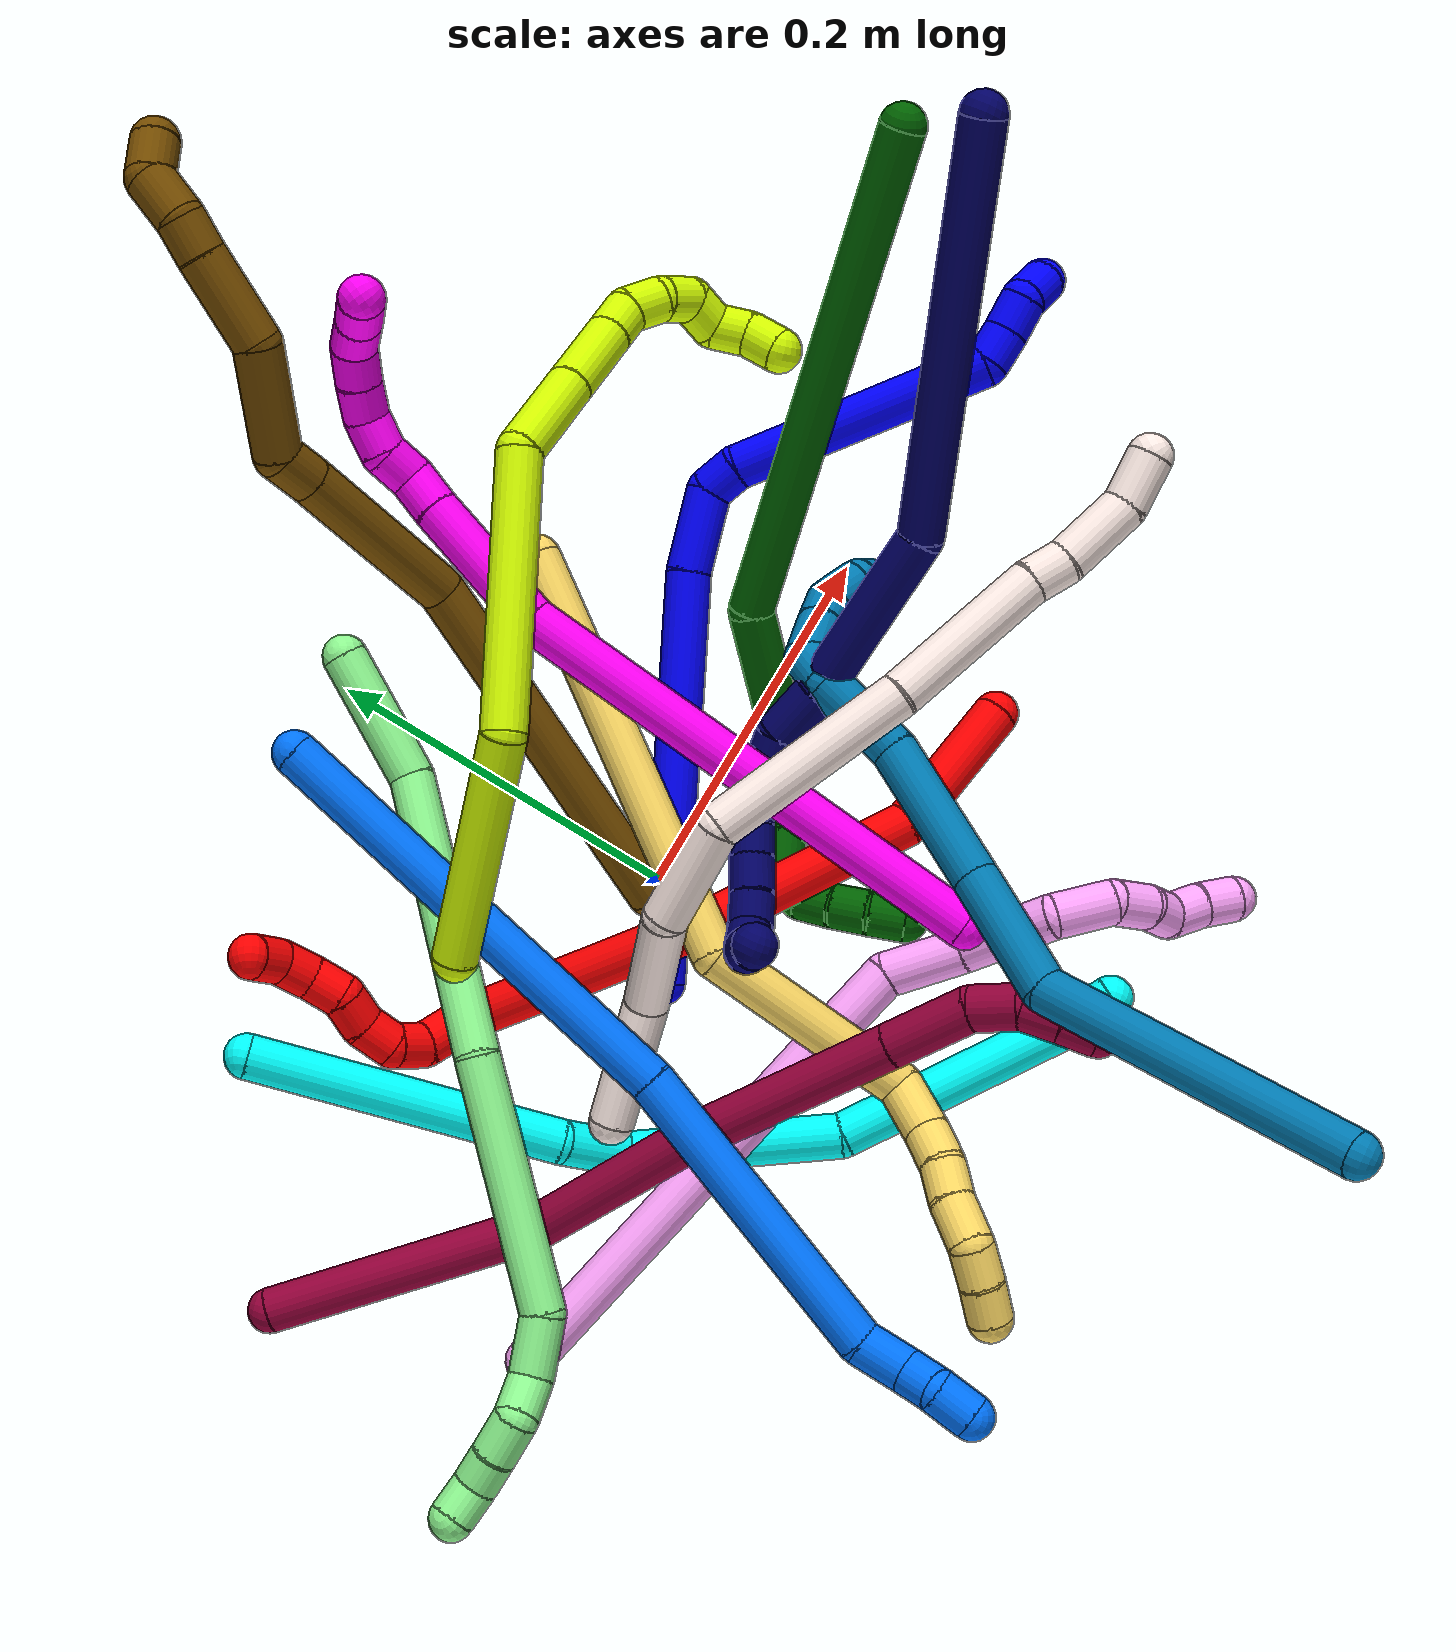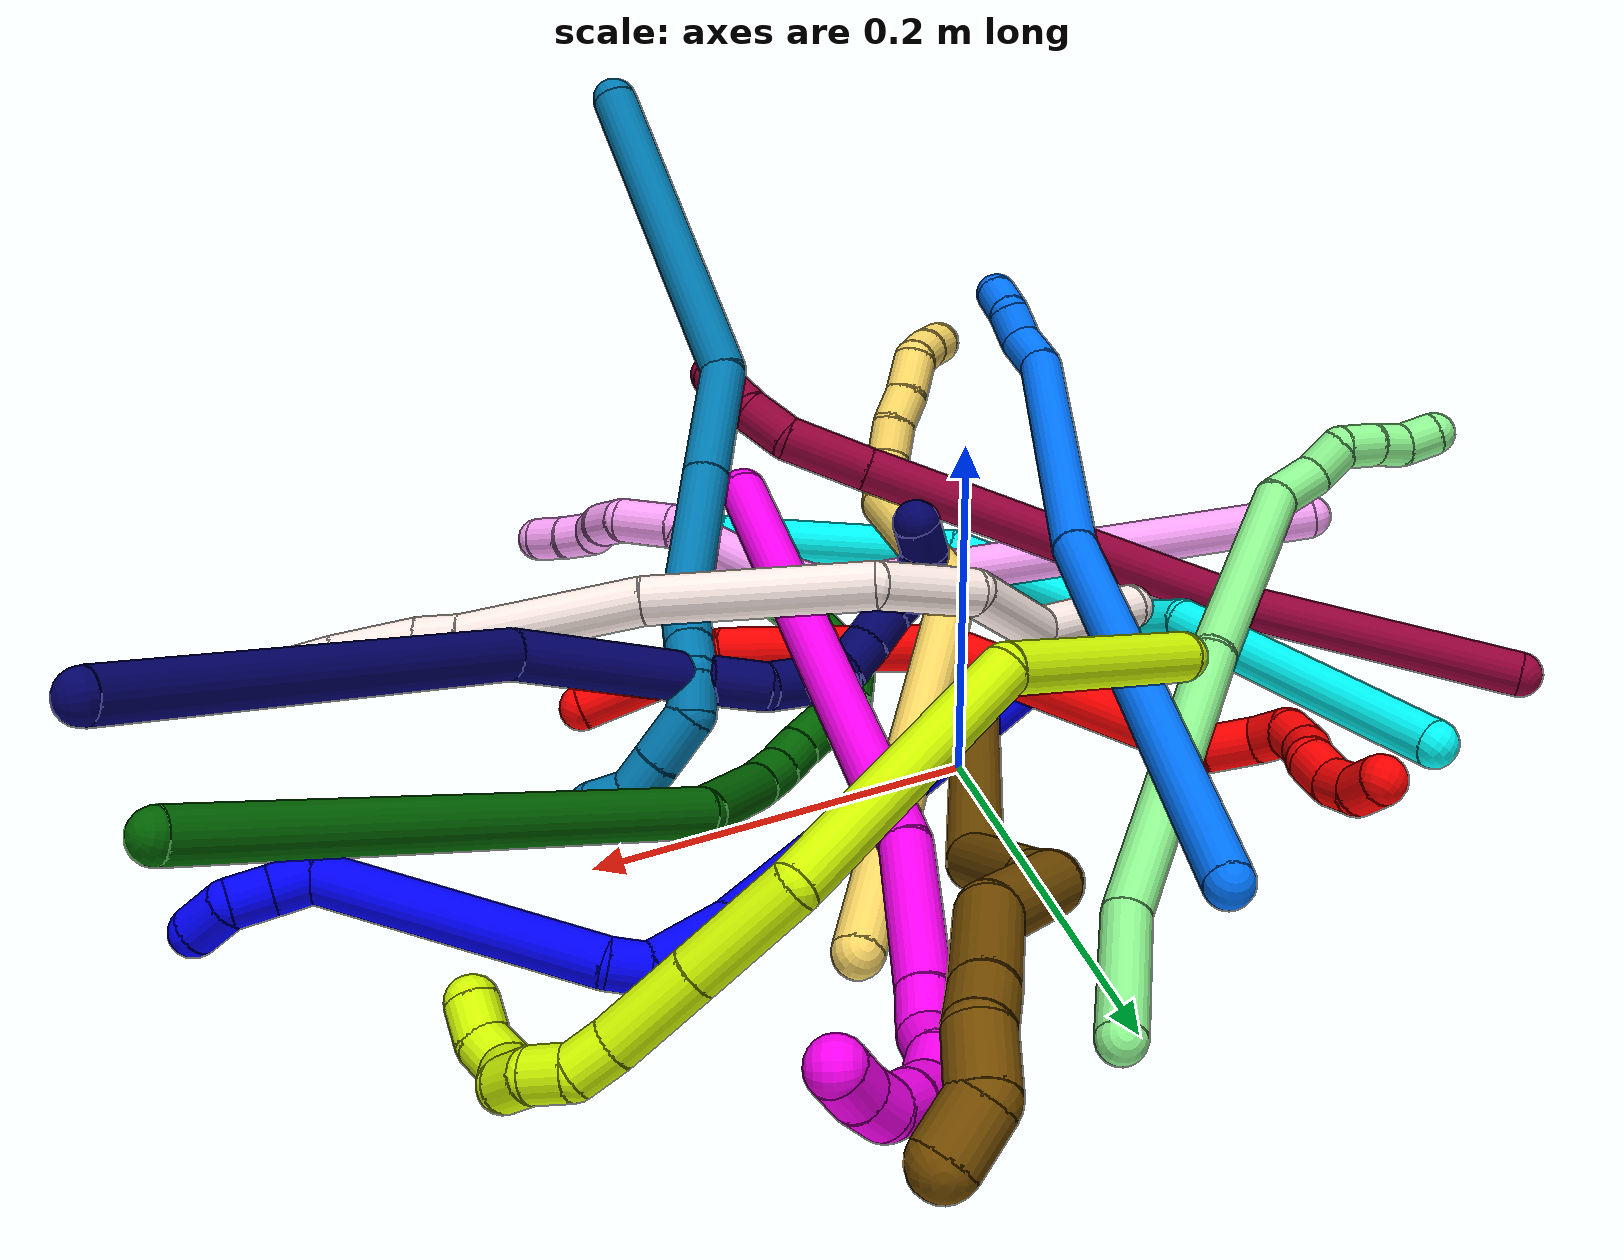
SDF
<sdf version="1.7">
 <world name="default">
  <plugin name="TubeGeneratorPlugin" filename="libtube_generator_plugin.so"/>
  <model name="photoneo_s_sensor">
   <static>1</static>
   <pose>0 0 2 1.57079 1.57079 3.14159</pose>
   <link name="link">
    <inertial><mass>0.1</mass></inertial>
    <sensor name="sensor" type="depth">
     <update_rate>30</update_rate>
     <camera>
      <horizontal_fov>1.22</horizontal_fov>
      <image><width>1920</width><height>1200</height><format>B8G8R8</format></image>
      <clip><near>0.1</near><far>4</far></clip>
      <depth_camera><output>points</output></depth_camera>
     </camera>
     <plugin name="camera_plugin" filename="libgazebo_ros_depth_camera.so">
      <baseline>0.2</baseline>
      <alwaysOn>1</alwaysOn>
      <updateRate>0.0</updateRate>
      <cameraName>camera_ir</cameraName>
      <imageTopicName>/camera/color/image_raw</imageTopicName>
      <cameraInfoTopicName>/camera/color/camera_info</cameraInfoTopicName>
      <depthImageTopicName>/camera/depth/image_raw</depthImageTopicName>
      <depthImageCameraInfoTopicName>/camera/depth/camera_info</depthImageCameraInfoTopicName>
      <pointCloudTopicName>/camera/depth/points</pointCloudTopicName>
      <frameName>fr_optical</frameName>
      <pointCloudCutoff>0.1</pointCloudCutoff>
      <pointCloudCutoffMax>2.0</pointCloudCutoffMax>
      <distortionK1>0</distortionK1>
      <distortionK2>0</distortionK2>
      <distortionK3>0</distortionK3>
      <distortionT1>0</distortionT1>
      <distortionT2>0</distortionT2>
      <CxPrime>0</CxPrime>
      <Cx>0</Cx>
      <Cy>0</Cy>
      <focalLength>0</focalLength>
      <hackBaseline>0</hackBaseline>
     </plugin>
    </sensor>
   </link>
  </model>
  <gravity>0 0 -9.8</gravity>
  <magnetic_field>6e-06 2.3e-05 -4.2e-05</magnetic_field>
  <atmosphere type="adiabatic"/>
  <physics name="default_physics" default="0" type="ode">
   <max_step_size>0.003</max_step_size>
   <real_time_factor>1</real_time_factor>
   <real_time_update_rate>1000</real_time_update_rate>
   <max_contacts>10000</max_contacts>
   <ode>
    <solver>
     <type>quick</type>
     <iters>100</iters>
     <sor>1.3</sor>
     <use_dynamic_moi_rescaling>0</use_dynamic_moi_rescaling>
    </solver>
    <constraints>
     <contact_max_correcting_vel>0</contact_max_correcting_vel>
     <contact_surface_layer>0.001</contact_surface_layer>
     <cfm>0</cfm>
     <erp>0.2</erp>
    </constraints>
   </ode>
  </physics>
  <scene><ambient>0.4 0.4 0.4 1</ambient><background>0.7 0.7 0.7 1</background><shadows>0</shadows></scene>
  <audio><device>default</device></audio>
  <spherical_coordinates>
   <surface_model>EARTH_WGS84</surface_model>
   <latitude_deg>0</latitude_deg>
   <longitude_deg>0</longitude_deg>
   <elevation>0</elevation>
   <heading_deg>0</heading_deg>
  </spherical_coordinates>
  <model name="bin">
   <static>1</static>
   <link name="bottom">
    <collision name="collision-bottom">
     <pose>0 0 -0.01 0 -0 0</pose>
     <geometry><box><size>0.8 0.6 0.02</size></box></geometry>
     <surface>
      <friction><ode><mu>100</mu><mu2>100</mu2></ode></friction>
      <contact><collide_bitmask>65535</collide_bitmask></contact>
     </surface>
    </collision>
   </link>
   <link name="west_wall">
    <collision name="collision-west_wall">
     <pose>-0.41 0 0.1 0 -0 0</pose>
     <geometry><box><size>0.02 0.6 0.2</size></box></geometry>
     <surface>
      <friction><ode><mu>100</mu><mu2>100</mu2></ode></friction>
      <contact><collide_bitmask>65535</collide_bitmask></contact>
     </surface>
    </collision>
   </link>
   <link name="east_wall">
    <collision name="collision-east_wall">
     <pose>0.41 0 0.1 0 -0 0</pose>
     <geometry><box><size>0.02 0.6 0.2</size></box></geometry>
     <surface>
      <friction><ode><mu>100</mu><mu2>100</mu2></ode></friction>
      <contact><collide_bitmask>65535</collide_bitmask></contact>
     </surface>
    </collision>
   </link>
   <link name="south_wall">
    <collision name="collision-south_wall">
     <pose>0 -0.31 0.1 0 -0 0</pose>
     <geometry><box><size>0.8 0.02 0.2</size></box></geometry>
     <surface>
      <friction><ode><mu>100</mu><mu2>100</mu2></ode></friction>
      <contact><collide_bitmask>65535</collide_bitmask></contact>
     </surface>
    </collision>
   </link>
   <link name="north_wall">
    <collision name="collision-north_wall">
     <pose>0 0.31 0.1 0 -0 0</pose>
     <geometry><box><size>0.8 0.02 0.2</size></box></geometry>
     <surface>
      <friction><ode><mu>100</mu><mu2>100</mu2></ode></friction>
      <contact><collide_bitmask>65535</collide_bitmask></contact>
     </surface>
    </collision>
   </link>
  </model>
  <model name="1">
   <static>0</static>
   <link name="1">
    <collision name="collision-cylinder-e_1_1_4">
     <pose>0.038189 0.042399 0.097112 -0.411655 0.345906 -0.072916</pose>
     <geometry><cylinder><radius>0.0125</radius><length>0.225271</length></cylinder></geometry>
     <surface>
      <friction><ode><mu>1.16</mu><mu2>1.16</mu2><slip1>0</slip1><slip2>0</slip2></ode></friction>
      <contact><ode><kp>1e+06</kp><kd>1</kd><max_vel>0</max_vel><min_depth>0.001</min_depth></ode></contact>
     </surface>
    </collision>
    <visual name="visual-cylinder-e_1_1_4">
     <pose>0.038189 0.042399 0.097112 -0.411655 0.345906 -0.072916</pose>
     <geometry><cylinder><radius>0.0125</radius><length>0.225271</length></cylinder></geometry>
     <material><ambient>0 0 1 1</ambient></material>
    </visual>
    <collision name="collision-cylinder-e_2_4_5">
     <pose>0.087279 0.090617 0.213697 -0.290366 0.492292 -0.073436</pose>
     <geometry><cylinder><radius>0.0125</radius><length>0.046127</length></cylinder></geometry>
     <surface>
      <friction><ode><mu>1.16</mu><mu2>1.16</mu2><slip1>0</slip1><slip2>0</slip2></ode></friction>
      <contact><ode><kp>1e+06</kp><kd>1</kd><max_vel>0</max_vel><min_depth>0.001</min_depth></ode></contact>
     </surface>
    </collision>
    <visual name="visual-cylinder-e_2_4_5">
     <pose>0.087279 0.090617 0.213697 -0.290366 0.492292 -0.073436</pose>
     <geometry><cylinder><radius>0.0125</radius><length>0.046127</length></cylinder></geometry>
     <material><ambient>0 0 1 1</ambient></material>
    </visual>
    <collision name="collision-cylinder-e_3_5_6">
     <pose>0.105049 0.092913 0.239587 0.502256 0.753683 0.202363</pose>
     <geometry><cylinder><radius>0.0125</radius><length>0.020075</length></cylinder></geometry>
     <surface>
      <friction><ode><mu>1.16</mu><mu2>1.16</mu2><slip1>0</slip1><slip2>0</slip2></ode></friction>
      <contact><ode><kp>1e+06</kp><kd>1</kd><max_vel>0</max_vel><min_depth>0.001</min_depth></ode></contact>
     </surface>
    </collision>
    <visual name="visual-cylinder-e_3_5_6">
     <pose>0.105049 0.092913 0.239587 0.502256 0.753683 0.202363</pose>
     <geometry><cylinder><radius>0.0125</radius><length>0.020075</length></cylinder></geometry>
     <material><ambient>0 0 1 1</ambient></material>
    </visual>
    <collision name="collision-cylinder-e_4_6_7">
     <pose>0.170016 0.055069 0.27381 0.889825 0.920734 0.464363</pose>
     <geometry><cylinder><radius>0.0125</radius><length>0.145967</length></cylinder></geometry>
     <surface>
      <friction><ode><mu>1.16</mu><mu2>1.16</mu2><slip1>0</slip1><slip2>0</slip2></ode></friction>
      <contact><ode><kp>1e+06</kp><kd>1</kd><max_vel>0</max_vel><min_depth>0.001</min_depth></ode></contact>
     </surface>
    </collision>
    <visual name="visual-cylinder-e_4_6_7">
     <pose>0.170016 0.055069 0.27381 0.889825 0.920734 0.464363</pose>
     <geometry><cylinder><radius>0.0125</radius><length>0.145967</length></cylinder></geometry>
     <material><ambient>0 0 1 1</ambient></material>
    </visual>
    <collision name="collision-cylinder-e_5_7_8">
     <pose>0.235309 0.021828 0.308616 -0.153044 0.79346 -0.06422</pose>
     <geometry><cylinder><radius>0.0125</radius><length>0.020189</length></cylinder></geometry>
     <surface>
      <friction><ode><mu>1.16</mu><mu2>1.16</mu2><slip1>0</slip1><slip2>0</slip2></ode></friction>
      <contact><ode><kp>1e+06</kp><kd>1</kd><max_vel>0</max_vel><min_depth>0.001</min_depth></ode></contact>
     </surface>
    </collision>
    <visual name="visual-cylinder-e_5_7_8">
     <pose>0.235309 0.021828 0.308616 -0.153044 0.79346 -0.06422</pose>
     <geometry><cylinder><radius>0.0125</radius><length>0.020189</length></cylinder></geometry>
     <material><ambient>0 0 1 1</ambient></material>
    </visual>
    <collision name="collision-cylinder-e_6_8_9">
     <pose>0.249048 0.023933 0.323231 -0.133816 0.705291 -0.049312</pose>
     <geometry><cylinder><radius>0.0125</radius><length>0.020188</length></cylinder></geometry>
     <surface>
      <friction><ode><mu>1.16</mu><mu2>1.16</mu2><slip1>0</slip1><slip2>0</slip2></ode></friction>
      <contact><ode><kp>1e+06</kp><kd>1</kd><max_vel>0</max_vel><min_depth>0.001</min_depth></ode></contact>
     </surface>
    </collision>
    <visual name="visual-cylinder-e_6_8_9">
     <pose>0.249048 0.023933 0.323231 -0.133816 0.705291 -0.049312</pose>
     <geometry><cylinder><radius>0.0125</radius><length>0.020188</length></cylinder></geometry>
     <material><ambient>0 0 1 1</ambient></material>
    </visual>
    <collision name="collision-cylinder-e_7_9_2">
     <pose>0.265675 0.029169 0.332751 -1.14625 1.14113 -0.785351</pose>
     <geometry><cylinder><radius>0.0125</radius><length>0.022182</length></cylinder></geometry>
     <surface>
      <friction><ode><mu>1.16</mu><mu2>1.16</mu2><slip1>0</slip1><slip2>0</slip2></ode></friction>
      <contact><ode><kp>1e+06</kp><kd>1</kd><max_vel>0</max_vel><min_depth>0.001</min_depth></ode></contact>
     </surface>
    </collision>
    <visual name="visual-cylinder-e_7_9_2">
     <pose>0.265675 0.029169 0.332751 -1.14625 1.14113 -0.785351</pose>
     <geometry><cylinder><radius>0.0125</radius><length>0.022182</length></cylinder></geometry>
     <material><ambient>0 0 1 1</ambient></material>
    </visual>
    <collision name="collision-sphere-2">
     <pose>0.275758 0.033379 0.334654 0 -0 0</pose>
     <geometry><sphere><radius>0.0125</radius></sphere></geometry>
     <surface>
      <friction><ode><mu>1.16</mu><mu2>1.16</mu2><slip1>0</slip1><slip2>0</slip2></ode></friction>
      <contact><ode><kp>1e+06</kp><kd>1</kd><max_vel>0</max_vel><min_depth>0.001</min_depth></ode></contact>
     </surface>
    </collision>
    <visual name="visual-sphere-2">
     <pose>0.275758 0.033379 0.334654 0 -0 0</pose>
     <geometry><sphere><radius>0.0125</radius></sphere></geometry>
     <material><ambient>0 0 1 1</ambient></material>
    </visual>
    <collision name="collision-sphere-9">
     <pose>0.255592 0.024959 0.330848 0 -0 0</pose>
     <geometry><sphere><radius>0.0125</radius></sphere></geometry>
     <surface>
      <friction><ode><mu>1.16</mu><mu2>1.16</mu2><slip1>0</slip1><slip2>0</slip2></ode></friction>
      <contact><ode><kp>1e+06</kp><kd>1</kd><max_vel>0</max_vel><min_depth>0.001</min_depth></ode></contact>
     </surface>
    </collision>
    <visual name="visual-sphere-9">
     <pose>0.255592 0.024959 0.330848 0 -0 0</pose>
     <geometry><sphere><radius>0.0125</radius></sphere></geometry>
     <material><ambient>0 0 1 1</ambient></material>
    </visual>
    <collision name="collision-sphere-4">
     <pose>0.076378 0.084798 0.194223 0 -0 0</pose>
     <geometry><sphere><radius>0.0125</radius></sphere></geometry>
     <surface>
      <friction><ode><mu>1.16</mu><mu2>1.16</mu2><slip1>0</slip1><slip2>0</slip2></ode></friction>
      <contact><ode><kp>1e+06</kp><kd>1</kd><max_vel>0</max_vel><min_depth>0.001</min_depth></ode></contact>
     </surface>
    </collision>
    <visual name="visual-sphere-4">
     <pose>0.076378 0.084798 0.194223 0 -0 0</pose>
     <geometry><sphere><radius>0.0125</radius></sphere></geometry>
     <material><ambient>0 0 1 1</ambient></material>
    </visual>
    <collision name="collision-sphere-1">
     <geometry><sphere><radius>0.0125</radius></sphere></geometry>
     <surface>
      <friction><ode><mu>1.16</mu><mu2>1.16</mu2><slip1>0</slip1><slip2>0</slip2></ode></friction>
      <contact><ode><kp>1e+06</kp><kd>1</kd><max_vel>0</max_vel><min_depth>0.001</min_depth></ode></contact>
     </surface>
    </collision>
    <visual name="visual-sphere-1">
     <geometry><sphere><radius>0.0125</radius></sphere></geometry>
     <material><ambient>0 0 1 1</ambient></material>
    </visual>
    <collision name="collision-sphere-8">
     <pose>0.242505 0.022908 0.315614 0 -0 0</pose>
     <geometry><sphere><radius>0.0125</radius></sphere></geometry>
     <surface>
      <friction><ode><mu>1.16</mu><mu2>1.16</mu2><slip1>0</slip1><slip2>0</slip2></ode></friction>
      <contact><ode><kp>1e+06</kp><kd>1</kd><max_vel>0</max_vel><min_depth>0.001</min_depth></ode></contact>
     </surface>
    </collision>
    <visual name="visual-sphere-8">
     <pose>0.242505 0.022908 0.315614 0 -0 0</pose>
     <geometry><sphere><radius>0.0125</radius></sphere></geometry>
     <material><ambient>0 0 1 1</ambient></material>
    </visual>
    <collision name="collision-sphere-5">
     <pose>0.09818 0.096436 0.233171 0 -0 0</pose>
     <geometry><sphere><radius>0.0125</radius></sphere></geometry>
     <surface>
      <friction><ode><mu>1.16</mu><mu2>1.16</mu2><slip1>0</slip1><slip2>0</slip2></ode></friction>
      <contact><ode><kp>1e+06</kp><kd>1</kd><max_vel>0</max_vel><min_depth>0.001</min_depth></ode></contact>
     </surface>
    </collision>
    <visual name="visual-sphere-5">
     <pose>0.09818 0.096436 0.233171 0 -0 0</pose>
     <geometry><sphere><radius>0.0125</radius></sphere></geometry>
     <material><ambient>0 0 1 1</ambient></material>
    </visual>
    <collision name="collision-sphere-6">
     <pose>0.111918 0.089389 0.246002 0 -0 0</pose>
     <geometry><sphere><radius>0.0125</radius></sphere></geometry>
     <surface>
      <friction><ode><mu>1.16</mu><mu2>1.16</mu2><slip1>0</slip1><slip2>0</slip2></ode></friction>
      <contact><ode><kp>1e+06</kp><kd>1</kd><max_vel>0</max_vel><min_depth>0.001</min_depth></ode></contact>
     </surface>
    </collision>
    <visual name="visual-sphere-6">
     <pose>0.111918 0.089389 0.246002 0 -0 0</pose>
     <geometry><sphere><radius>0.0125</radius></sphere></geometry>
     <material><ambient>0 0 1 1</ambient></material>
    </visual>
    <collision name="collision-sphere-7">
     <pose>0.228114 0.020749 0.301619 0 -0 0</pose>
     <geometry><sphere><radius>0.0125</radius></sphere></geometry>
     <surface>
      <friction><ode><mu>1.16</mu><mu2>1.16</mu2><slip1>0</slip1><slip2>0</slip2></ode></friction>
      <contact><ode><kp>1e+06</kp><kd>1</kd><max_vel>0</max_vel><min_depth>0.001</min_depth></ode></contact>
     </surface>
    </collision>
    <visual name="visual-sphere-7">
     <pose>0.228114 0.020749 0.301619 0 -0 0</pose>
     <geometry><sphere><radius>0.0125</radius></sphere></geometry>
     <material><ambient>0 0 1 1</ambient></material>
    </visual>
    <inertial>
     <pose>0.110453 0.050411 0.193296 0 -0 0</pose>
     <mass>0.5</mass>
     <inertia>
      <ixx>0.001084</ixx>
      <ixy>0</ixy>
      <ixz>0</ixz>
      <iyy>0.001134</iyy>
      <iyz>0</iyz>
      <izz>-0.00076</izz>
     </inertia>
    </inertial>
   </link>
   <pose>-0.04735 -0.031825 0.011499 -0.9556 0.511173 -0.688922</pose>
  </model>
  <model name="2">
   <static>0</static>
   <link name="2">
    <collision name="collision-cylinder-e_1_1_4">
     <pose>-0.015344 0.022057 0.030603 -0.624516 -0.386319 0.126118</pose>
     <geometry><cylinder><radius>0.0125</radius><length>0.08145</length></cylinder></geometry>
     <surface>
      <friction><ode><mu>1.16</mu><mu2>1.16</mu2><slip1>0</slip1><slip2>0</slip2></ode></friction>
      <contact><ode><kp>1e+06</kp><kd>1</kd><max_vel>0</max_vel><min_depth>0.001</min_depth></ode></contact>
     </surface>
    </collision>
    <visual name="visual-cylinder-e_1_1_4">
     <pose>-0.015344 0.022057 0.030603 -0.624516 -0.386319 0.126118</pose>
     <geometry><cylinder><radius>0.0125</radius><length>0.08145</length></cylinder></geometry>
     <material><ambient>1 0 0 1</ambient></material>
    </visual>
    <collision name="collision-cylinder-e_2_4_5">
     <pose>-0.060681 0.090892 0.085819 -1.08644 -0.516109 0.316084</pose>
     <geometry><cylinder><radius>0.0125</radius><length>0.121547</length></cylinder></geometry>
     <surface>
      <friction><ode><mu>1.16</mu><mu2>1.16</mu2><slip1>0</slip1><slip2>0</slip2></ode></friction>
      <contact><ode><kp>1e+06</kp><kd>1</kd><max_vel>0</max_vel><min_depth>0.001</min_depth></ode></contact>
     </surface>
    </collision>
    <visual name="visual-cylinder-e_2_4_5">
     <pose>-0.060681 0.090892 0.085819 -1.08644 -0.516109 0.316084</pose>
     <geometry><cylinder><radius>0.0125</radius><length>0.121547</length></cylinder></geometry>
     <material><ambient>1 0 0 1</ambient></material>
    </visual>
    <collision name="collision-cylinder-e_3_5_6">
     <pose>-0.148945 0.181978 0.120838 -1.3401 -0.907715 0.73766</pose>
     <geometry><cylinder><radius>0.0125</radius><length>0.147881</length></cylinder></geometry>
     <surface>
      <friction><ode><mu>1.16</mu><mu2>1.16</mu2><slip1>0</slip1><slip2>0</slip2></ode></friction>
      <contact><ode><kp>1e+06</kp><kd>1</kd><max_vel>0</max_vel><min_depth>0.001</min_depth></ode></contact>
     </surface>
    </collision>
    <visual name="visual-cylinder-e_3_5_6">
     <pose>-0.148945 0.181978 0.120838 -1.3401 -0.907715 0.73766</pose>
     <geometry><cylinder><radius>0.0125</radius><length>0.147881</length></cylinder></geometry>
     <material><ambient>1 0 0 1</ambient></material>
    </visual>
    <collision name="collision-cylinder-e_4_6_7">
     <pose>-0.212338 0.236897 0.138672 -0.960114 -0.376516 0.197748</pose>
     <geometry><cylinder><radius>0.0125</radius><length>0.027855</length></cylinder></geometry>
     <surface>
      <friction><ode><mu>1.16</mu><mu2>1.16</mu2><slip1>0</slip1><slip2>0</slip2></ode></friction>
      <contact><ode><kp>1e+06</kp><kd>1</kd><max_vel>0</max_vel><min_depth>0.001</min_depth></ode></contact>
     </surface>
    </collision>
    <visual name="visual-cylinder-e_4_6_7">
     <pose>-0.212338 0.236897 0.138672 -0.960114 -0.376516 0.197748</pose>
     <geometry><cylinder><radius>0.0125</radius><length>0.027855</length></cylinder></geometry>
     <material><ambient>1 0 0 1</ambient></material>
    </visual>
    <collision name="collision-cylinder-e_5_7_8">
     <pose>-0.215801 0.257533 0.148574 -1.32875 0.159224 -0.124796</pose>
     <geometry><cylinder><radius>0.0125</radius><length>0.020917</length></cylinder></geometry>
     <surface>
      <friction><ode><mu>1.16</mu><mu2>1.16</mu2><slip1>0</slip1><slip2>0</slip2></ode></friction>
      <contact><ode><kp>1e+06</kp><kd>1</kd><max_vel>0</max_vel><min_depth>0.001</min_depth></ode></contact>
     </surface>
    </collision>
    <visual name="visual-cylinder-e_5_7_8">
     <pose>-0.215801 0.257533 0.148574 -1.32875 0.159224 -0.124796</pose>
     <geometry><cylinder><radius>0.0125</radius><length>0.020917</length></cylinder></geometry>
     <material><ambient>1 0 0 1</ambient></material>
    </visual>
    <collision name="collision-cylinder-e_6_8_9">
     <pose>-0.213558 0.27657 0.146514 -2.03696 0.057851 -0.093825</pose>
     <geometry><cylinder><radius>0.0125</radius><length>0.020212</length></cylinder></geometry>
     <surface>
      <friction><ode><mu>1.16</mu><mu2>1.16</mu2><slip1>0</slip1><slip2>0</slip2></ode></friction>
      <contact><ode><kp>1e+06</kp><kd>1</kd><max_vel>0</max_vel><min_depth>0.001</min_depth></ode></contact>
     </surface>
    </collision>
    <visual name="visual-cylinder-e_6_8_9">
     <pose>-0.213558 0.27657 0.146514 -2.03696 0.057851 -0.093825</pose>
     <geometry><cylinder><radius>0.0125</radius><length>0.020212</length></cylinder></geometry>
     <material><ambient>1 0 0 1</ambient></material>
    </visual>
    <collision name="collision-cylinder-e_7_9_10">
     <pose>-0.208792 0.292844 0.136475 -2.21943 0.430245 -0.828716</pose>
     <geometry><cylinder><radius>0.0125</radius><length>0.020053</length></cylinder></geometry>
     <surface>
      <friction><ode><mu>1.16</mu><mu2>1.16</mu2><slip1>0</slip1><slip2>0</slip2></ode></friction>
      <contact><ode><kp>1e+06</kp><kd>1</kd><max_vel>0</max_vel><min_depth>0.001</min_depth></ode></contact>
     </surface>
    </collision>
    <visual name="visual-cylinder-e_7_9_10">
     <pose>-0.208792 0.292844 0.136475 -2.21943 0.430245 -0.828716</pose>
     <geometry><cylinder><radius>0.0125</radius><length>0.020053</length></cylinder></geometry>
     <material><ambient>1 0 0 1</ambient></material>
    </visual>
    <collision name="collision-cylinder-e_8_10_11">
     <pose>-0.205758 0.308909 0.126296 -2.05892 -0.114691 0.190386</pose>
     <geometry><cylinder><radius>0.0125</radius><length>0.020066</length></cylinder></geometry>
     <surface>
      <friction><ode><mu>1.16</mu><mu2>1.16</mu2><slip1>0</slip1><slip2>0</slip2></ode></friction>
      <contact><ode><kp>1e+06</kp><kd>1</kd><max_vel>0</max_vel><min_depth>0.001</min_depth></ode></contact>
     </surface>
    </collision>
    <visual name="visual-cylinder-e_8_10_11">
     <pose>-0.205758 0.308909 0.126296 -2.05892 -0.114691 0.190386</pose>
     <geometry><cylinder><radius>0.0125</radius><length>0.020066</length></cylinder></geometry>
     <material><ambient>1 0 0 1</ambient></material>
    </visual>
    <collision name="collision-cylinder-e_9_11_12">
     <pose>-0.205438 0.327322 0.119247 -1.813 0.147236 -0.187825</pose>
     <geometry><cylinder><radius>0.0125</radius><length>0.020013</length></cylinder></geometry>
     <surface>
      <friction><ode><mu>1.16</mu><mu2>1.16</mu2><slip1>0</slip1><slip2>0</slip2></ode></friction>
      <contact><ode><kp>1e+06</kp><kd>1</kd><max_vel>0</max_vel><min_depth>0.001</min_depth></ode></contact>
     </surface>
    </collision>
    <visual name="visual-cylinder-e_9_11_12">
     <pose>-0.205438 0.327322 0.119247 -1.813 0.147236 -0.187825</pose>
     <geometry><cylinder><radius>0.0125</radius><length>0.020013</length></cylinder></geometry>
     <material><ambient>1 0 0 1</ambient></material>
    </visual>
    <collision name="collision-cylinder-e_10_12_2">
     <pose>-0.200167 0.346009 0.118666 -1.37587 0.389971 -0.321823</pose>
     <geometry><cylinder><radius>0.0125</radius><length>0.020007</length></cylinder></geometry>
     <surface>
      <friction><ode><mu>1.16</mu><mu2>1.16</mu2><slip1>0</slip1><slip2>0</slip2></ode></friction>
      <contact><ode><kp>1e+06</kp><kd>1</kd><max_vel>0</max_vel><min_depth>0.001</min_depth></ode></contact>
     </surface>
    </collision>
    <visual name="visual-cylinder-e_10_12_2">
     <pose>-0.200167 0.346009 0.118666 -1.37587 0.389971 -0.321823</pose>
     <geometry><cylinder><radius>0.0125</radius><length>0.020007</length></cylinder></geometry>
     <material><ambient>1 0 0 1</ambient></material>
    </visual>
    <collision name="collision-sphere-2">
     <pose>-0.196364 0.355086 0.120458 0 -0 0</pose>
     <geometry><sphere><radius>0.0125</radius></sphere></geometry>
     <surface>
      <friction><ode><mu>1.16</mu><mu2>1.16</mu2><slip1>0</slip1><slip2>0</slip2></ode></friction>
      <contact><ode><kp>1e+06</kp><kd>1</kd><max_vel>0</max_vel><min_depth>0.001</min_depth></ode></contact>
     </surface>
    </collision>
    <visual name="visual-sphere-2">
     <pose>-0.196364 0.355086 0.120458 0 -0 0</pose>
     <geometry><sphere><radius>0.0125</radius></sphere></geometry>
     <material><ambient>1 0 0 1</ambient></material>
    </visual>
    <collision name="collision-sphere-12">
     <pose>-0.20397 0.336932 0.116873 0 -0 0</pose>
     <geometry><sphere><radius>0.0125</radius></sphere></geometry>
     <surface>
      <friction><ode><mu>1.16</mu><mu2>1.16</mu2><slip1>0</slip1><slip2>0</slip2></ode></friction>
      <contact><ode><kp>1e+06</kp><kd>1</kd><max_vel>0</max_vel><min_depth>0.001</min_depth></ode></contact>
     </surface>
    </collision>
    <visual name="visual-sphere-12">
     <pose>-0.20397 0.336932 0.116873 0 -0 0</pose>
     <geometry><sphere><radius>0.0125</radius></sphere></geometry>
     <material><ambient>1 0 0 1</ambient></material>
    </visual>
    <collision name="collision-sphere-11">
     <pose>-0.206906 0.317713 0.121622 0 -0 0</pose>
     <geometry><sphere><radius>0.0125</radius></sphere></geometry>
     <surface>
      <friction><ode><mu>1.16</mu><mu2>1.16</mu2><slip1>0</slip1><slip2>0</slip2></ode></friction>
      <contact><ode><kp>1e+06</kp><kd>1</kd><max_vel>0</max_vel><min_depth>0.001</min_depth></ode></contact>
     </surface>
    </collision>
    <visual name="visual-sphere-11">
     <pose>-0.206906 0.317713 0.121622 0 -0 0</pose>
     <geometry><sphere><radius>0.0125</radius></sphere></geometry>
     <material><ambient>1 0 0 1</ambient></material>
    </visual>
    <collision name="collision-sphere-10">
     <pose>-0.20461 0.300106 0.13097 0 -0 0</pose>
     <geometry><sphere><radius>0.0125</radius></sphere></geometry>
     <surface>
      <friction><ode><mu>1.16</mu><mu2>1.16</mu2><slip1>0</slip1><slip2>0</slip2></ode></friction>
      <contact><ode><kp>1e+06</kp><kd>1</kd><max_vel>0</max_vel><min_depth>0.001</min_depth></ode></contact>
     </surface>
    </collision>
    <visual name="visual-sphere-10">
     <pose>-0.20461 0.300106 0.13097 0 -0 0</pose>
     <geometry><sphere><radius>0.0125</radius></sphere></geometry>
     <material><ambient>1 0 0 1</ambient></material>
    </visual>
    <collision name="collision-sphere-9">
     <pose>-0.212974 0.285582 0.14198 0 -0 0</pose>
     <geometry><sphere><radius>0.0125</radius></sphere></geometry>
     <surface>
      <friction><ode><mu>1.16</mu><mu2>1.16</mu2><slip1>0</slip1><slip2>0</slip2></ode></friction>
      <contact><ode><kp>1e+06</kp><kd>1</kd><max_vel>0</max_vel><min_depth>0.001</min_depth></ode></contact>
     </surface>
    </collision>
    <visual name="visual-sphere-9">
     <pose>-0.212974 0.285582 0.14198 0 -0 0</pose>
     <geometry><sphere><radius>0.0125</radius></sphere></geometry>
     <material><ambient>1 0 0 1</ambient></material>
    </visual>
    <collision name="collision-sphere-4">
     <pose>-0.030689 0.044114 0.061206 0 -0 0</pose>
     <geometry><sphere><radius>0.0125</radius></sphere></geometry>
     <surface>
      <friction><ode><mu>1.16</mu><mu2>1.16</mu2><slip1>0</slip1><slip2>0</slip2></ode></friction>
      <contact><ode><kp>1e+06</kp><kd>1</kd><max_vel>0</max_vel><min_depth>0.001</min_depth></ode></contact>
     </surface>
    </collision>
    <visual name="visual-sphere-4">
     <pose>-0.030689 0.044114 0.061206 0 -0 0</pose>
     <geometry><sphere><radius>0.0125</radius></sphere></geometry>
     <material><ambient>1 0 0 1</ambient></material>
    </visual>
    <collision name="collision-sphere-1">
     <geometry><sphere><radius>0.0125</radius></sphere></geometry>
     <surface>
      <friction><ode><mu>1.16</mu><mu2>1.16</mu2><slip1>0</slip1><slip2>0</slip2></ode></friction>
      <contact><ode><kp>1e+06</kp><kd>1</kd><max_vel>0</max_vel><min_depth>0.001</min_depth></ode></contact>
     </surface>
    </collision>
    <visual name="visual-sphere-1">
     <geometry><sphere><radius>0.0125</radius></sphere></geometry>
     <material><ambient>1 0 0 1</ambient></material>
    </visual>
    <collision name="collision-sphere-8">
     <pose>-0.214142 0.267558 0.151049 0 -0 0</pose>
     <geometry><sphere><radius>0.0125</radius></sphere></geometry>
     <surface>
      <friction><ode><mu>1.16</mu><mu2>1.16</mu2><slip1>0</slip1><slip2>0</slip2></ode></friction>
      <contact><ode><kp>1e+06</kp><kd>1</kd><max_vel>0</max_vel><min_depth>0.001</min_depth></ode></contact>
     </surface>
    </collision>
    <visual name="visual-sphere-8">
     <pose>-0.214142 0.267558 0.151049 0 -0 0</pose>
     <geometry><sphere><radius>0.0125</radius></sphere></geometry>
     <material><ambient>1 0 0 1</ambient></material>
    </visual>
    <collision name="collision-sphere-5">
     <pose>-0.090672 0.13767 0.110431 0 -0 0</pose>
     <geometry><sphere><radius>0.0125</radius></sphere></geometry>
     <surface>
      <friction><ode><mu>1.16</mu><mu2>1.16</mu2><slip1>0</slip1><slip2>0</slip2></ode></friction>
      <contact><ode><kp>1e+06</kp><kd>1</kd><max_vel>0</max_vel><min_depth>0.001</min_depth></ode></contact>
     </surface>
    </collision>
    <visual name="visual-sphere-5">
     <pose>-0.090672 0.13767 0.110431 0 -0 0</pose>
     <geometry><sphere><radius>0.0125</radius></sphere></geometry>
     <material><ambient>1 0 0 1</ambient></material>
    </visual>
    <collision name="collision-sphere-6">
     <pose>-0.207217 0.226286 0.131245 0 -0 0</pose>
     <geometry><sphere><radius>0.0125</radius></sphere></geometry>
     <surface>
      <friction><ode><mu>1.16</mu><mu2>1.16</mu2><slip1>0</slip1><slip2>0</slip2></ode></friction>
      <contact><ode><kp>1e+06</kp><kd>1</kd><max_vel>0</max_vel><min_depth>0.001</min_depth></ode></contact>
     </surface>
    </collision>
    <visual name="visual-sphere-6">
     <pose>-0.207217 0.226286 0.131245 0 -0 0</pose>
     <geometry><sphere><radius>0.0125</radius></sphere></geometry>
     <material><ambient>1 0 0 1</ambient></material>
    </visual>
    <collision name="collision-sphere-7">
     <pose>-0.217459 0.247508 0.146099 0 -0 0</pose>
     <geometry><sphere><radius>0.0125</radius></sphere></geometry>
     <surface>
      <friction><ode><mu>1.16</mu><mu2>1.16</mu2><slip1>0</slip1><slip2>0</slip2></ode></friction>
      <contact><ode><kp>1e+06</kp><kd>1</kd><max_vel>0</max_vel><min_depth>0.001</min_depth></ode></contact>
     </surface>
    </collision>
    <visual name="visual-sphere-7">
     <pose>-0.217459 0.247508 0.146099 0 -0 0</pose>
     <geometry><sphere><radius>0.0125</radius></sphere></geometry>
     <material><ambient>1 0 0 1</ambient></material>
    </visual>
    <inertial>
     <pose>-0.123656 0.16575 0.101513 0 -0 0</pose>
     <mass>0.5</mass>
     <inertia><ixx>0.000453</ixx><ixy>0</ixy><ixz>0</ixz><iyy>0.000507</iyy><iyz>0</iyz><izz>0</izz></inertia>
    </inertial>
   </link>
   <pose>0.173168 -0.111286 0.011954 0.772658 -0.882716 -0.289664</pose>
  </model>
  <model name="3">
   <static>0</static>
   <link name="3">
    <collision name="collision-cylinder-e_1_1_4">
     <pose>0.055954 -0.066906 0.006446 1.47476 0.694218 0.634933</pose>
     <geometry><cylinder><radius>0.0125</radius><length>0.174916</length></cylinder></geometry>
     <surface>
      <friction><ode><mu>1.16</mu><mu2>1.16</mu2><slip1>0</slip1><slip2>0</slip2></ode></friction>
      <contact><ode><kp>1e+06</kp><kd>1</kd><max_vel>0</max_vel><min_depth>0.001</min_depth></ode></contact>
     </surface>
    </collision>
    <visual name="visual-cylinder-e_1_1_4">
     <pose>0.055954 -0.066906 0.006446 1.47476 0.694218 0.634933</pose>
     <geometry><cylinder><radius>0.0125</radius><length>0.174916</length></cylinder></geometry>
     <material><ambient>0.003922 1 0.996078 1</ambient></material>
    </visual>
    <collision name="collision-cylinder-e_2_4_5">
     <pose>0.128497 -0.144447 0.019361 1.02422 0.927044 0.547827</pose>
     <geometry><cylinder><radius>0.0125</radius><length>0.041479</length></cylinder></geometry>
     <surface>
      <friction><ode><mu>1.16</mu><mu2>1.16</mu2><slip1>0</slip1><slip2>0</slip2></ode></friction>
      <contact><ode><kp>1e+06</kp><kd>1</kd><max_vel>0</max_vel><min_depth>0.001</min_depth></ode></contact>
     </surface>
    </collision>
    <visual name="visual-cylinder-e_2_4_5">
     <pose>0.128497 -0.144447 0.019361 1.02422 0.927044 0.547827</pose>
     <geometry><cylinder><radius>0.0125</radius><length>0.041479</length></cylinder></geometry>
     <material><ambient>0.003922 1 0.996078 1</ambient></material>
    </visual>
    <collision name="collision-cylinder-e_3_5_6">
     <pose>0.161517 -0.210134 0.040028 1.31843 0.281343 0.218573</pose>
     <geometry><cylinder><radius>0.0125</radius><length>0.11836</length></cylinder></geometry>
     <surface>
      <friction><ode><mu>1.16</mu><mu2>1.16</mu2><slip1>0</slip1><slip2>0</slip2></ode></friction>
      <contact><ode><kp>1e+06</kp><kd>1</kd><max_vel>0</max_vel><min_depth>0.001</min_depth></ode></contact>
     </surface>
    </collision>
    <visual name="visual-cylinder-e_3_5_6">
     <pose>0.161517 -0.210134 0.040028 1.31843 0.281343 0.218573</pose>
     <geometry><cylinder><radius>0.0125</radius><length>0.11836</length></cylinder></geometry>
     <material><ambient>0.003922 1 0.996078 1</ambient></material>
    </visual>
    <collision name="collision-cylinder-e_4_6_7">
     <pose>0.185217 -0.322848 0.092875 0.980281 0.104331 0.055704</pose>
     <geometry><cylinder><radius>0.0125</radius><length>0.139594</length></cylinder></geometry>
     <surface>
      <friction><ode><mu>1.16</mu><mu2>1.16</mu2><slip1>0</slip1><slip2>0</slip2></ode></friction>
      <contact><ode><kp>1e+06</kp><kd>1</kd><max_vel>0</max_vel><min_depth>0.001</min_depth></ode></contact>
     </surface>
    </collision>
    <visual name="visual-cylinder-e_4_6_7">
     <pose>0.185217 -0.322848 0.092875 0.980281 0.104331 0.055704</pose>
     <geometry><cylinder><radius>0.0125</radius><length>0.139594</length></cylinder></geometry>
     <material><ambient>0.003922 1 0.996078 1</ambient></material>
    </visual>
    <collision name="collision-cylinder-e_5_7_2">
     <pose>0.191972 -0.391012 0.13887 0.960545 -0.040082 -0.020883</pose>
     <geometry><cylinder><radius>0.0125</radius><length>0.02565</length></cylinder></geometry>
     <surface>
      <friction><ode><mu>1.16</mu><mu2>1.16</mu2><slip1>0</slip1><slip2>0</slip2></ode></friction>
      <contact><ode><kp>1e+06</kp><kd>1</kd><max_vel>0</max_vel><min_depth>0.001</min_depth></ode></contact>
     </surface>
    </collision>
    <visual name="visual-cylinder-e_5_7_2">
     <pose>0.191972 -0.391012 0.13887 0.960545 -0.040082 -0.020883</pose>
     <geometry><cylinder><radius>0.0125</radius><length>0.02565</length></cylinder></geometry>
     <material><ambient>0.003922 1 0.996078 1</ambient></material>
    </visual>
    <collision name="collision-sphere-2">
     <pose>0.191458 -0.401514 0.146213 0 -0 0</pose>
     <geometry><sphere><radius>0.0125</radius></sphere></geometry>
     <surface>
      <friction><ode><mu>1.16</mu><mu2>1.16</mu2><slip1>0</slip1><slip2>0</slip2></ode></friction>
      <contact><ode><kp>1e+06</kp><kd>1</kd><max_vel>0</max_vel><min_depth>0.001</min_depth></ode></contact>
     </surface>
    </collision>
    <visual name="visual-sphere-2">
     <pose>0.191458 -0.401514 0.146213 0 -0 0</pose>
     <geometry><sphere><radius>0.0125</radius></sphere></geometry>
     <material><ambient>0.003922 1 0.996078 1</ambient></material>
    </visual>
    <collision name="collision-sphere-7">
     <pose>0.192486 -0.38051 0.131526 0 -0 0</pose>
     <geometry><sphere><radius>0.0125</radius></sphere></geometry>
     <surface>
      <friction><ode><mu>1.16</mu><mu2>1.16</mu2><slip1>0</slip1><slip2>0</slip2></ode></friction>
      <contact><ode><kp>1e+06</kp><kd>1</kd><max_vel>0</max_vel><min_depth>0.001</min_depth></ode></contact>
     </surface>
    </collision>
    <visual name="visual-sphere-7">
     <pose>0.192486 -0.38051 0.131526 0 -0 0</pose>
     <geometry><sphere><radius>0.0125</radius></sphere></geometry>
     <material><ambient>0.003922 1 0.996078 1</ambient></material>
    </visual>
    <collision name="collision-sphere-6">
     <pose>0.177948 -0.265186 0.054224 0 -0 0</pose>
     <geometry><sphere><radius>0.0125</radius></sphere></geometry>
     <surface>
      <friction><ode><mu>1.16</mu><mu2>1.16</mu2><slip1>0</slip1><slip2>0</slip2></ode></friction>
      <contact><ode><kp>1e+06</kp><kd>1</kd><max_vel>0</max_vel><min_depth>0.001</min_depth></ode></contact>
     </surface>
    </collision>
    <visual name="visual-sphere-6">
     <pose>0.177948 -0.265186 0.054224 0 -0 0</pose>
     <geometry><sphere><radius>0.0125</radius></sphere></geometry>
     <material><ambient>0.003922 1 0.996078 1</ambient></material>
    </visual>
    <collision name="collision-sphere-5">
     <pose>0.145086 -0.155082 0.025831 0 -0 0</pose>
     <geometry><sphere><radius>0.0125</radius></sphere></geometry>
     <surface>
      <friction><ode><mu>1.16</mu><mu2>1.16</mu2><slip1>0</slip1><slip2>0</slip2></ode></friction>
      <contact><ode><kp>1e+06</kp><kd>1</kd><max_vel>0</max_vel><min_depth>0.001</min_depth></ode></contact>
     </surface>
    </collision>
    <visual name="visual-sphere-5">
     <pose>0.145086 -0.155082 0.025831 0 -0 0</pose>
     <geometry><sphere><radius>0.0125</radius></sphere></geometry>
     <material><ambient>0.003922 1 0.996078 1</ambient></material>
    </visual>
    <collision name="collision-sphere-1">
     <geometry><sphere><radius>0.0125</radius></sphere></geometry>
     <surface>
      <friction><ode><mu>1.16</mu><mu2>1.16</mu2><slip1>0</slip1><slip2>0</slip2></ode></friction>
      <contact><ode><kp>1e+06</kp><kd>1</kd><max_vel>0</max_vel><min_depth>0.001</min_depth></ode></contact>
     </surface>
    </collision>
    <visual name="visual-sphere-1">
     <geometry><sphere><radius>0.0125</radius></sphere></geometry>
     <material><ambient>0.003922 1 0.996078 1</ambient></material>
    </visual>
    <collision name="collision-sphere-4">
     <pose>0.111909 -0.133813 0.012891 0 -0 0</pose>
     <geometry><sphere><radius>0.0125</radius></sphere></geometry>
     <surface>
      <friction><ode><mu>1.16</mu><mu2>1.16</mu2><slip1>0</slip1><slip2>0</slip2></ode></friction>
      <contact><ode><kp>1e+06</kp><kd>1</kd><max_vel>0</max_vel><min_depth>0.001</min_depth></ode></contact>
     </surface>
    </collision>
    <visual name="visual-sphere-4">
     <pose>0.111909 -0.133813 0.012891 0 -0 0</pose>
     <geometry><sphere><radius>0.0125</radius></sphere></geometry>
     <material><ambient>0.003922 1 0.996078 1</ambient></material>
    </visual>
    <inertial>
     <pose>0.130028 -0.195327 0.04639 0 -0 0</pose>
     <mass>0.5</mass>
     <inertia>
      <ixx>0.000917</ixx>
      <ixy>0</ixy>
      <ixz>0</ixz>
      <iyy>0.000607</iyy>
      <iyz>0</iyz>
      <izz>0.000329</izz>
     </inertia>
    </inertial>
   </link>
   <pose>-0.192949 0.137048 0.06048 -2.51482 0.758511 -2.04378</pose>
  </model>
  <model name="4">
   <static>0</static>
   <link name="4">
    <collision name="collision-cylinder-e_1_1_4">
     <pose>0.020136 -0.003711 0.115043 0.032243 0.173184 0.002799</pose>
     <geometry><cylinder><radius>0.0125</radius><length>0.233702</length></cylinder></geometry>
     <surface>
      <friction><ode><mu>1.16</mu><mu2>1.16</mu2><slip1>0</slip1><slip2>0</slip2></ode></friction>
      <contact><ode><kp>1e+06</kp><kd>1</kd><max_vel>0</max_vel><min_depth>0.001</min_depth></ode></contact>
     </surface>
    </collision>
    <visual name="visual-cylinder-e_1_1_4">
     <pose>0.020136 -0.003711 0.115043 0.032243 0.173184 0.002799</pose>
     <geometry><cylinder><radius>0.0125</radius><length>0.233702</length></cylinder></geometry>
     <material><ambient>1 0.65098 0.996078 1</ambient></material>
    </visual>
    <collision name="collision-cylinder-e_2_4_5">
     <pose>0.04503 -0.007578 0.253964 0.00655 0.196729 0.000646</pose>
     <geometry><cylinder><radius>0.0125</radius><length>0.048695</length></cylinder></geometry>
     <surface>
      <friction><ode><mu>1.16</mu><mu2>1.16</mu2><slip1>0</slip1><slip2>0</slip2></ode></friction>
      <contact><ode><kp>1e+06</kp><kd>1</kd><max_vel>0</max_vel><min_depth>0.001</min_depth></ode></contact>
     </surface>
    </collision>
    <visual name="visual-cylinder-e_2_4_5">
     <pose>0.04503 -0.007578 0.253964 0.00655 0.196729 0.000646</pose>
     <geometry><cylinder><radius>0.0125</radius><length>0.048695</length></cylinder></geometry>
     <material><ambient>1 0.65098 0.996078 1</ambient></material>
    </visual>
    <collision name="collision-cylinder-e_3_5_6">
     <pose>0.061805 -0.015498 0.29487 0.42778 0.570772 0.127286</pose>
     <geometry><cylinder><radius>0.0125</radius><length>0.044479</length></cylinder></geometry>
     <surface>
      <friction><ode><mu>1.16</mu><mu2>1.16</mu2><slip1>0</slip1><slip2>0</slip2></ode></friction>
      <contact><ode><kp>1e+06</kp><kd>1</kd><max_vel>0</max_vel><min_depth>0.001</min_depth></ode></contact>
     </surface>
    </collision>
    <visual name="visual-cylinder-e_3_5_6">
     <pose>0.061805 -0.015498 0.29487 0.42778 0.570772 0.127286</pose>
     <geometry><cylinder><radius>0.0125</radius><length>0.044479</length></cylinder></geometry>
     <material><ambient>1 0.65098 0.996078 1</ambient></material>
    </visual>
    <collision name="collision-cylinder-e_4_6_7">
     <pose>0.083475 -0.038479 0.331984 0.648323 0.365872 0.124169</pose>
     <geometry><cylinder><radius>0.0125</radius><length>0.053973</length></cylinder></geometry>
     <surface>
      <friction><ode><mu>1.16</mu><mu2>1.16</mu2><slip1>0</slip1><slip2>0</slip2></ode></friction>
      <contact><ode><kp>1e+06</kp><kd>1</kd><max_vel>0</max_vel><min_depth>0.001</min_depth></ode></contact>
     </surface>
    </collision>
    <visual name="visual-cylinder-e_4_6_7">
     <pose>0.083475 -0.038479 0.331984 0.648323 0.365872 0.124169</pose>
     <geometry><cylinder><radius>0.0125</radius><length>0.053973</length></cylinder></geometry>
     <material><ambient>1 0.65098 0.996078 1</ambient></material>
    </visual>
    <collision name="collision-cylinder-e_5_7_8">
     <pose>0.104719 -0.055655 0.36416 0.160641 0.757807 0.064074</pose>
     <geometry><cylinder><radius>0.0125</radius><length>0.03372</length></cylinder></geometry>
     <surface>
      <friction><ode><mu>1.16</mu><mu2>1.16</mu2><slip1>0</slip1><slip2>0</slip2></ode></friction>
      <contact><ode><kp>1e+06</kp><kd>1</kd><max_vel>0</max_vel><min_depth>0.001</min_depth></ode></contact>
     </surface>
    </collision>
    <visual name="visual-cylinder-e_5_7_8">
     <pose>0.104719 -0.055655 0.36416 0.160641 0.757807 0.064074</pose>
     <geometry><cylinder><radius>0.0125</radius><length>0.03372</length></cylinder></geometry>
     <material><ambient>1 0.65098 0.996078 1</ambient></material>
    </visual>
    <collision name="collision-cylinder-e_6_8_9">
     <pose>0.127123 -0.05481 0.380546 -0.578097 1.12785 -0.371799</pose>
     <geometry><cylinder><radius>0.0125</radius><length>0.023942</length></cylinder></geometry>
     <surface>
      <friction><ode><mu>1.16</mu><mu2>1.16</mu2><slip1>0</slip1><slip2>0</slip2></ode></friction>
      <contact><ode><kp>1e+06</kp><kd>1</kd><max_vel>0</max_vel><min_depth>0.001</min_depth></ode></contact>
     </surface>
    </collision>
    <visual name="visual-cylinder-e_6_8_9">
     <pose>0.127123 -0.05481 0.380546 -0.578097 1.12785 -0.371799</pose>
     <geometry><cylinder><radius>0.0125</radius><length>0.023942</length></cylinder></geometry>
     <material><ambient>1 0.65098 0.996078 1</ambient></material>
    </visual>
    <collision name="collision-cylinder-e_7_9_10">
     <pose>0.146938 -0.047611 0.386292 -1.25236 1.09584 -0.831325</pose>
     <geometry><cylinder><radius>0.0125</radius><length>0.020239</length></cylinder></geometry>
     <surface>
      <friction><ode><mu>1.16</mu><mu2>1.16</mu2><slip1>0</slip1><slip2>0</slip2></ode></friction>
      <contact><ode><kp>1e+06</kp><kd>1</kd><max_vel>0</max_vel><min_depth>0.001</min_depth></ode></contact>
     </surface>
    </collision>
    <visual name="visual-cylinder-e_7_9_10">
     <pose>0.146938 -0.047611 0.386292 -1.25236 1.09584 -0.831325</pose>
     <geometry><cylinder><radius>0.0125</radius><length>0.020239</length></cylinder></geometry>
     <material><ambient>1 0.65098 0.996078 1</ambient></material>
    </visual>
    <collision name="collision-cylinder-e_8_10_11">
     <pose>0.162855 -0.042044 0.395266 -0.154521 0.737325 -0.059797</pose>
     <geometry><cylinder><radius>0.0125</radius><length>0.020577</length></cylinder></geometry>
     <surface>
      <friction><ode><mu>1.16</mu><mu2>1.16</mu2><slip1>0</slip1><slip2>0</slip2></ode></friction>
      <contact><ode><kp>1e+06</kp><kd>1</kd><max_vel>0</max_vel><min_depth>0.001</min_depth></ode></contact>
     </surface>
    </collision>
    <visual name="visual-cylinder-e_8_10_11">
     <pose>0.162855 -0.042044 0.395266 -0.154521 0.737325 -0.059797</pose>
     <geometry><cylinder><radius>0.0125</radius><length>0.020577</length></cylinder></geometry>
     <material><ambient>1 0.65098 0.996078 1</ambient></material>
    </visual>
    <collision name="collision-cylinder-e_9_11_2">
     <pose>0.177646 -0.040144 0.409447 -0.108878 0.866173 -0.05038</pose>
     <geometry><cylinder><radius>0.0125</radius><length>0.020672</length></cylinder></geometry>
     <surface>
      <friction><ode><mu>1.16</mu><mu2>1.16</mu2><slip1>0</slip1><slip2>0</slip2></ode></friction>
      <contact><ode><kp>1e+06</kp><kd>1</kd><max_vel>0</max_vel><min_depth>0.001</min_depth></ode></contact>
     </surface>
    </collision>
    <visual name="visual-cylinder-e_9_11_2">
     <pose>0.177646 -0.040144 0.409447 -0.108878 0.866173 -0.05038</pose>
     <geometry><cylinder><radius>0.0125</radius><length>0.020672</length></cylinder></geometry>
     <material><ambient>1 0.65098 0.996078 1</ambient></material>
    </visual>
    <collision name="collision-sphere-2">
     <pose>0.185521 -0.039417 0.416102 0 -0 0</pose>
     <geometry><sphere><radius>0.0125</radius></sphere></geometry>
     <surface>
      <friction><ode><mu>1.16</mu><mu2>1.16</mu2><slip1>0</slip1><slip2>0</slip2></ode></friction>
      <contact><ode><kp>1e+06</kp><kd>1</kd><max_vel>0</max_vel><min_depth>0.001</min_depth></ode></contact>
     </surface>
    </collision>
    <visual name="visual-sphere-2">
     <pose>0.185521 -0.039417 0.416102 0 -0 0</pose>
     <geometry><sphere><radius>0.0125</radius></sphere></geometry>
     <material><ambient>1 0.65098 0.996078 1</ambient></material>
    </visual>
    <collision name="collision-sphere-11">
     <pose>0.169772 -0.040872 0.402791 0 -0 0</pose>
     <geometry><sphere><radius>0.0125</radius></sphere></geometry>
     <surface>
      <friction><ode><mu>1.16</mu><mu2>1.16</mu2><slip1>0</slip1><slip2>0</slip2></ode></friction>
      <contact><ode><kp>1e+06</kp><kd>1</kd><max_vel>0</max_vel><min_depth>0.001</min_depth></ode></contact>
     </surface>
    </collision>
    <visual name="visual-sphere-11">
     <pose>0.169772 -0.040872 0.402791 0 -0 0</pose>
     <geometry><sphere><radius>0.0125</radius></sphere></geometry>
     <material><ambient>1 0.65098 0.996078 1</ambient></material>
    </visual>
    <collision name="collision-sphere-10">
     <pose>0.155938 -0.043216 0.387741 0 -0 0</pose>
     <geometry><sphere><radius>0.0125</radius></sphere></geometry>
     <surface>
      <friction><ode><mu>1.16</mu><mu2>1.16</mu2><slip1>0</slip1><slip2>0</slip2></ode></friction>
      <contact><ode><kp>1e+06</kp><kd>1</kd><max_vel>0</max_vel><min_depth>0.001</min_depth></ode></contact>
     </surface>
    </collision>
    <visual name="visual-sphere-10">
     <pose>0.155938 -0.043216 0.387741 0 -0 0</pose>
     <geometry><sphere><radius>0.0125</radius></sphere></geometry>
     <material><ambient>1 0.65098 0.996078 1</ambient></material>
    </visual>
    <collision name="collision-sphere-9">
     <pose>0.137939 -0.052006 0.384843 0 -0 0</pose>
     <geometry><sphere><radius>0.0125</radius></sphere></geometry>
     <surface>
      <friction><ode><mu>1.16</mu><mu2>1.16</mu2><slip1>0</slip1><slip2>0</slip2></ode></friction>
      <contact><ode><kp>1e+06</kp><kd>1</kd><max_vel>0</max_vel><min_depth>0.001</min_depth></ode></contact>
     </surface>
    </collision>
    <visual name="visual-sphere-9">
     <pose>0.137939 -0.052006 0.384843 0 -0 0</pose>
     <geometry><sphere><radius>0.0125</radius></sphere></geometry>
     <material><ambient>1 0.65098 0.996078 1</ambient></material>
    </visual>
    <collision name="collision-sphere-4">
     <pose>0.040271 -0.007421 0.230087 0 -0 0</pose>
     <geometry><sphere><radius>0.0125</radius></sphere></geometry>
     <surface>
      <friction><ode><mu>1.16</mu><mu2>1.16</mu2><slip1>0</slip1><slip2>0</slip2></ode></friction>
      <contact><ode><kp>1e+06</kp><kd>1</kd><max_vel>0</max_vel><min_depth>0.001</min_depth></ode></contact>
     </surface>
    </collision>
    <visual name="visual-sphere-4">
     <pose>0.040271 -0.007421 0.230087 0 -0 0</pose>
     <geometry><sphere><radius>0.0125</radius></sphere></geometry>
     <material><ambient>1 0.65098 0.996078 1</ambient></material>
    </visual>
    <collision name="collision-sphere-1">
     <geometry><sphere><radius>0.0125</radius></sphere></geometry>
     <surface>
      <friction><ode><mu>1.16</mu><mu2>1.16</mu2><slip1>0</slip1><slip2>0</slip2></ode></friction>
      <contact><ode><kp>1e+06</kp><kd>1</kd><max_vel>0</max_vel><min_depth>0.001</min_depth></ode></contact>
     </surface>
    </collision>
    <visual name="visual-sphere-1">
     <geometry><sphere><radius>0.0125</radius></sphere></geometry>
     <material><ambient>1 0.65098 0.996078 1</ambient></material>
    </visual>
    <collision name="collision-sphere-8">
     <pose>0.116307 -0.057613 0.376249 0 -0 0</pose>
     <geometry><sphere><radius>0.0125</radius></sphere></geometry>
     <surface>
      <friction><ode><mu>1.16</mu><mu2>1.16</mu2><slip1>0</slip1><slip2>0</slip2></ode></friction>
      <contact><ode><kp>1e+06</kp><kd>1</kd><max_vel>0</max_vel><min_depth>0.001</min_depth></ode></contact>
     </surface>
    </collision>
    <visual name="visual-sphere-8">
     <pose>0.116307 -0.057613 0.376249 0 -0 0</pose>
     <geometry><sphere><radius>0.0125</radius></sphere></geometry>
     <material><ambient>1 0.65098 0.996078 1</ambient></material>
    </visual>
    <collision name="collision-sphere-5">
     <pose>0.04979 -0.007734 0.277842 0 -0 0</pose>
     <geometry><sphere><radius>0.0125</radius></sphere></geometry>
     <surface>
      <friction><ode><mu>1.16</mu><mu2>1.16</mu2><slip1>0</slip1><slip2>0</slip2></ode></friction>
      <contact><ode><kp>1e+06</kp><kd>1</kd><max_vel>0</max_vel><min_depth>0.001</min_depth></ode></contact>
     </surface>
    </collision>
    <visual name="visual-sphere-5">
     <pose>0.04979 -0.007734 0.277842 0 -0 0</pose>
     <geometry><sphere><radius>0.0125</radius></sphere></geometry>
     <material><ambient>1 0.65098 0.996078 1</ambient></material>
    </visual>
    <collision name="collision-sphere-6">
     <pose>0.073821 -0.023261 0.311897 0 -0 0</pose>
     <geometry><sphere><radius>0.0125</radius></sphere></geometry>
     <surface>
      <friction><ode><mu>1.16</mu><mu2>1.16</mu2><slip1>0</slip1><slip2>0</slip2></ode></friction>
      <contact><ode><kp>1e+06</kp><kd>1</kd><max_vel>0</max_vel><min_depth>0.001</min_depth></ode></contact>
     </surface>
    </collision>
    <visual name="visual-sphere-6">
     <pose>0.073821 -0.023261 0.311897 0 -0 0</pose>
     <geometry><sphere><radius>0.0125</radius></sphere></geometry>
     <material><ambient>1 0.65098 0.996078 1</ambient></material>
    </visual>
    <collision name="collision-sphere-7">
     <pose>0.09313 -0.053696 0.352072 0 -0 0</pose>
     <geometry><sphere><radius>0.0125</radius></sphere></geometry>
     <surface>
      <friction><ode><mu>1.16</mu><mu2>1.16</mu2><slip1>0</slip1><slip2>0</slip2></ode></friction>
      <contact><ode><kp>1e+06</kp><kd>1</kd><max_vel>0</max_vel><min_depth>0.001</min_depth></ode></contact>
     </surface>
    </collision>
    <visual name="visual-sphere-7">
     <pose>0.09313 -0.053696 0.352072 0 -0 0</pose>
     <geometry><sphere><radius>0.0125</radius></sphere></geometry>
     <material><ambient>1 0.65098 0.996078 1</ambient></material>
    </visual>
    <inertial>
     <pose>0.06145 -0.0197 0.232186 0 -0 0</pose>
     <mass>0.5</mass>
     <inertia>
      <ixx>0.001116</ixx>
      <ixy>0</ixy>
      <ixz>0</ixz>
      <iyy>0.001117</iyy>
      <iyz>0</iyz>
      <izz>-0.000128</izz>
     </inertia>
    </inertial>
   </link>
   <pose>-0.256149 -0.075274 0.046157 -1.58874 0.34877 -1.60513</pose>
  </model>
  <model name="5">
   <static>0</static>
   <link name="5">
    <collision name="collision-cylinder-e_1_1_4">
     <pose>-0.06443 -0.095817 -0.022439 1.80084 -0.579678 -0.719556</pose>
     <geometry><cylinder><radius>0.0125</radius><length>0.23525</length></cylinder></geometry>
     <surface>
      <friction><ode><mu>1.16</mu><mu2>1.16</mu2><slip1>0</slip1><slip2>0</slip2></ode></friction>
      <contact><ode><kp>1e+06</kp><kd>1</kd><max_vel>0</max_vel><min_depth>0.001</min_depth></ode></contact>
     </surface>
    </collision>
    <visual name="visual-cylinder-e_1_1_4">
     <pose>-0.06443 -0.095817 -0.022439 1.80084 -0.579678 -0.719556</pose>
     <geometry><cylinder><radius>0.0125</radius><length>0.23525</length></cylinder></geometry>
     <material><ambient>1 0.858824 0.4 1</ambient></material>
    </visual>
    <collision name="collision-cylinder-e_2_4_5">
     <pose>-0.137033 -0.237979 -0.08465 2.28001 -0.133048 -0.287923</pose>
     <geometry><cylinder><radius>0.0125</radius><length>0.123231</length></cylinder></geometry>
     <surface>
      <friction><ode><mu>1.16</mu><mu2>1.16</mu2><slip1>0</slip1><slip2>0</slip2></ode></friction>
      <contact><ode><kp>1e+06</kp><kd>1</kd><max_vel>0</max_vel><min_depth>0.001</min_depth></ode></contact>
     </surface>
    </collision>
    <visual name="visual-cylinder-e_2_4_5">
     <pose>-0.137033 -0.237979 -0.08465 2.28001 -0.133048 -0.287923</pose>
     <geometry><cylinder><radius>0.0125</radius><length>0.123231</length></cylinder></geometry>
     <material><ambient>1 0.858824 0.4 1</ambient></material>
    </visual>
    <collision name="collision-cylinder-e_3_5_6">
     <pose>-0.150774 -0.298544 -0.123616 1.51426 -0.372625 -0.352566</pose>
     <geometry><cylinder><radius>0.0125</radius><length>0.030584</length></cylinder></geometry>
     <surface>
      <friction><ode><mu>1.16</mu><mu2>1.16</mu2><slip1>0</slip1><slip2>0</slip2></ode></friction>
      <contact><ode><kp>1e+06</kp><kd>1</kd><max_vel>0</max_vel><min_depth>0.001</min_depth></ode></contact>
     </surface>
    </collision>
    <visual name="visual-cylinder-e_3_5_6">
     <pose>-0.150774 -0.298544 -0.123616 1.51426 -0.372625 -0.352566</pose>
     <geometry><cylinder><radius>0.0125</radius><length>0.030584</length></cylinder></geometry>
     <material><ambient>1 0.858824 0.4 1</ambient></material>
    </visual>
    <collision name="collision-cylinder-e_4_6_7">
     <pose>-0.160149 -0.322586 -0.120317 1.32209 -0.359476 -0.280786</pose>
     <geometry><cylinder><radius>0.0125</radius><length>0.021653</length></cylinder></geometry>
     <surface>
      <friction><ode><mu>1.16</mu><mu2>1.16</mu2><slip1>0</slip1><slip2>0</slip2></ode></friction>
      <contact><ode><kp>1e+06</kp><kd>1</kd><max_vel>0</max_vel><min_depth>0.001</min_depth></ode></contact>
     </surface>
    </collision>
    <visual name="visual-cylinder-e_4_6_7">
     <pose>-0.160149 -0.322586 -0.120317 1.32209 -0.359476 -0.280786</pose>
     <geometry><cylinder><radius>0.0125</radius><length>0.021653</length></cylinder></geometry>
     <material><ambient>1 0.858824 0.4 1</ambient></material>
    </visual>
    <collision name="collision-cylinder-e_5_7_8">
     <pose>-0.169789 -0.34091 -0.115938 1.35261 -0.590043 -0.478444</pose>
     <geometry><cylinder><radius>0.0125</radius><length>0.02096</length></cylinder></geometry>
     <surface>
      <friction><ode><mu>1.16</mu><mu2>1.16</mu2><slip1>0</slip1><slip2>0</slip2></ode></friction>
      <contact><ode><kp>1e+06</kp><kd>1</kd><max_vel>0</max_vel><min_depth>0.001</min_depth></ode></contact>
     </surface>
    </collision>
    <visual name="visual-cylinder-e_5_7_8">
     <pose>-0.169789 -0.34091 -0.115938 1.35261 -0.590043 -0.478444</pose>
     <geometry><cylinder><radius>0.0125</radius><length>0.02096</length></cylinder></geometry>
     <material><ambient>1 0.858824 0.4 1</ambient></material>
    </visual>
    <collision name="collision-cylinder-e_6_8_9">
     <pose>-0.181556 -0.360934 -0.112975 1.4775 -0.473945 -0.433041</pose>
     <geometry><cylinder><radius>0.0125</radius><length>0.026013</length></cylinder></geometry>
     <surface>
      <friction><ode><mu>1.16</mu><mu2>1.16</mu2><slip1>0</slip1><slip2>0</slip2></ode></friction>
      <contact><ode><kp>1e+06</kp><kd>1</kd><max_vel>0</max_vel><min_depth>0.001</min_depth></ode></contact>
     </surface>
    </collision>
    <visual name="visual-cylinder-e_6_8_9">
     <pose>-0.181556 -0.360934 -0.112975 1.4775 -0.473945 -0.433041</pose>
     <geometry><cylinder><radius>0.0125</radius><length>0.026013</length></cylinder></geometry>
     <material><ambient>1 0.858824 0.4 1</ambient></material>
    </visual>
    <collision name="collision-cylinder-e_7_9_10">
     <pose>-0.195043 -0.378623 -0.116214 2.18163 -0.786971 -1.34635</pose>
     <geometry><cylinder><radius>0.0125</radius><length>0.021324</length></cylinder></geometry>
     <surface>
      <friction><ode><mu>1.16</mu><mu2>1.16</mu2><slip1>0</slip1><slip2>0</slip2></ode></friction>
      <contact><ode><kp>1e+06</kp><kd>1</kd><max_vel>0</max_vel><min_depth>0.001</min_depth></ode></contact>
     </surface>
    </collision>
    <visual name="visual-cylinder-e_7_9_10">
     <pose>-0.195043 -0.378623 -0.116214 2.18163 -0.786971 -1.34635</pose>
     <geometry><cylinder><radius>0.0125</radius><length>0.021324</length></cylinder></geometry>
     <material><ambient>1 0.858824 0.4 1</ambient></material>
    </visual>
    <collision name="collision-cylinder-e_8_10_2">
     <pose>-0.210353 -0.38985 -0.12546 2.34302 -0.832204 -1.61698</pose>
     <geometry><cylinder><radius>0.0125</radius><length>0.020986</length></cylinder></geometry>
     <surface>
      <friction><ode><mu>1.16</mu><mu2>1.16</mu2><slip1>0</slip1><slip2>0</slip2></ode></friction>
      <contact><ode><kp>1e+06</kp><kd>1</kd><max_vel>0</max_vel><min_depth>0.001</min_depth></ode></contact>
     </surface>
    </collision>
    <visual name="visual-cylinder-e_8_10_2">
     <pose>-0.210353 -0.38985 -0.12546 2.34302 -0.832204 -1.61698</pose>
     <geometry><cylinder><radius>0.0125</radius><length>0.020986</length></cylinder></geometry>
     <material><ambient>1 0.858824 0.4 1</ambient></material>
    </visual>
    <collision name="collision-sphere-2">
     <pose>-0.218112 -0.394911 -0.130389 0 -0 0</pose>
     <geometry><sphere><radius>0.0125</radius></sphere></geometry>
     <surface>
      <friction><ode><mu>1.16</mu><mu2>1.16</mu2><slip1>0</slip1><slip2>0</slip2></ode></friction>
      <contact><ode><kp>1e+06</kp><kd>1</kd><max_vel>0</max_vel><min_depth>0.001</min_depth></ode></contact>
     </surface>
    </collision>
    <visual name="visual-sphere-2">
     <pose>-0.218112 -0.394911 -0.130389 0 -0 0</pose>
     <geometry><sphere><radius>0.0125</radius></sphere></geometry>
     <material><ambient>1 0.858824 0.4 1</ambient></material>
    </visual>
    <collision name="collision-sphere-10">
     <pose>-0.202595 -0.384789 -0.120531 0 -0 0</pose>
     <geometry><sphere><radius>0.0125</radius></sphere></geometry>
     <surface>
      <friction><ode><mu>1.16</mu><mu2>1.16</mu2><slip1>0</slip1><slip2>0</slip2></ode></friction>
      <contact><ode><kp>1e+06</kp><kd>1</kd><max_vel>0</max_vel><min_depth>0.001</min_depth></ode></contact>
     </surface>
    </collision>
    <visual name="visual-sphere-10">
     <pose>-0.202595 -0.384789 -0.120531 0 -0 0</pose>
     <geometry><sphere><radius>0.0125</radius></sphere></geometry>
     <material><ambient>1 0.858824 0.4 1</ambient></material>
    </visual>
    <collision name="collision-sphere-9">
     <pose>-0.187492 -0.372457 -0.111897 0 -0 0</pose>
     <geometry><sphere><radius>0.0125</radius></sphere></geometry>
     <surface>
      <friction><ode><mu>1.16</mu><mu2>1.16</mu2><slip1>0</slip1><slip2>0</slip2></ode></friction>
      <contact><ode><kp>1e+06</kp><kd>1</kd><max_vel>0</max_vel><min_depth>0.001</min_depth></ode></contact>
     </surface>
    </collision>
    <visual name="visual-sphere-9">
     <pose>-0.187492 -0.372457 -0.111897 0 -0 0</pose>
     <geometry><sphere><radius>0.0125</radius></sphere></geometry>
     <material><ambient>1 0.858824 0.4 1</ambient></material>
    </visual>
    <collision name="collision-sphere-4">
     <pose>-0.128859 -0.191634 -0.044878 0 -0 0</pose>
     <geometry><sphere><radius>0.0125</radius></sphere></geometry>
     <surface>
      <friction><ode><mu>1.16</mu><mu2>1.16</mu2><slip1>0</slip1><slip2>0</slip2></ode></friction>
      <contact><ode><kp>1e+06</kp><kd>1</kd><max_vel>0</max_vel><min_depth>0.001</min_depth></ode></contact>
     </surface>
    </collision>
    <visual name="visual-sphere-4">
     <pose>-0.128859 -0.191634 -0.044878 0 -0 0</pose>
     <geometry><sphere><radius>0.0125</radius></sphere></geometry>
     <material><ambient>1 0.858824 0.4 1</ambient></material>
    </visual>
    <collision name="collision-sphere-1">
     <geometry><sphere><radius>0.0125</radius></sphere></geometry>
     <surface>
      <friction><ode><mu>1.16</mu><mu2>1.16</mu2><slip1>0</slip1><slip2>0</slip2></ode></friction>
      <contact><ode><kp>1e+06</kp><kd>1</kd><max_vel>0</max_vel><min_depth>0.001</min_depth></ode></contact>
     </surface>
    </collision>
    <visual name="visual-sphere-1">
     <geometry><sphere><radius>0.0125</radius></sphere></geometry>
     <material><ambient>1 0.858824 0.4 1</ambient></material>
    </visual>
    <collision name="collision-sphere-8">
     <pose>-0.17562 -0.349412 -0.114053 0 -0 0</pose>
     <geometry><sphere><radius>0.0125</radius></sphere></geometry>
     <surface>
      <friction><ode><mu>1.16</mu><mu2>1.16</mu2><slip1>0</slip1><slip2>0</slip2></ode></friction>
      <contact><ode><kp>1e+06</kp><kd>1</kd><max_vel>0</max_vel><min_depth>0.001</min_depth></ode></contact>
     </surface>
    </collision>
    <visual name="visual-sphere-8">
     <pose>-0.17562 -0.349412 -0.114053 0 -0 0</pose>
     <geometry><sphere><radius>0.0125</radius></sphere></geometry>
     <material><ambient>1 0.858824 0.4 1</ambient></material>
    </visual>
    <collision name="collision-sphere-5">
     <pose>-0.145206 -0.284324 -0.124421 0 -0 0</pose>
     <geometry><sphere><radius>0.0125</radius></sphere></geometry>
     <surface>
      <friction><ode><mu>1.16</mu><mu2>1.16</mu2><slip1>0</slip1><slip2>0</slip2></ode></friction>
      <contact><ode><kp>1e+06</kp><kd>1</kd><max_vel>0</max_vel><min_depth>0.001</min_depth></ode></contact>
     </surface>
    </collision>
    <visual name="visual-sphere-5">
     <pose>-0.145206 -0.284324 -0.124421 0 -0 0</pose>
     <geometry><sphere><radius>0.0125</radius></sphere></geometry>
     <material><ambient>1 0.858824 0.4 1</ambient></material>
    </visual>
    <collision name="collision-sphere-6">
     <pose>-0.156341 -0.312764 -0.122812 0 -0 0</pose>
     <geometry><sphere><radius>0.0125</radius></sphere></geometry>
     <surface>
      <friction><ode><mu>1.16</mu><mu2>1.16</mu2><slip1>0</slip1><slip2>0</slip2></ode></friction>
      <contact><ode><kp>1e+06</kp><kd>1</kd><max_vel>0</max_vel><min_depth>0.001</min_depth></ode></contact>
     </surface>
    </collision>
    <visual name="visual-sphere-6">
     <pose>-0.156341 -0.312764 -0.122812 0 -0 0</pose>
     <geometry><sphere><radius>0.0125</radius></sphere></geometry>
     <material><ambient>1 0.858824 0.4 1</ambient></material>
    </visual>
    <collision name="collision-sphere-7">
     <pose>-0.163958 -0.332409 -0.117823 0 -0 0</pose>
     <geometry><sphere><radius>0.0125</radius></sphere></geometry>
     <surface>
      <friction><ode><mu>1.16</mu><mu2>1.16</mu2><slip1>0</slip1><slip2>0</slip2></ode></friction>
      <contact><ode><kp>1e+06</kp><kd>1</kd><max_vel>0</max_vel><min_depth>0.001</min_depth></ode></contact>
     </surface>
    </collision>
    <visual name="visual-sphere-7">
     <pose>-0.163958 -0.332409 -0.117823 0 -0 0</pose>
     <geometry><sphere><radius>0.0125</radius></sphere></geometry>
     <material><ambient>1 0.858824 0.4 1</ambient></material>
    </visual>
    <inertial>
     <pose>-0.113956 -0.201545 -0.065152 0 -0 0</pose>
     <mass>0.5</mass>
     <inertia>
      <ixx>0.000178</ixx>
      <ixy>0</ixy>
      <ixz>0</ixz>
      <iyy>-0.000579</iyy>
      <iyz>0</iyz>
      <izz>0.001639</izz>
     </inertia>
    </inertial>
   </link>
   <pose>0.11486 0.144104 0.045723 -0.54005 -0.186723 0.029688</pose>
  </model>
  <model name="6">
   <static>0</static>
   <link name="6">
    <collision name="collision-cylinder-e_1_1_4">
     <pose>-0.025193 0.013192 -0.132549 -3.04239 -0.186925 2.16753</pose>
     <geometry><cylinder><radius>0.0125</radius><length>0.271132</length></cylinder></geometry>
     <surface>
      <friction><ode><mu>1.16</mu><mu2>1.16</mu2><slip1>0</slip1><slip2>0</slip2></ode></friction>
      <contact><ode><kp>1e+06</kp><kd>1</kd><max_vel>0</max_vel><min_depth>0.001</min_depth></ode></contact>
     </surface>
    </collision>
    <visual name="visual-cylinder-e_1_1_4">
     <pose>-0.025193 0.013192 -0.132549 -3.04239 -0.186925 2.16753</pose>
     <geometry><cylinder><radius>0.0125</radius><length>0.271132</length></cylinder></geometry>
     <material><ambient>0 0.392157 0.003922 1</ambient></material>
    </visual>
    <collision name="collision-cylinder-e_2_4_5">
     <pose>-0.053685 0.013146 -0.295529 2.73126 -0.099056 -0.467688</pose>
     <geometry><cylinder><radius>0.0125</radius><length>0.066696</length></cylinder></geometry>
     <surface>
      <friction><ode><mu>1.16</mu><mu2>1.16</mu2><slip1>0</slip1><slip2>0</slip2></ode></friction>
      <contact><ode><kp>1e+06</kp><kd>1</kd><max_vel>0</max_vel><min_depth>0.001</min_depth></ode></contact>
     </surface>
    </collision>
    <visual name="visual-cylinder-e_2_4_5">
     <pose>-0.053685 0.013146 -0.295529 2.73126 -0.099056 -0.467688</pose>
     <geometry><cylinder><radius>0.0125</radius><length>0.066696</length></cylinder></geometry>
     <material><ambient>0 0.392157 0.003922 1</ambient></material>
    </visual>
    <collision name="collision-cylinder-e_3_5_6">
     <pose>-0.061343 -0.003142 -0.334859 2.81135 -0.433932 -1.84699</pose>
     <geometry><cylinder><radius>0.0125</radius><length>0.020741</length></cylinder></geometry>
     <surface>
      <friction><ode><mu>1.16</mu><mu2>1.16</mu2><slip1>0</slip1><slip2>0</slip2></ode></friction>
      <contact><ode><kp>1e+06</kp><kd>1</kd><max_vel>0</max_vel><min_depth>0.001</min_depth></ode></contact>
     </surface>
    </collision>
    <visual name="visual-cylinder-e_3_5_6">
     <pose>-0.061343 -0.003142 -0.334859 2.81135 -0.433932 -1.84699</pose>
     <geometry><cylinder><radius>0.0125</radius><length>0.020741</length></cylinder></geometry>
     <material><ambient>0 0.392157 0.003922 1</ambient></material>
    </visual>
    <collision name="collision-cylinder-e_4_6_7">
     <pose>-0.071438 -0.00924 -0.351584 2.77036 -0.59925 -2.04926</pose>
     <geometry><cylinder><radius>0.0125</radius><length>0.020336</length></cylinder></geometry>
     <surface>
      <friction><ode><mu>1.16</mu><mu2>1.16</mu2><slip1>0</slip1><slip2>0</slip2></ode></friction>
      <contact><ode><kp>1e+06</kp><kd>1</kd><max_vel>0</max_vel><min_depth>0.001</min_depth></ode></contact>
     </surface>
    </collision>
    <visual name="visual-cylinder-e_4_6_7">
     <pose>-0.071438 -0.00924 -0.351584 2.77036 -0.59925 -2.04926</pose>
     <geometry><cylinder><radius>0.0125</radius><length>0.020336</length></cylinder></geometry>
     <material><ambient>0 0.392157 0.003922 1</ambient></material>
    </visual>
    <collision name="collision-cylinder-e_5_7_8">
     <pose>-0.084252 -0.013673 -0.366911 2.95868 -0.747964 -2.68245</pose>
     <geometry><cylinder><radius>0.0125</radius><length>0.020817</length></cylinder></geometry>
     <surface>
      <friction><ode><mu>1.16</mu><mu2>1.16</mu2><slip1>0</slip1><slip2>0</slip2></ode></friction>
      <contact><ode><kp>1e+06</kp><kd>1</kd><max_vel>0</max_vel><min_depth>0.001</min_depth></ode></contact>
     </surface>
    </collision>
    <visual name="visual-cylinder-e_5_7_8">
     <pose>-0.084252 -0.013673 -0.366911 2.95868 -0.747964 -2.68245</pose>
     <geometry><cylinder><radius>0.0125</radius><length>0.020817</length></cylinder></geometry>
     <material><ambient>0 0.392157 0.003922 1</ambient></material>
    </visual>
    <collision name="collision-cylinder-e_6_8_9">
     <pose>-0.098482 -0.016484 -0.381429 2.94145 -0.784938 -2.66566</pose>
     <geometry><cylinder><radius>0.0125</radius><length>0.020236</length></cylinder></geometry>
     <surface>
      <friction><ode><mu>1.16</mu><mu2>1.16</mu2><slip1>0</slip1><slip2>0</slip2></ode></friction>
      <contact><ode><kp>1e+06</kp><kd>1</kd><max_vel>0</max_vel><min_depth>0.001</min_depth></ode></contact>
     </surface>
    </collision>
    <visual name="visual-cylinder-e_6_8_9">
     <pose>-0.098482 -0.016484 -0.381429 2.94145 -0.784938 -2.66566</pose>
     <geometry><cylinder><radius>0.0125</radius><length>0.020236</length></cylinder></geometry>
     <material><ambient>0 0.392157 0.003922 1</ambient></material>
    </visual>
    <collision name="collision-cylinder-e_7_9_10">
     <pose>-0.112071 -0.024411 -0.392529 2.13164 -0.697579 -1.16377</pose>
     <geometry><cylinder><radius>0.0125</radius><length>0.020043</length></cylinder></geometry>
     <surface>
      <friction><ode><mu>1.16</mu><mu2>1.16</mu2><slip1>0</slip1><slip2>0</slip2></ode></friction>
      <contact><ode><kp>1e+06</kp><kd>1</kd><max_vel>0</max_vel><min_depth>0.001</min_depth></ode></contact>
     </surface>
    </collision>
    <visual name="visual-cylinder-e_7_9_10">
     <pose>-0.112071 -0.024411 -0.392529 2.13164 -0.697579 -1.16377</pose>
     <geometry><cylinder><radius>0.0125</radius><length>0.020043</length></cylinder></geometry>
     <material><ambient>0 0.392157 0.003922 1</ambient></material>
    </visual>
    <collision name="collision-cylinder-e_8_10_11">
     <pose>-0.122268 -0.039933 -0.394483 1.33865 -0.385398 -0.306324</pose>
     <geometry><cylinder><radius>0.0125</radius><length>0.02</length></cylinder></geometry>
     <surface>
      <friction><ode><mu>1.16</mu><mu2>1.16</mu2><slip1>0</slip1><slip2>0</slip2></ode></friction>
      <contact><ode><kp>1e+06</kp><kd>1</kd><max_vel>0</max_vel><min_depth>0.001</min_depth></ode></contact>
     </surface>
    </collision>
    <visual name="visual-cylinder-e_8_10_11">
     <pose>-0.122268 -0.039933 -0.394483 1.33865 -0.385398 -0.306324</pose>
     <geometry><cylinder><radius>0.0125</radius><length>0.02</length></cylinder></geometry>
     <material><ambient>0 0.392157 0.003922 1</ambient></material>
    </visual>
    <collision name="collision-cylinder-e_9_11_12">
     <pose>-0.128309 -0.058526 -0.39059 1.38899 -0.230283 -0.192067</pose>
     <geometry><cylinder><radius>0.0125</radius><length>0.02</length></cylinder></geometry>
     <surface>
      <friction><ode><mu>1.16</mu><mu2>1.16</mu2><slip1>0</slip1><slip2>0</slip2></ode></friction>
      <contact><ode><kp>1e+06</kp><kd>1</kd><max_vel>0</max_vel><min_depth>0.001</min_depth></ode></contact>
     </surface>
    </collision>
    <visual name="visual-cylinder-e_9_11_12">
     <pose>-0.128309 -0.058526 -0.39059 1.38899 -0.230283 -0.192067</pose>
     <geometry><cylinder><radius>0.0125</radius><length>0.02</length></cylinder></geometry>
     <material><ambient>0 0.392157 0.003922 1</ambient></material>
    </visual>
    <collision name="collision-cylinder-e_10_12_2">
     <pose>-0.131219 -0.078056 -0.388102 1.49777 -0.062743 -0.058323</pose>
     <geometry><cylinder><radius>0.0125</radius><length>0.02</length></cylinder></geometry>
     <surface>
      <friction><ode><mu>1.16</mu><mu2>1.16</mu2><slip1>0</slip1><slip2>0</slip2></ode></friction>
      <contact><ode><kp>1e+06</kp><kd>1</kd><max_vel>0</max_vel><min_depth>0.001</min_depth></ode></contact>
     </surface>
    </collision>
    <visual name="visual-cylinder-e_10_12_2">
     <pose>-0.131219 -0.078056 -0.388102 1.49777 -0.062743 -0.058323</pose>
     <geometry><cylinder><radius>0.0125</radius><length>0.02</length></cylinder></geometry>
     <material><ambient>0 0.392157 0.003922 1</ambient></material>
    </visual>
    <collision name="collision-sphere-2">
     <pose>-0.131846 -0.08801 -0.387374 0 -0 0</pose>
     <geometry><sphere><radius>0.0125</radius></sphere></geometry>
     <surface>
      <friction><ode><mu>1.16</mu><mu2>1.16</mu2><slip1>0</slip1><slip2>0</slip2></ode></friction>
      <contact><ode><kp>1e+06</kp><kd>1</kd><max_vel>0</max_vel><min_depth>0.001</min_depth></ode></contact>
     </surface>
    </collision>
    <visual name="visual-sphere-2">
     <pose>-0.131846 -0.08801 -0.387374 0 -0 0</pose>
     <geometry><sphere><radius>0.0125</radius></sphere></geometry>
     <material><ambient>0 0.392157 0.003922 1</ambient></material>
    </visual>
    <collision name="collision-sphere-12">
     <pose>-0.130592 -0.068102 -0.38883 0 -0 0</pose>
     <geometry><sphere><radius>0.0125</radius></sphere></geometry>
     <surface>
      <friction><ode><mu>1.16</mu><mu2>1.16</mu2><slip1>0</slip1><slip2>0</slip2></ode></friction>
      <contact><ode><kp>1e+06</kp><kd>1</kd><max_vel>0</max_vel><min_depth>0.001</min_depth></ode></contact>
     </surface>
    </collision>
    <visual name="visual-sphere-12">
     <pose>-0.130592 -0.068102 -0.38883 0 -0 0</pose>
     <geometry><sphere><radius>0.0125</radius></sphere></geometry>
     <material><ambient>0 0.392157 0.003922 1</ambient></material>
    </visual>
    <collision name="collision-sphere-11">
     <pose>-0.126027 -0.048951 -0.392351 0 -0 0</pose>
     <geometry><sphere><radius>0.0125</radius></sphere></geometry>
     <surface>
      <friction><ode><mu>1.16</mu><mu2>1.16</mu2><slip1>0</slip1><slip2>0</slip2></ode></friction>
      <contact><ode><kp>1e+06</kp><kd>1</kd><max_vel>0</max_vel><min_depth>0.001</min_depth></ode></contact>
     </surface>
    </collision>
    <visual name="visual-sphere-11">
     <pose>-0.126027 -0.048951 -0.392351 0 -0 0</pose>
     <geometry><sphere><radius>0.0125</radius></sphere></geometry>
     <material><ambient>0 0.392157 0.003922 1</ambient></material>
    </visual>
    <collision name="collision-sphere-10">
     <pose>-0.118508 -0.030915 -0.396615 0 -0 0</pose>
     <geometry><sphere><radius>0.0125</radius></sphere></geometry>
     <surface>
      <friction><ode><mu>1.16</mu><mu2>1.16</mu2><slip1>0</slip1><slip2>0</slip2></ode></friction>
      <contact><ode><kp>1e+06</kp><kd>1</kd><max_vel>0</max_vel><min_depth>0.001</min_depth></ode></contact>
     </surface>
    </collision>
    <visual name="visual-sphere-10">
     <pose>-0.118508 -0.030915 -0.396615 0 -0 0</pose>
     <geometry><sphere><radius>0.0125</radius></sphere></geometry>
     <material><ambient>0 0.392157 0.003922 1</ambient></material>
    </visual>
    <collision name="collision-sphere-9">
     <pose>-0.105633 -0.017907 -0.388444 0 -0 0</pose>
     <geometry><sphere><radius>0.0125</radius></sphere></geometry>
     <surface>
      <friction><ode><mu>1.16</mu><mu2>1.16</mu2><slip1>0</slip1><slip2>0</slip2></ode></friction>
      <contact><ode><kp>1e+06</kp><kd>1</kd><max_vel>0</max_vel><min_depth>0.001</min_depth></ode></contact>
     </surface>
    </collision>
    <visual name="visual-sphere-9">
     <pose>-0.105633 -0.017907 -0.388444 0 -0 0</pose>
     <geometry><sphere><radius>0.0125</radius></sphere></geometry>
     <material><ambient>0 0.392157 0.003922 1</ambient></material>
    </visual>
    <collision name="collision-sphere-4">
     <pose>-0.050387 0.026384 -0.265099 0 -0 0</pose>
     <geometry><sphere><radius>0.0125</radius></sphere></geometry>
     <surface>
      <friction><ode><mu>1.16</mu><mu2>1.16</mu2><slip1>0</slip1><slip2>0</slip2></ode></friction>
      <contact><ode><kp>1e+06</kp><kd>1</kd><max_vel>0</max_vel><min_depth>0.001</min_depth></ode></contact>
     </surface>
    </collision>
    <visual name="visual-sphere-4">
     <pose>-0.050387 0.026384 -0.265099 0 -0 0</pose>
     <geometry><sphere><radius>0.0125</radius></sphere></geometry>
     <material><ambient>0 0.392157 0.003922 1</ambient></material>
    </visual>
    <collision name="collision-sphere-1">
     <geometry><sphere><radius>0.0125</radius></sphere></geometry>
     <surface>
      <friction><ode><mu>1.16</mu><mu2>1.16</mu2><slip1>0</slip1><slip2>0</slip2></ode></friction>
      <contact><ode><kp>1e+06</kp><kd>1</kd><max_vel>0</max_vel><min_depth>0.001</min_depth></ode></contact>
     </surface>
    </collision>
    <visual name="visual-sphere-1">
     <geometry><sphere><radius>0.0125</radius></sphere></geometry>
     <material><ambient>0 0.392157 0.003922 1</ambient></material>
    </visual>
    <collision name="collision-sphere-8">
     <pose>-0.091331 -0.015061 -0.374414 0 -0 0</pose>
     <geometry><sphere><radius>0.0125</radius></sphere></geometry>
     <surface>
      <friction><ode><mu>1.16</mu><mu2>1.16</mu2><slip1>0</slip1><slip2>0</slip2></ode></friction>
      <contact><ode><kp>1e+06</kp><kd>1</kd><max_vel>0</max_vel><min_depth>0.001</min_depth></ode></contact>
     </surface>
    </collision>
    <visual name="visual-sphere-8">
     <pose>-0.091331 -0.015061 -0.374414 0 -0 0</pose>
     <geometry><sphere><radius>0.0125</radius></sphere></geometry>
     <material><ambient>0 0.392157 0.003922 1</ambient></material>
    </visual>
    <collision name="collision-sphere-5">
     <pose>-0.056983 -9.1e-05 -0.325958 0 -0 0</pose>
     <geometry><sphere><radius>0.0125</radius></sphere></geometry>
     <surface>
      <friction><ode><mu>1.16</mu><mu2>1.16</mu2><slip1>0</slip1><slip2>0</slip2></ode></friction>
      <contact><ode><kp>1e+06</kp><kd>1</kd><max_vel>0</max_vel><min_depth>0.001</min_depth></ode></contact>
     </surface>
    </collision>
    <visual name="visual-sphere-5">
     <pose>-0.056983 -9.1e-05 -0.325958 0 -0 0</pose>
     <geometry><sphere><radius>0.0125</radius></sphere></geometry>
     <material><ambient>0 0.392157 0.003922 1</ambient></material>
    </visual>
    <collision name="collision-sphere-6">
     <pose>-0.065703 -0.006194 -0.34376 0 -0 0</pose>
     <geometry><sphere><radius>0.0125</radius></sphere></geometry>
     <surface>
      <friction><ode><mu>1.16</mu><mu2>1.16</mu2><slip1>0</slip1><slip2>0</slip2></ode></friction>
      <contact><ode><kp>1e+06</kp><kd>1</kd><max_vel>0</max_vel><min_depth>0.001</min_depth></ode></contact>
     </surface>
    </collision>
    <visual name="visual-sphere-6">
     <pose>-0.065703 -0.006194 -0.34376 0 -0 0</pose>
     <geometry><sphere><radius>0.0125</radius></sphere></geometry>
     <material><ambient>0 0.392157 0.003922 1</ambient></material>
    </visual>
    <collision name="collision-sphere-7">
     <pose>-0.077173 -0.012285 -0.359409 0 -0 0</pose>
     <geometry><sphere><radius>0.0125</radius></sphere></geometry>
     <surface>
      <friction><ode><mu>1.16</mu><mu2>1.16</mu2><slip1>0</slip1><slip2>0</slip2></ode></friction>
      <contact><ode><kp>1e+06</kp><kd>1</kd><max_vel>0</max_vel><min_depth>0.001</min_depth></ode></contact>
     </surface>
    </collision>
    <visual name="visual-sphere-7">
     <pose>-0.077173 -0.012285 -0.359409 0 -0 0</pose>
     <geometry><sphere><radius>0.0125</radius></sphere></geometry>
     <material><ambient>0 0.392157 0.003922 1</ambient></material>
    </visual>
    <inertial>
     <pose>-0.05353 -0.000874 -0.232863 0 -0 0</pose>
     <mass>0.5</mass>
     <inertia>
      <ixx>0.000434</ixx>
      <ixy>0</ixy>
      <ixz>0</ixz>
      <iyy>0.002278</iyy>
      <iyz>0</iyz>
      <izz>0.000143</izz>
     </inertia>
    </inertial>
   </link>
   <pose>0.387512 0.087531 0.16517 0.031423 0.928351 0.374304</pose>
  </model>
  <model name="7">
   <static>0</static>
   <link name="7">
    <collision name="collision-cylinder-e_1_1_4">
     <pose>0.028194 -0.02907 -0.10068 2.8605 0.262819 1.50281</pose>
     <geometry><cylinder><radius>0.0125</radius><length>0.217038</length></cylinder></geometry>
     <surface>
      <friction><ode><mu>1.16</mu><mu2>1.16</mu2><slip1>0</slip1><slip2>0</slip2></ode></friction>
      <contact><ode><kp>1e+06</kp><kd>1</kd><max_vel>0</max_vel><min_depth>0.001</min_depth></ode></contact>
     </surface>
    </collision>
    <visual name="visual-cylinder-e_1_1_4">
     <pose>0.028194 -0.02907 -0.10068 2.8605 0.262819 1.50281</pose>
     <geometry><cylinder><radius>0.0125</radius><length>0.217038</length></cylinder></geometry>
     <material><ambient>0.003922 0 0.403922 1</ambient></material>
    </visual>
    <collision name="collision-cylinder-e_2_4_5">
     <pose>0.070827 -0.050477 -0.249447 -2.98357 0.288285 -2.14286</pose>
     <geometry><cylinder><radius>0.0125</radius><length>0.101578</length></cylinder></geometry>
     <surface>
      <friction><ode><mu>1.16</mu><mu2>1.16</mu2><slip1>0</slip1><slip2>0</slip2></ode></friction>
      <contact><ode><kp>1e+06</kp><kd>1</kd><max_vel>0</max_vel><min_depth>0.001</min_depth></ode></contact>
     </surface>
    </collision>
    <visual name="visual-cylinder-e_2_4_5">
     <pose>0.070827 -0.050477 -0.249447 -2.98357 0.288285 -2.14286</pose>
     <geometry><cylinder><radius>0.0125</radius><length>0.101578</length></cylinder></geometry>
     <material><ambient>0.003922 0 0.403922 1</ambient></material>
    </visual>
    <collision name="collision-cylinder-e_3_5_6">
     <pose>0.088306 -0.038029 -0.311917 -2.82044 0.19788 -1.09964</pose>
     <geometry><cylinder><radius>0.0125</radius><length>0.030921</length></cylinder></geometry>
     <surface>
      <friction><ode><mu>1.16</mu><mu2>1.16</mu2><slip1>0</slip1><slip2>0</slip2></ode></friction>
      <contact><ode><kp>1e+06</kp><kd>1</kd><max_vel>0</max_vel><min_depth>0.001</min_depth></ode></contact>
     </surface>
    </collision>
    <visual name="visual-cylinder-e_3_5_6">
     <pose>0.088306 -0.038029 -0.311917 -2.82044 0.19788 -1.09964</pose>
     <geometry><cylinder><radius>0.0125</radius><length>0.030921</length></cylinder></geometry>
     <material><ambient>0.003922 0 0.403922 1</ambient></material>
    </visual>
    <collision name="collision-cylinder-e_4_6_7">
     <pose>0.092983 -0.033923 -0.338835 3.08747 0.129678 2.3516</pose>
     <geometry><cylinder><radius>0.0125</radius><length>0.025318</length></cylinder></geometry>
     <surface>
      <friction><ode><mu>1.16</mu><mu2>1.16</mu2><slip1>0</slip1><slip2>0</slip2></ode></friction>
      <contact><ode><kp>1e+06</kp><kd>1</kd><max_vel>0</max_vel><min_depth>0.001</min_depth></ode></contact>
     </surface>
    </collision>
    <visual name="visual-cylinder-e_4_6_7">
     <pose>0.092983 -0.033923 -0.338835 3.08747 0.129678 2.3516</pose>
     <geometry><cylinder><radius>0.0125</radius><length>0.025318</length></cylinder></geometry>
     <material><ambient>0.003922 0 0.403922 1</ambient></material>
    </visual>
    <collision name="collision-cylinder-e_5_7_8">
     <pose>0.095565 -0.03659 -0.36335 2.97717 0.077663 0.881196</pose>
     <geometry><cylinder><radius>0.0125</radius><length>0.024363</length></cylinder></geometry>
     <surface>
      <friction><ode><mu>1.16</mu><mu2>1.16</mu2><slip1>0</slip1><slip2>0</slip2></ode></friction>
      <contact><ode><kp>1e+06</kp><kd>1</kd><max_vel>0</max_vel><min_depth>0.001</min_depth></ode></contact>
     </surface>
    </collision>
    <visual name="visual-cylinder-e_5_7_8">
     <pose>0.095565 -0.03659 -0.36335 2.97717 0.077663 0.881196</pose>
     <geometry><cylinder><radius>0.0125</radius><length>0.024363</length></cylinder></geometry>
     <material><ambient>0.003922 0 0.403922 1</ambient></material>
    </visual>
    <collision name="collision-cylinder-e_6_8_9">
     <pose>0.091821 -0.041861 -0.383869 2.77447 -0.473664 -1.83027</pose>
     <geometry><cylinder><radius>0.0125</radius><length>0.020559</length></cylinder></geometry>
     <surface>
      <friction><ode><mu>1.16</mu><mu2>1.16</mu2><slip1>0</slip1><slip2>0</slip2></ode></friction>
      <contact><ode><kp>1e+06</kp><kd>1</kd><max_vel>0</max_vel><min_depth>0.001</min_depth></ode></contact>
     </surface>
    </collision>
    <visual name="visual-cylinder-e_6_8_9">
     <pose>0.091821 -0.041861 -0.383869 2.77447 -0.473664 -1.83027</pose>
     <geometry><cylinder><radius>0.0125</radius><length>0.020559</length></cylinder></geometry>
     <material><ambient>0.003922 0 0.403922 1</ambient></material>
    </visual>
    <collision name="collision-cylinder-e_7_9_10">
     <pose>0.081991 -0.048343 -0.400491 2.76489 -0.534071 -1.92451</pose>
     <geometry><cylinder><radius>0.0125</radius><length>0.0202</length></cylinder></geometry>
     <surface>
      <friction><ode><mu>1.16</mu><mu2>1.16</mu2><slip1>0</slip1><slip2>0</slip2></ode></friction>
      <contact><ode><kp>1e+06</kp><kd>1</kd><max_vel>0</max_vel><min_depth>0.001</min_depth></ode></contact>
     </surface>
    </collision>
    <visual name="visual-cylinder-e_7_9_10">
     <pose>0.081991 -0.048343 -0.400491 2.76489 -0.534071 -1.92451</pose>
     <geometry><cylinder><radius>0.0125</radius><length>0.0202</length></cylinder></geometry>
     <material><ambient>0.003922 0 0.403922 1</ambient></material>
    </visual>
    <collision name="collision-cylinder-e_8_10_11">
     <pose>0.072313 -0.054262 -0.417067 2.83145 -0.470577 -1.98589</pose>
     <geometry><cylinder><radius>0.0125</radius><length>0.020011</length></cylinder></geometry>
     <surface>
      <friction><ode><mu>1.16</mu><mu2>1.16</mu2><slip1>0</slip1><slip2>0</slip2></ode></friction>
      <contact><ode><kp>1e+06</kp><kd>1</kd><max_vel>0</max_vel><min_depth>0.001</min_depth></ode></contact>
     </surface>
    </collision>
    <visual name="visual-cylinder-e_8_10_11">
     <pose>0.072313 -0.054262 -0.417067 2.83145 -0.470577 -1.98589</pose>
     <geometry><cylinder><radius>0.0125</radius><length>0.020011</length></cylinder></geometry>
     <material><ambient>0.003922 0 0.403922 1</ambient></material>
    </visual>
    <collision name="collision-cylinder-e_9_11_12">
     <pose>0.058378 -0.057001 -0.428992 3.13667 -1.22062 -3.13456</pose>
     <geometry><cylinder><radius>0.0125</radius><length>0.020011</length></cylinder></geometry>
     <surface>
      <friction><ode><mu>1.16</mu><mu2>1.16</mu2><slip1>0</slip1><slip2>0</slip2></ode></friction>
      <contact><ode><kp>1e+06</kp><kd>1</kd><max_vel>0</max_vel><min_depth>0.001</min_depth></ode></contact>
     </surface>
    </collision>
    <visual name="visual-cylinder-e_9_11_12">
     <pose>0.058378 -0.057001 -0.428992 3.13667 -1.22062 -3.13456</pose>
     <geometry><cylinder><radius>0.0125</radius><length>0.020011</length></cylinder></geometry>
     <material><ambient>0.003922 0 0.403922 1</ambient></material>
    </visual>
    <collision name="collision-cylinder-e_10_12_2">
     <pose>0.039605 -0.057228 -0.428947 0.060356 -1.21497 -0.041965</pose>
     <geometry><cylinder><radius>0.0125</radius><length>0.020001</length></cylinder></geometry>
     <surface>
      <friction><ode><mu>1.16</mu><mu2>1.16</mu2><slip1>0</slip1><slip2>0</slip2></ode></friction>
      <contact><ode><kp>1e+06</kp><kd>1</kd><max_vel>0</max_vel><min_depth>0.001</min_depth></ode></contact>
     </surface>
    </collision>
    <visual name="visual-cylinder-e_10_12_2">
     <pose>0.039605 -0.057228 -0.428947 0.060356 -1.21497 -0.041965</pose>
     <geometry><cylinder><radius>0.0125</radius><length>0.020001</length></cylinder></geometry>
     <material><ambient>0.003922 0 0.403922 1</ambient></material>
    </visual>
    <collision name="collision-sphere-2">
     <pose>0.030231 -0.057438 -0.42547 0 -0 0</pose>
     <geometry><sphere><radius>0.0125</radius></sphere></geometry>
     <surface>
      <friction><ode><mu>1.16</mu><mu2>1.16</mu2><slip1>0</slip1><slip2>0</slip2></ode></friction>
      <contact><ode><kp>1e+06</kp><kd>1</kd><max_vel>0</max_vel><min_depth>0.001</min_depth></ode></contact>
     </surface>
    </collision>
    <visual name="visual-sphere-2">
     <pose>0.030231 -0.057438 -0.42547 0 -0 0</pose>
     <geometry><sphere><radius>0.0125</radius></sphere></geometry>
     <material><ambient>0.003922 0 0.403922 1</ambient></material>
    </visual>
    <collision name="collision-sphere-12">
     <pose>0.04898 -0.057018 -0.432425 0 -0 0</pose>
     <geometry><sphere><radius>0.0125</radius></sphere></geometry>
     <surface>
      <friction><ode><mu>1.16</mu><mu2>1.16</mu2><slip1>0</slip1><slip2>0</slip2></ode></friction>
      <contact><ode><kp>1e+06</kp><kd>1</kd><max_vel>0</max_vel><min_depth>0.001</min_depth></ode></contact>
     </surface>
    </collision>
    <visual name="visual-sphere-12">
     <pose>0.04898 -0.057018 -0.432425 0 -0 0</pose>
     <geometry><sphere><radius>0.0125</radius></sphere></geometry>
     <material><ambient>0.003922 0 0.403922 1</ambient></material>
    </visual>
    <collision name="collision-sphere-11">
     <pose>0.067776 -0.056984 -0.42556 0 -0 0</pose>
     <geometry><sphere><radius>0.0125</radius></sphere></geometry>
     <surface>
      <friction><ode><mu>1.16</mu><mu2>1.16</mu2><slip1>0</slip1><slip2>0</slip2></ode></friction>
      <contact><ode><kp>1e+06</kp><kd>1</kd><max_vel>0</max_vel><min_depth>0.001</min_depth></ode></contact>
     </surface>
    </collision>
    <visual name="visual-sphere-11">
     <pose>0.067776 -0.056984 -0.42556 0 -0 0</pose>
     <geometry><sphere><radius>0.0125</radius></sphere></geometry>
     <material><ambient>0.003922 0 0.403922 1</ambient></material>
    </visual>
    <collision name="collision-sphere-10">
     <pose>0.07685 -0.051541 -0.408575 0 -0 0</pose>
     <geometry><sphere><radius>0.0125</radius></sphere></geometry>
     <surface>
      <friction><ode><mu>1.16</mu><mu2>1.16</mu2><slip1>0</slip1><slip2>0</slip2></ode></friction>
      <contact><ode><kp>1e+06</kp><kd>1</kd><max_vel>0</max_vel><min_depth>0.001</min_depth></ode></contact>
     </surface>
    </collision>
    <visual name="visual-sphere-10">
     <pose>0.07685 -0.051541 -0.408575 0 -0 0</pose>
     <geometry><sphere><radius>0.0125</radius></sphere></geometry>
     <material><ambient>0.003922 0 0.403922 1</ambient></material>
    </visual>
    <collision name="collision-sphere-9">
     <pose>0.087132 -0.045145 -0.392407 0 -0 0</pose>
     <geometry><sphere><radius>0.0125</radius></sphere></geometry>
     <surface>
      <friction><ode><mu>1.16</mu><mu2>1.16</mu2><slip1>0</slip1><slip2>0</slip2></ode></friction>
      <contact><ode><kp>1e+06</kp><kd>1</kd><max_vel>0</max_vel><min_depth>0.001</min_depth></ode></contact>
     </surface>
    </collision>
    <visual name="visual-sphere-9">
     <pose>0.087132 -0.045145 -0.392407 0 -0 0</pose>
     <geometry><sphere><radius>0.0125</radius></sphere></geometry>
     <material><ambient>0.003922 0 0.403922 1</ambient></material>
    </visual>
    <collision name="collision-sphere-4">
     <pose>0.056387 -0.058139 -0.20136 0 -0 0</pose>
     <geometry><sphere><radius>0.0125</radius></sphere></geometry>
     <surface>
      <friction><ode><mu>1.16</mu><mu2>1.16</mu2><slip1>0</slip1><slip2>0</slip2></ode></friction>
      <contact><ode><kp>1e+06</kp><kd>1</kd><max_vel>0</max_vel><min_depth>0.001</min_depth></ode></contact>
     </surface>
    </collision>
    <visual name="visual-sphere-4">
     <pose>0.056387 -0.058139 -0.20136 0 -0 0</pose>
     <geometry><sphere><radius>0.0125</radius></sphere></geometry>
     <material><ambient>0.003922 0 0.403922 1</ambient></material>
    </visual>
    <collision name="collision-sphere-1">
     <geometry><sphere><radius>0.0125</radius></sphere></geometry>
     <surface>
      <friction><ode><mu>1.16</mu><mu2>1.16</mu2><slip1>0</slip1><slip2>0</slip2></ode></friction>
      <contact><ode><kp>1e+06</kp><kd>1</kd><max_vel>0</max_vel><min_depth>0.001</min_depth></ode></contact>
     </surface>
    </collision>
    <visual name="visual-sphere-1">
     <geometry><sphere><radius>0.0125</radius></sphere></geometry>
     <material><ambient>0.003922 0 0.403922 1</ambient></material>
    </visual>
    <collision name="collision-sphere-8">
     <pose>0.09651 -0.038578 -0.375331 0 -0 0</pose>
     <geometry><sphere><radius>0.0125</radius></sphere></geometry>
     <surface>
      <friction><ode><mu>1.16</mu><mu2>1.16</mu2><slip1>0</slip1><slip2>0</slip2></ode></friction>
      <contact><ode><kp>1e+06</kp><kd>1</kd><max_vel>0</max_vel><min_depth>0.001</min_depth></ode></contact>
     </surface>
    </collision>
    <visual name="visual-sphere-8">
     <pose>0.09651 -0.038578 -0.375331 0 -0 0</pose>
     <geometry><sphere><radius>0.0125</radius></sphere></geometry>
     <material><ambient>0.003922 0 0.403922 1</ambient></material>
    </visual>
    <collision name="collision-sphere-5">
     <pose>0.085267 -0.042814 -0.297533 0 -0 0</pose>
     <geometry><sphere><radius>0.0125</radius></sphere></geometry>
     <surface>
      <friction><ode><mu>1.16</mu><mu2>1.16</mu2><slip1>0</slip1><slip2>0</slip2></ode></friction>
      <contact><ode><kp>1e+06</kp><kd>1</kd><max_vel>0</max_vel><min_depth>0.001</min_depth></ode></contact>
     </surface>
    </collision>
    <visual name="visual-sphere-5">
     <pose>0.085267 -0.042814 -0.297533 0 -0 0</pose>
     <geometry><sphere><radius>0.0125</radius></sphere></geometry>
     <material><ambient>0.003922 0 0.403922 1</ambient></material>
    </visual>
    <collision name="collision-sphere-6">
     <pose>0.091346 -0.033244 -0.326301 0 -0 0</pose>
     <geometry><sphere><radius>0.0125</radius></sphere></geometry>
     <surface>
      <friction><ode><mu>1.16</mu><mu2>1.16</mu2><slip1>0</slip1><slip2>0</slip2></ode></friction>
      <contact><ode><kp>1e+06</kp><kd>1</kd><max_vel>0</max_vel><min_depth>0.001</min_depth></ode></contact>
     </surface>
    </collision>
    <visual name="visual-sphere-6">
     <pose>0.091346 -0.033244 -0.326301 0 -0 0</pose>
     <geometry><sphere><radius>0.0125</radius></sphere></geometry>
     <material><ambient>0.003922 0 0.403922 1</ambient></material>
    </visual>
    <collision name="collision-sphere-7">
     <pose>0.09462 -0.034602 -0.351369 0 -0 0</pose>
     <geometry><sphere><radius>0.0125</radius></sphere></geometry>
     <surface>
      <friction><ode><mu>1.16</mu><mu2>1.16</mu2><slip1>0</slip1><slip2>0</slip2></ode></friction>
      <contact><ode><kp>1e+06</kp><kd>1</kd><max_vel>0</max_vel><min_depth>0.001</min_depth></ode></contact>
     </surface>
    </collision>
    <visual name="visual-sphere-7">
     <pose>0.09462 -0.034602 -0.351369 0 -0 0</pose>
     <geometry><sphere><radius>0.0125</radius></sphere></geometry>
     <material><ambient>0.003922 0 0.403922 1</ambient></material>
    </visual>
    <inertial>
     <pose>0.055356 -0.039142 -0.231514 0 -0 0</pose>
     <mass>0.5</mass>
     <inertia>
      <ixx>0.000763</ixx>
      <ixy>0</ixy>
      <ixz>0</ixz>
      <iyy>0.000809</iyy>
      <iyz>0</iyz>
      <izz>-6.2e-05</izz>
     </inertia>
    </inertial>
   </link>
   <pose>0.4017 0.05343 0.214455 0.623737 1.39067 0.781775</pose>
  </model>
  <model name="8">
   <static>0</static>
   <link name="8">
    <collision name="collision-cylinder-e_1_1_4">
     <pose>0.023121 -0.032764 -0.065008 2.67475 0.307531 1.15539</pose>
     <geometry><cylinder><radius>0.0125</radius><length>0.152763</length></cylinder></geometry>
     <surface>
      <friction><ode><mu>1.16</mu><mu2>1.16</mu2><slip1>0</slip1><slip2>0</slip2></ode></friction>
      <contact><ode><kp>1e+06</kp><kd>1</kd><max_vel>0</max_vel><min_depth>0.001</min_depth></ode></contact>
     </surface>
    </collision>
    <visual name="visual-cylinder-e_1_1_4">
     <pose>0.023121 -0.032764 -0.065008 2.67475 0.307531 1.15539</pose>
     <geometry><cylinder><radius>0.0125</radius><length>0.152763</length></cylinder></geometry>
     <material><ambient>0.584314 0 0.227451 1</ambient></material>
    </visual>
    <collision name="collision-cylinder-e_2_4_5">
     <pose>0.056281 -0.107205 -0.16766 2.3054 0.176891 0.394007</pose>
     <geometry><cylinder><radius>0.0125</radius><length>0.114101</length></cylinder></geometry>
     <surface>
      <friction><ode><mu>1.16</mu><mu2>1.16</mu2><slip1>0</slip1><slip2>0</slip2></ode></friction>
      <contact><ode><kp>1e+06</kp><kd>1</kd><max_vel>0</max_vel><min_depth>0.001</min_depth></ode></contact>
     </surface>
    </collision>
    <visual name="visual-cylinder-e_2_4_5">
     <pose>0.056281 -0.107205 -0.16766 2.3054 0.176891 0.394007</pose>
     <geometry><cylinder><radius>0.0125</radius><length>0.114101</length></cylinder></geometry>
     <material><ambient>0.584314 0 0.227451 1</ambient></material>
    </visual>
    <collision name="collision-cylinder-e_3_5_6">
     <pose>0.076786 -0.187101 -0.24808 2.41239 0.18046 0.465519</pose>
     <geometry><cylinder><radius>0.0125</radius><length>0.116621</length></cylinder></geometry>
     <surface>
      <friction><ode><mu>1.16</mu><mu2>1.16</mu2><slip1>0</slip1><slip2>0</slip2></ode></friction>
      <contact><ode><kp>1e+06</kp><kd>1</kd><max_vel>0</max_vel><min_depth>0.001</min_depth></ode></contact>
     </surface>
    </collision>
    <visual name="visual-cylinder-e_3_5_6">
     <pose>0.076786 -0.187101 -0.24808 2.41239 0.18046 0.465519</pose>
     <geometry><cylinder><radius>0.0125</radius><length>0.116621</length></cylinder></geometry>
     <material><ambient>0.584314 0 0.227451 1</ambient></material>
    </visual>
    <collision name="collision-cylinder-e_4_6_7">
     <pose>0.091106 -0.241457 -0.308257 2.39388 0.160986 0.405594</pose>
     <geometry><cylinder><radius>0.0125</radius><length>0.048083</length></cylinder></geometry>
     <surface>
      <friction><ode><mu>1.16</mu><mu2>1.16</mu2><slip1>0</slip1><slip2>0</slip2></ode></friction>
      <contact><ode><kp>1e+06</kp><kd>1</kd><max_vel>0</max_vel><min_depth>0.001</min_depth></ode></contact>
     </surface>
    </collision>
    <visual name="visual-cylinder-e_4_6_7">
     <pose>0.091106 -0.241457 -0.308257 2.39388 0.160986 0.405594</pose>
     <geometry><cylinder><radius>0.0125</radius><length>0.048083</length></cylinder></geometry>
     <material><ambient>0.584314 0 0.227451 1</ambient></material>
    </visual>
    <collision name="collision-cylinder-e_5_7_8">
     <pose>0.093954 -0.263352 -0.337726 2.69636 -0.07499 -0.328441</pose>
     <geometry><cylinder><radius>0.0125</radius><length>0.026821</length></cylinder></geometry>
     <surface>
      <friction><ode><mu>1.16</mu><mu2>1.16</mu2><slip1>0</slip1><slip2>0</slip2></ode></friction>
      <contact><ode><kp>1e+06</kp><kd>1</kd><max_vel>0</max_vel><min_depth>0.001</min_depth></ode></contact>
     </surface>
    </collision>
    <visual name="visual-cylinder-e_5_7_8">
     <pose>0.093954 -0.263352 -0.337726 2.69636 -0.07499 -0.328441</pose>
     <geometry><cylinder><radius>0.0125</radius><length>0.026821</length></cylinder></geometry>
     <material><ambient>0.584314 0 0.227451 1</ambient></material>
    </visual>
    <collision name="collision-cylinder-e_6_8_9">
     <pose>0.091663 -0.269138 -0.360481 3.13904 -0.119875 -3.099</pose>
     <geometry><cylinder><radius>0.0125</radius><length>0.021527</length></cylinder></geometry>
     <surface>
      <friction><ode><mu>1.16</mu><mu2>1.16</mu2><slip1>0</slip1><slip2>0</slip2></ode></friction>
      <contact><ode><kp>1e+06</kp><kd>1</kd><max_vel>0</max_vel><min_depth>0.001</min_depth></ode></contact>
     </surface>
    </collision>
    <visual name="visual-cylinder-e_6_8_9">
     <pose>0.091663 -0.269138 -0.360481 3.13904 -0.119875 -3.099</pose>
     <geometry><cylinder><radius>0.0125</radius><length>0.021527</length></cylinder></geometry>
     <material><ambient>0.584314 0 0.227451 1</ambient></material>
    </visual>
    <collision name="collision-cylinder-e_7_9_2">
     <pose>0.089453 -0.268442 -0.381141 -3.06912 -0.092 1.80743</pose>
     <geometry><cylinder><radius>0.0125</radius><length>0.020085</length></cylinder></geometry>
     <surface>
      <friction><ode><mu>1.16</mu><mu2>1.16</mu2><slip1>0</slip1><slip2>0</slip2></ode></friction>
      <contact><ode><kp>1e+06</kp><kd>1</kd><max_vel>0</max_vel><min_depth>0.001</min_depth></ode></contact>
     </surface>
    </collision>
    <visual name="visual-cylinder-e_7_9_2">
     <pose>0.089453 -0.268442 -0.381141 -3.06912 -0.092 1.80743</pose>
     <geometry><cylinder><radius>0.0125</radius><length>0.020085</length></cylinder></geometry>
     <material><ambient>0.584314 0 0.227451 1</ambient></material>
    </visual>
    <collision name="collision-sphere-2">
     <pose>0.08853 -0.267717 -0.391115 0 -0 0</pose>
     <geometry><sphere><radius>0.0125</radius></sphere></geometry>
     <surface>
      <friction><ode><mu>1.16</mu><mu2>1.16</mu2><slip1>0</slip1><slip2>0</slip2></ode></friction>
      <contact><ode><kp>1e+06</kp><kd>1</kd><max_vel>0</max_vel><min_depth>0.001</min_depth></ode></contact>
     </surface>
    </collision>
    <visual name="visual-sphere-2">
     <pose>0.08853 -0.267717 -0.391115 0 -0 0</pose>
     <geometry><sphere><radius>0.0125</radius></sphere></geometry>
     <material><ambient>0.584314 0 0.227451 1</ambient></material>
    </visual>
    <collision name="collision-sphere-9">
     <pose>0.090375 -0.269166 -0.371167 0 -0 0</pose>
     <geometry><sphere><radius>0.0125</radius></sphere></geometry>
     <surface>
      <friction><ode><mu>1.16</mu><mu2>1.16</mu2><slip1>0</slip1><slip2>0</slip2></ode></friction>
      <contact><ode><kp>1e+06</kp><kd>1</kd><max_vel>0</max_vel><min_depth>0.001</min_depth></ode></contact>
     </surface>
    </collision>
    <visual name="visual-sphere-9">
     <pose>0.090375 -0.269166 -0.371167 0 -0 0</pose>
     <geometry><sphere><radius>0.0125</radius></sphere></geometry>
     <material><ambient>0.584314 0 0.227451 1</ambient></material>
    </visual>
    <collision name="collision-sphere-4">
     <pose>0.046242 -0.065529 -0.130016 0 -0 0</pose>
     <geometry><sphere><radius>0.0125</radius></sphere></geometry>
     <surface>
      <friction><ode><mu>1.16</mu><mu2>1.16</mu2><slip1>0</slip1><slip2>0</slip2></ode></friction>
      <contact><ode><kp>1e+06</kp><kd>1</kd><max_vel>0</max_vel><min_depth>0.001</min_depth></ode></contact>
     </surface>
    </collision>
    <visual name="visual-sphere-4">
     <pose>0.046242 -0.065529 -0.130016 0 -0 0</pose>
     <geometry><sphere><radius>0.0125</radius></sphere></geometry>
     <material><ambient>0.584314 0 0.227451 1</ambient></material>
    </visual>
    <collision name="collision-sphere-1">
     <geometry><sphere><radius>0.0125</radius></sphere></geometry>
     <surface>
      <friction><ode><mu>1.16</mu><mu2>1.16</mu2><slip1>0</slip1><slip2>0</slip2></ode></friction>
      <contact><ode><kp>1e+06</kp><kd>1</kd><max_vel>0</max_vel><min_depth>0.001</min_depth></ode></contact>
     </surface>
    </collision>
    <visual name="visual-sphere-1">
     <geometry><sphere><radius>0.0125</radius></sphere></geometry>
     <material><ambient>0.584314 0 0.227451 1</ambient></material>
    </visual>
    <collision name="collision-sphere-8">
     <pose>0.09295 -0.269111 -0.349795 0 -0 0</pose>
     <geometry><sphere><radius>0.0125</radius></sphere></geometry>
     <surface>
      <friction><ode><mu>1.16</mu><mu2>1.16</mu2><slip1>0</slip1><slip2>0</slip2></ode></friction>
      <contact><ode><kp>1e+06</kp><kd>1</kd><max_vel>0</max_vel><min_depth>0.001</min_depth></ode></contact>
     </surface>
    </collision>
    <visual name="visual-sphere-8">
     <pose>0.09295 -0.269111 -0.349795 0 -0 0</pose>
     <geometry><sphere><radius>0.0125</radius></sphere></geometry>
     <material><ambient>0.584314 0 0.227451 1</ambient></material>
    </visual>
    <collision name="collision-sphere-5">
     <pose>0.066321 -0.148881 -0.205304 0 -0 0</pose>
     <geometry><sphere><radius>0.0125</radius></sphere></geometry>
     <surface>
      <friction><ode><mu>1.16</mu><mu2>1.16</mu2><slip1>0</slip1><slip2>0</slip2></ode></friction>
      <contact><ode><kp>1e+06</kp><kd>1</kd><max_vel>0</max_vel><min_depth>0.001</min_depth></ode></contact>
     </surface>
    </collision>
    <visual name="visual-sphere-5">
     <pose>0.066321 -0.148881 -0.205304 0 -0 0</pose>
     <geometry><sphere><radius>0.0125</radius></sphere></geometry>
     <material><ambient>0.584314 0 0.227451 1</ambient></material>
    </visual>
    <collision name="collision-sphere-6">
     <pose>0.087252 -0.225321 -0.290856 0 -0 0</pose>
     <geometry><sphere><radius>0.0125</radius></sphere></geometry>
     <surface>
      <friction><ode><mu>1.16</mu><mu2>1.16</mu2><slip1>0</slip1><slip2>0</slip2></ode></friction>
      <contact><ode><kp>1e+06</kp><kd>1</kd><max_vel>0</max_vel><min_depth>0.001</min_depth></ode></contact>
     </surface>
    </collision>
    <visual name="visual-sphere-6">
     <pose>0.087252 -0.225321 -0.290856 0 -0 0</pose>
     <geometry><sphere><radius>0.0125</radius></sphere></geometry>
     <material><ambient>0.584314 0 0.227451 1</ambient></material>
    </visual>
    <collision name="collision-sphere-7">
     <pose>0.094959 -0.257593 -0.325657 0 -0 0</pose>
     <geometry><sphere><radius>0.0125</radius></sphere></geometry>
     <surface>
      <friction><ode><mu>1.16</mu><mu2>1.16</mu2><slip1>0</slip1><slip2>0</slip2></ode></friction>
      <contact><ode><kp>1e+06</kp><kd>1</kd><max_vel>0</max_vel><min_depth>0.001</min_depth></ode></contact>
     </surface>
    </collision>
    <visual name="visual-sphere-7">
     <pose>0.094959 -0.257593 -0.325657 0 -0 0</pose>
     <geometry><sphere><radius>0.0125</radius></sphere></geometry>
     <material><ambient>0.584314 0 0.227451 1</ambient></material>
    </visual>
    <inertial>
     <pose>0.059158 -0.137832 -0.194575 0 -0 0</pose>
     <mass>0.5</mass>
     <inertia>
      <ixx>0.000749</ixx>
      <ixy>0</ixy>
      <ixz>0</ixz>
      <iyy>0.000122</iyy>
      <iyz>0</iyz>
      <izz>0.000151</izz>
     </inertia>
    </inertial>
   </link>
   <pose>-0.312387 0.058883 0.00991 -1.60408 0.864625 0.273614</pose>
  </model>
  <model name="9">
   <static>0</static>
   <link name="9">
    <collision name="collision-cylinder-e_1_1_4">
     <pose>0.029454 -0.010366 -0.087115 3.02316 0.32391 2.44543</pose>
     <geometry><cylinder><radius>0.0125</radius><length>0.185084</length></cylinder></geometry>
     <surface>
      <friction><ode><mu>1.16</mu><mu2>1.16</mu2><slip1>0</slip1><slip2>0</slip2></ode></friction>
      <contact><ode><kp>1e+06</kp><kd>1</kd><max_vel>0</max_vel><min_depth>0.001</min_depth></ode></contact>
     </surface>
    </collision>
    <visual name="visual-cylinder-e_1_1_4">
     <pose>0.029454 -0.010366 -0.087115 3.02316 0.32391 2.44543</pose>
     <geometry><cylinder><radius>0.0125</radius><length>0.185084</length></cylinder></geometry>
     <material><ambient>0 0.490196 0.709804 1</ambient></material>
    </visual>
    <collision name="collision-cylinder-e_2_4_5">
     <pose>0.073991 -0.007643 -0.203079 -2.71565 0.44436 -1.61448</pose>
     <geometry><cylinder><radius>0.0125</radius><length>0.070172</length></cylinder></geometry>
     <surface>
      <friction><ode><mu>1.16</mu><mu2>1.16</mu2><slip1>0</slip1><slip2>0</slip2></ode></friction>
      <contact><ode><kp>1e+06</kp><kd>1</kd><max_vel>0</max_vel><min_depth>0.001</min_depth></ode></contact>
     </surface>
    </collision>
    <visual name="visual-cylinder-e_2_4_5">
     <pose>0.073991 -0.007643 -0.203079 -2.71565 0.44436 -1.61448</pose>
     <geometry><cylinder><radius>0.0125</radius><length>0.070172</length></cylinder></geometry>
     <material><ambient>0 0.490196 0.709804 1</ambient></material>
    </visual>
    <collision name="collision-cylinder-e_3_5_6">
     <pose>0.10571 0.021418 -0.266461 -2.7084 0.412209 -1.51967</pose>
     <geometry><cylinder><radius>0.0125</radius><length>0.083053</length></cylinder></geometry>
     <surface>
      <friction><ode><mu>1.16</mu><mu2>1.16</mu2><slip1>0</slip1><slip2>0</slip2></ode></friction>
      <contact><ode><kp>1e+06</kp><kd>1</kd><max_vel>0</max_vel><min_depth>0.001</min_depth></ode></contact>
     </surface>
    </collision>
    <visual name="visual-cylinder-e_3_5_6">
     <pose>0.10571 0.021418 -0.266461 -2.7084 0.412209 -1.51967</pose>
     <geometry><cylinder><radius>0.0125</radius><length>0.083053</length></cylinder></geometry>
     <material><ambient>0 0.490196 0.709804 1</ambient></material>
    </visual>
    <collision name="collision-cylinder-e_4_6_7">
     <pose>0.12344 0.042782 -0.314769 -2.76842 0.073717 -0.385803</pose>
     <geometry><cylinder><radius>0.0125</radius><length>0.029666</length></cylinder></geometry>
     <surface>
      <friction><ode><mu>1.16</mu><mu2>1.16</mu2><slip1>0</slip1><slip2>0</slip2></ode></friction>
      <contact><ode><kp>1e+06</kp><kd>1</kd><max_vel>0</max_vel><min_depth>0.001</min_depth></ode></contact>
     </surface>
    </collision>
    <visual name="visual-cylinder-e_4_6_7">
     <pose>0.12344 0.042782 -0.314769 -2.76842 0.073717 -0.385803</pose>
     <geometry><cylinder><radius>0.0125</radius><length>0.029666</length></cylinder></geometry>
     <material><ambient>0 0.490196 0.709804 1</ambient></material>
    </visual>
    <collision name="collision-cylinder-e_5_7_8">
     <pose>0.124972 0.052092 -0.338214 -2.75676 0.042126 -0.215419</pose>
     <geometry><cylinder><radius>0.0125</radius><length>0.020884</length></cylinder></geometry>
     <surface>
      <friction><ode><mu>1.16</mu><mu2>1.16</mu2><slip1>0</slip1><slip2>0</slip2></ode></friction>
      <contact><ode><kp>1e+06</kp><kd>1</kd><max_vel>0</max_vel><min_depth>0.001</min_depth></ode></contact>
     </surface>
    </collision>
    <visual name="visual-cylinder-e_5_7_8">
     <pose>0.124972 0.052092 -0.338214 -2.75676 0.042126 -0.215419</pose>
     <geometry><cylinder><radius>0.0125</radius><length>0.020884</length></cylinder></geometry>
     <material><ambient>0 0.490196 0.709804 1</ambient></material>
    </visual>
    <collision name="collision-cylinder-e_6_8_9">
     <pose>0.131275 0.057316 -0.356049 -2.98281 0.616767 -2.65209</pose>
     <geometry><cylinder><radius>0.0125</radius><length>0.020272</length></cylinder></geometry>
     <surface>
      <friction><ode><mu>1.16</mu><mu2>1.16</mu2><slip1>0</slip1><slip2>0</slip2></ode></friction>
      <contact><ode><kp>1e+06</kp><kd>1</kd><max_vel>0</max_vel><min_depth>0.001</min_depth></ode></contact>
     </surface>
    </collision>
    <visual name="visual-cylinder-e_6_8_9">
     <pose>0.131275 0.057316 -0.356049 -2.98281 0.616767 -2.65209</pose>
     <geometry><cylinder><radius>0.0125</radius><length>0.020272</length></cylinder></geometry>
     <material><ambient>0 0.490196 0.709804 1</ambient></material>
    </visual>
    <collision name="collision-cylinder-e_7_9_10">
     <pose>0.150402 0.063094 -0.367307 -2.1762 1.1818 -1.81531</pose>
     <geometry><cylinder><radius>0.0125</radius><length>0.028671</length></cylinder></geometry>
     <surface>
      <friction><ode><mu>1.16</mu><mu2>1.16</mu2><slip1>0</slip1><slip2>0</slip2></ode></friction>
      <contact><ode><kp>1e+06</kp><kd>1</kd><max_vel>0</max_vel><min_depth>0.001</min_depth></ode></contact>
     </surface>
    </collision>
    <visual name="visual-cylinder-e_7_9_10">
     <pose>0.150402 0.063094 -0.367307 -2.1762 1.1818 -1.81531</pose>
     <geometry><cylinder><radius>0.0125</radius><length>0.028671</length></cylinder></geometry>
     <material><ambient>0 0.490196 0.709804 1</ambient></material>
    </visual>
    <collision name="collision-cylinder-e_8_10_11">
     <pose>0.173298 0.070597 -0.372358 -2.14383 1.2123 -1.80932</pose>
     <geometry><cylinder><radius>0.0125</radius><length>0.020571</length></cylinder></geometry>
     <surface>
      <friction><ode><mu>1.16</mu><mu2>1.16</mu2><slip1>0</slip1><slip2>0</slip2></ode></friction>
      <contact><ode><kp>1e+06</kp><kd>1</kd><max_vel>0</max_vel><min_depth>0.001</min_depth></ode></contact>
     </surface>
    </collision>
    <visual name="visual-cylinder-e_8_10_11">
     <pose>0.173298 0.070597 -0.372358 -2.14383 1.2123 -1.80932</pose>
     <geometry><cylinder><radius>0.0125</radius><length>0.020571</length></cylinder></geometry>
     <material><ambient>0 0.490196 0.709804 1</ambient></material>
    </visual>
    <collision name="collision-cylinder-e_9_11_12">
     <pose>0.19152 0.078534 -0.370452 -0.903772 0.942365 -0.484835</pose>
     <geometry><cylinder><radius>0.0125</radius><length>0.021238</length></cylinder></geometry>
     <surface>
      <friction><ode><mu>1.16</mu><mu2>1.16</mu2><slip1>0</slip1><slip2>0</slip2></ode></friction>
      <contact><ode><kp>1e+06</kp><kd>1</kd><max_vel>0</max_vel><min_depth>0.001</min_depth></ode></contact>
     </surface>
    </collision>
    <visual name="visual-cylinder-e_9_11_12">
     <pose>0.19152 0.078534 -0.370452 -0.903772 0.942365 -0.484835</pose>
     <geometry><cylinder><radius>0.0125</radius><length>0.021238</length></cylinder></geometry>
     <material><ambient>0 0.490196 0.709804 1</ambient></material>
    </visual>
    <collision name="collision-cylinder-e_10_12_2">
     <pose>0.209392 0.081894 -0.36267 0.375293 1.14466 0.243455</pose>
     <geometry><cylinder><radius>0.0125</radius><length>0.020387</length></cylinder></geometry>
     <surface>
      <friction><ode><mu>1.16</mu><mu2>1.16</mu2><slip1>0</slip1><slip2>0</slip2></ode></friction>
      <contact><ode><kp>1e+06</kp><kd>1</kd><max_vel>0</max_vel><min_depth>0.001</min_depth></ode></contact>
     </surface>
    </collision>
    <visual name="visual-cylinder-e_10_12_2">
     <pose>0.209392 0.081894 -0.36267 0.375293 1.14466 0.243455</pose>
     <geometry><cylinder><radius>0.0125</radius><length>0.020387</length></cylinder></geometry>
     <material><ambient>0 0.490196 0.709804 1</ambient></material>
    </visual>
    <collision name="collision-sphere-2">
     <pose>0.218674 0.080349 -0.35875 0 -0 0</pose>
     <geometry><sphere><radius>0.0125</radius></sphere></geometry>
     <surface>
      <friction><ode><mu>1.16</mu><mu2>1.16</mu2><slip1>0</slip1><slip2>0</slip2></ode></friction>
      <contact><ode><kp>1e+06</kp><kd>1</kd><max_vel>0</max_vel><min_depth>0.001</min_depth></ode></contact>
     </surface>
    </collision>
    <visual name="visual-sphere-2">
     <pose>0.218674 0.080349 -0.35875 0 -0 0</pose>
     <geometry><sphere><radius>0.0125</radius></sphere></geometry>
     <material><ambient>0 0.490196 0.709804 1</ambient></material>
    </visual>
    <collision name="collision-sphere-12">
     <pose>0.20011 0.083438 -0.36659 0 -0 0</pose>
     <geometry><sphere><radius>0.0125</radius></sphere></geometry>
     <surface>
      <friction><ode><mu>1.16</mu><mu2>1.16</mu2><slip1>0</slip1><slip2>0</slip2></ode></friction>
      <contact><ode><kp>1e+06</kp><kd>1</kd><max_vel>0</max_vel><min_depth>0.001</min_depth></ode></contact>
     </surface>
    </collision>
    <visual name="visual-sphere-12">
     <pose>0.20011 0.083438 -0.36659 0 -0 0</pose>
     <geometry><sphere><radius>0.0125</radius></sphere></geometry>
     <material><ambient>0 0.490196 0.709804 1</ambient></material>
    </visual>
    <collision name="collision-sphere-11">
     <pose>0.182929 0.073629 -0.374314 0 -0 0</pose>
     <geometry><sphere><radius>0.0125</radius></sphere></geometry>
     <surface>
      <friction><ode><mu>1.16</mu><mu2>1.16</mu2><slip1>0</slip1><slip2>0</slip2></ode></friction>
      <contact><ode><kp>1e+06</kp><kd>1</kd><max_vel>0</max_vel><min_depth>0.001</min_depth></ode></contact>
     </surface>
    </collision>
    <visual name="visual-sphere-11">
     <pose>0.182929 0.073629 -0.374314 0 -0 0</pose>
     <geometry><sphere><radius>0.0125</radius></sphere></geometry>
     <material><ambient>0 0.490196 0.709804 1</ambient></material>
    </visual>
    <collision name="collision-sphere-10">
     <pose>0.163666 0.067564 -0.370401 0 -0 0</pose>
     <geometry><sphere><radius>0.0125</radius></sphere></geometry>
     <surface>
      <friction><ode><mu>1.16</mu><mu2>1.16</mu2><slip1>0</slip1><slip2>0</slip2></ode></friction>
      <contact><ode><kp>1e+06</kp><kd>1</kd><max_vel>0</max_vel><min_depth>0.001</min_depth></ode></contact>
     </surface>
    </collision>
    <visual name="visual-sphere-10">
     <pose>0.163666 0.067564 -0.370401 0 -0 0</pose>
     <geometry><sphere><radius>0.0125</radius></sphere></geometry>
     <material><ambient>0 0.490196 0.709804 1</ambient></material>
    </visual>
    <collision name="collision-sphere-9">
     <pose>0.137137 0.058623 -0.364213 0 -0 0</pose>
     <geometry><sphere><radius>0.0125</radius></sphere></geometry>
     <surface>
      <friction><ode><mu>1.16</mu><mu2>1.16</mu2><slip1>0</slip1><slip2>0</slip2></ode></friction>
      <contact><ode><kp>1e+06</kp><kd>1</kd><max_vel>0</max_vel><min_depth>0.001</min_depth></ode></contact>
     </surface>
    </collision>
    <visual name="visual-sphere-9">
     <pose>0.137137 0.058623 -0.364213 0 -0 0</pose>
     <geometry><sphere><radius>0.0125</radius></sphere></geometry>
     <material><ambient>0 0.490196 0.709804 1</ambient></material>
    </visual>
    <collision name="collision-sphere-4">
     <pose>0.058908 -0.020732 -0.174231 0 -0 0</pose>
     <geometry><sphere><radius>0.0125</radius></sphere></geometry>
     <surface>
      <friction><ode><mu>1.16</mu><mu2>1.16</mu2><slip1>0</slip1><slip2>0</slip2></ode></friction>
      <contact><ode><kp>1e+06</kp><kd>1</kd><max_vel>0</max_vel><min_depth>0.001</min_depth></ode></contact>
     </surface>
    </collision>
    <visual name="visual-sphere-4">
     <pose>0.058908 -0.020732 -0.174231 0 -0 0</pose>
     <geometry><sphere><radius>0.0125</radius></sphere></geometry>
     <material><ambient>0 0.490196 0.709804 1</ambient></material>
    </visual>
    <collision name="collision-sphere-1">
     <geometry><sphere><radius>0.0125</radius></sphere></geometry>
     <surface>
      <friction><ode><mu>1.16</mu><mu2>1.16</mu2><slip1>0</slip1><slip2>0</slip2></ode></friction>
      <contact><ode><kp>1e+06</kp><kd>1</kd><max_vel>0</max_vel><min_depth>0.001</min_depth></ode></contact>
     </surface>
    </collision>
    <visual name="visual-sphere-1">
     <geometry><sphere><radius>0.0125</radius></sphere></geometry>
     <material><ambient>0 0.490196 0.709804 1</ambient></material>
    </visual>
    <collision name="collision-sphere-8">
     <pose>0.125412 0.056008 -0.347884 0 -0 0</pose>
     <geometry><sphere><radius>0.0125</radius></sphere></geometry>
     <surface>
      <friction><ode><mu>1.16</mu><mu2>1.16</mu2><slip1>0</slip1><slip2>0</slip2></ode></friction>
      <contact><ode><kp>1e+06</kp><kd>1</kd><max_vel>0</max_vel><min_depth>0.001</min_depth></ode></contact>
     </surface>
    </collision>
    <visual name="visual-sphere-8">
     <pose>0.125412 0.056008 -0.347884 0 -0 0</pose>
     <geometry><sphere><radius>0.0125</radius></sphere></geometry>
     <material><ambient>0 0.490196 0.709804 1</ambient></material>
    </visual>
    <collision name="collision-sphere-5">
     <pose>0.089073 0.005446 -0.231927 0 -0 0</pose>
     <geometry><sphere><radius>0.0125</radius></sphere></geometry>
     <surface>
      <friction><ode><mu>1.16</mu><mu2>1.16</mu2><slip1>0</slip1><slip2>0</slip2></ode></friction>
      <contact><ode><kp>1e+06</kp><kd>1</kd><max_vel>0</max_vel><min_depth>0.001</min_depth></ode></contact>
     </surface>
    </collision>
    <visual name="visual-sphere-5">
     <pose>0.089073 0.005446 -0.231927 0 -0 0</pose>
     <geometry><sphere><radius>0.0125</radius></sphere></geometry>
     <material><ambient>0 0.490196 0.709804 1</ambient></material>
    </visual>
    <collision name="collision-sphere-6">
     <pose>0.122347 0.037389 -0.300995 0 -0 0</pose>
     <geometry><sphere><radius>0.0125</radius></sphere></geometry>
     <surface>
      <friction><ode><mu>1.16</mu><mu2>1.16</mu2><slip1>0</slip1><slip2>0</slip2></ode></friction>
      <contact><ode><kp>1e+06</kp><kd>1</kd><max_vel>0</max_vel><min_depth>0.001</min_depth></ode></contact>
     </surface>
    </collision>
    <visual name="visual-sphere-6">
     <pose>0.122347 0.037389 -0.300995 0 -0 0</pose>
     <geometry><sphere><radius>0.0125</radius></sphere></geometry>
     <material><ambient>0 0.490196 0.709804 1</ambient></material>
    </visual>
    <collision name="collision-sphere-7">
     <pose>0.124532 0.048175 -0.328544 0 -0 0</pose>
     <geometry><sphere><radius>0.0125</radius></sphere></geometry>
     <surface>
      <friction><ode><mu>1.16</mu><mu2>1.16</mu2><slip1>0</slip1><slip2>0</slip2></ode></friction>
      <contact><ode><kp>1e+06</kp><kd>1</kd><max_vel>0</max_vel><min_depth>0.001</min_depth></ode></contact>
     </surface>
    </collision>
    <visual name="visual-sphere-7">
     <pose>0.124532 0.048175 -0.328544 0 -0 0</pose>
     <geometry><sphere><radius>0.0125</radius></sphere></geometry>
     <material><ambient>0 0.490196 0.709804 1</ambient></material>
    </visual>
    <inertial>
     <pose>0.08914 0.018883 -0.219153 0 -0 0</pose>
     <mass>0.5</mass>
     <inertia>
      <ixx>-0.00012</ixx>
      <ixy>0</ixy>
      <ixz>0</ixz>
      <iyy>0.000691</iyy>
      <iyz>0</iyz>
      <izz>-0.000216</izz>
     </inertia>
    </inertial>
   </link>
   <pose>0.065399 -0.352973 0.249108 1.1107 1.01935 -0.277211</pose>
  </model>
  <model name="10">
   <static>0</static>
   <link name="10">
    <collision name="collision-cylinder-e_1_1_4">
     <pose>0.023046 0.128901 -0.044657 -1.9043 0.167359 -0.234567</pose>
     <geometry><cylinder><radius>0.0125</radius><length>0.2767</length></cylinder></geometry>
     <surface>
      <friction><ode><mu>1.16</mu><mu2>1.16</mu2><slip1>0</slip1><slip2>0</slip2></ode></friction>
      <contact><ode><kp>1e+06</kp><kd>1</kd><max_vel>0</max_vel><min_depth>0.001</min_depth></ode></contact>
     </surface>
    </collision>
    <visual name="visual-cylinder-e_1_1_4">
     <pose>0.023046 0.128901 -0.044657 -1.9043 0.167359 -0.234567</pose>
     <geometry><cylinder><radius>0.0125</radius><length>0.2767</length></cylinder></geometry>
     <material><ambient>1 0 0.964706 1</ambient></material>
    </visual>
    <collision name="collision-cylinder-e_2_4_5">
     <pose>0.054266 0.296168 -0.092972 -1.66587 0.208996 -0.229699</pose>
     <geometry><cylinder><radius>0.0125</radius><length>0.078795</length></cylinder></geometry>
     <surface>
      <friction><ode><mu>1.16</mu><mu2>1.16</mu2><slip1>0</slip1><slip2>0</slip2></ode></friction>
      <contact><ode><kp>1e+06</kp><kd>1</kd><max_vel>0</max_vel><min_depth>0.001</min_depth></ode></contact>
     </surface>
    </collision>
    <visual name="visual-cylinder-e_2_4_5">
     <pose>0.054266 0.296168 -0.092972 -1.66587 0.208996 -0.229699</pose>
     <geometry><cylinder><radius>0.0125</radius><length>0.078795</length></cylinder></geometry>
     <material><ambient>1 0 0.964706 1</ambient></material>
    </visual>
    <collision name="collision-cylinder-e_3_5_6">
     <pose>0.065124 0.345288 -0.096934 -1.59903 0.244436 -0.251364</pose>
     <geometry><cylinder><radius>0.0125</radius><length>0.022176</length></cylinder></geometry>
     <surface>
      <friction><ode><mu>1.16</mu><mu2>1.16</mu2><slip1>0</slip1><slip2>0</slip2></ode></friction>
      <contact><ode><kp>1e+06</kp><kd>1</kd><max_vel>0</max_vel><min_depth>0.001</min_depth></ode></contact>
     </surface>
    </collision>
    <visual name="visual-cylinder-e_3_5_6">
     <pose>0.065124 0.345288 -0.096934 -1.59903 0.244436 -0.251364</pose>
     <geometry><cylinder><radius>0.0125</radius><length>0.022176</length></cylinder></geometry>
     <material><ambient>1 0 0.964706 1</ambient></material>
    </visual>
    <collision name="collision-cylinder-e_4_6_7">
     <pose>0.064966 0.365447 -0.099757 -1.83249 -0.283908 0.368244</pose>
     <geometry><cylinder><radius>0.0125</radius><length>0.020286</length></cylinder></geometry>
     <surface>
      <friction><ode><mu>1.16</mu><mu2>1.16</mu2><slip1>0</slip1><slip2>0</slip2></ode></friction>
      <contact><ode><kp>1e+06</kp><kd>1</kd><max_vel>0</max_vel><min_depth>0.001</min_depth></ode></contact>
     </surface>
    </collision>
    <visual name="visual-cylinder-e_4_6_7">
     <pose>0.064966 0.365447 -0.099757 -1.83249 -0.283908 0.368244</pose>
     <geometry><cylinder><radius>0.0125</radius><length>0.020286</length></cylinder></geometry>
     <material><ambient>1 0 0.964706 1</ambient></material>
    </visual>
    <collision name="collision-cylinder-e_5_7_8">
     <pose>0.06103 0.384857 -0.100683 -1.41288 -0.107715 0.091943</pose>
     <geometry><cylinder><radius>0.0125</radius><length>0.020379</length></cylinder></geometry>
     <surface>
      <friction><ode><mu>1.16</mu><mu2>1.16</mu2><slip1>0</slip1><slip2>0</slip2></ode></friction>
      <contact><ode><kp>1e+06</kp><kd>1</kd><max_vel>0</max_vel><min_depth>0.001</min_depth></ode></contact>
     </surface>
    </collision>
    <visual name="visual-cylinder-e_5_7_8">
     <pose>0.06103 0.384857 -0.100683 -1.41288 -0.107715 0.091943</pose>
     <geometry><cylinder><radius>0.0125</radius><length>0.020379</length></cylinder></geometry>
     <material><ambient>1 0 0.964706 1</ambient></material>
    </visual>
    <collision name="collision-cylinder-e_6_8_9">
     <pose>0.054458 0.40291 -0.095774 -1.18001 -0.561571 0.381515</pose>
     <geometry><cylinder><radius>0.0125</radius><length>0.020569</length></cylinder></geometry>
     <surface>
      <friction><ode><mu>1.16</mu><mu2>1.16</mu2><slip1>0</slip1><slip2>0</slip2></ode></friction>
      <contact><ode><kp>1e+06</kp><kd>1</kd><max_vel>0</max_vel><min_depth>0.001</min_depth></ode></contact>
     </surface>
    </collision>
    <visual name="visual-cylinder-e_6_8_9">
     <pose>0.054458 0.40291 -0.095774 -1.18001 -0.561571 0.381515</pose>
     <geometry><cylinder><radius>0.0125</radius><length>0.020569</length></cylinder></geometry>
     <material><ambient>1 0 0.964706 1</ambient></material>
    </visual>
    <collision name="collision-cylinder-e_7_9_10">
     <pose>0.043713 0.418664 -0.088553 -1.10175 -0.547617 0.341708</pose>
     <geometry><cylinder><radius>0.0125</radius><length>0.020237</length></cylinder></geometry>
     <surface>
      <friction><ode><mu>1.16</mu><mu2>1.16</mu2><slip1>0</slip1><slip2>0</slip2></ode></friction>
      <contact><ode><kp>1e+06</kp><kd>1</kd><max_vel>0</max_vel><min_depth>0.001</min_depth></ode></contact>
     </surface>
    </collision>
    <visual name="visual-cylinder-e_7_9_10">
     <pose>0.043713 0.418664 -0.088553 -1.10175 -0.547617 0.341708</pose>
     <geometry><cylinder><radius>0.0125</radius><length>0.020237</length></cylinder></geometry>
     <material><ambient>1 0 0.964706 1</ambient></material>
    </visual>
    <collision name="collision-cylinder-e_8_10_11">
     <pose>0.030055 0.429969 -0.080461 -0.7101 -0.988772 0.39451</pose>
     <geometry><cylinder><radius>0.0125</radius><length>0.020087</length></cylinder></geometry>
     <surface>
      <friction><ode><mu>1.16</mu><mu2>1.16</mu2><slip1>0</slip1><slip2>0</slip2></ode></friction>
      <contact><ode><kp>1e+06</kp><kd>1</kd><max_vel>0</max_vel><min_depth>0.001</min_depth></ode></contact>
     </surface>
    </collision>
    <visual name="visual-cylinder-e_8_10_11">
     <pose>0.030055 0.429969 -0.080461 -0.7101 -0.988772 0.39451</pose>
     <geometry><cylinder><radius>0.0125</radius><length>0.020087</length></cylinder></geometry>
     <material><ambient>1 0 0.964706 1</ambient></material>
    </visual>
    <collision name="collision-cylinder-e_9_11_2">
     <pose>0.01225 0.436632 -0.073138 -0.77356 -1.13492 0.508001</pose>
     <geometry><cylinder><radius>0.0125</radius><length>0.020771</length></cylinder></geometry>
     <surface>
      <friction><ode><mu>1.16</mu><mu2>1.16</mu2><slip1>0</slip1><slip2>0</slip2></ode></friction>
      <contact><ode><kp>1e+06</kp><kd>1</kd><max_vel>0</max_vel><min_depth>0.001</min_depth></ode></contact>
     </surface>
    </collision>
    <visual name="visual-cylinder-e_9_11_2">
     <pose>0.01225 0.436632 -0.073138 -0.77356 -1.13492 0.508001</pose>
     <geometry><cylinder><radius>0.0125</radius><length>0.020771</length></cylinder></geometry>
     <material><ambient>1 0 0.964706 1</ambient></material>
    </visual>
    <collision name="collision-sphere-2">
     <pose>0.002836 0.439696 -0.070001 0 -0 0</pose>
     <geometry><sphere><radius>0.0125</radius></sphere></geometry>
     <surface>
      <friction><ode><mu>1.16</mu><mu2>1.16</mu2><slip1>0</slip1><slip2>0</slip2></ode></friction>
      <contact><ode><kp>1e+06</kp><kd>1</kd><max_vel>0</max_vel><min_depth>0.001</min_depth></ode></contact>
     </surface>
    </collision>
    <visual name="visual-sphere-2">
     <pose>0.002836 0.439696 -0.070001 0 -0 0</pose>
     <geometry><sphere><radius>0.0125</radius></sphere></geometry>
     <material><ambient>1 0 0.964706 1</ambient></material>
    </visual>
    <collision name="collision-sphere-11">
     <pose>0.021665 0.433569 -0.076275 0 -0 0</pose>
     <geometry><sphere><radius>0.0125</radius></sphere></geometry>
     <surface>
      <friction><ode><mu>1.16</mu><mu2>1.16</mu2><slip1>0</slip1><slip2>0</slip2></ode></friction>
      <contact><ode><kp>1e+06</kp><kd>1</kd><max_vel>0</max_vel><min_depth>0.001</min_depth></ode></contact>
     </surface>
    </collision>
    <visual name="visual-sphere-11">
     <pose>0.021665 0.433569 -0.076275 0 -0 0</pose>
     <geometry><sphere><radius>0.0125</radius></sphere></geometry>
     <material><ambient>1 0 0.964706 1</ambient></material>
    </visual>
    <collision name="collision-sphere-10">
     <pose>0.038445 0.42637 -0.084648 0 -0 0</pose>
     <geometry><sphere><radius>0.0125</radius></sphere></geometry>
     <surface>
      <friction><ode><mu>1.16</mu><mu2>1.16</mu2><slip1>0</slip1><slip2>0</slip2></ode></friction>
      <contact><ode><kp>1e+06</kp><kd>1</kd><max_vel>0</max_vel><min_depth>0.001</min_depth></ode></contact>
     </surface>
    </collision>
    <visual name="visual-sphere-10">
     <pose>0.038445 0.42637 -0.084648 0 -0 0</pose>
     <geometry><sphere><radius>0.0125</radius></sphere></geometry>
     <material><ambient>1 0 0.964706 1</ambient></material>
    </visual>
    <collision name="collision-sphere-9">
     <pose>0.048981 0.410958 -0.092458 0 -0 0</pose>
     <geometry><sphere><radius>0.0125</radius></sphere></geometry>
     <surface>
      <friction><ode><mu>1.16</mu><mu2>1.16</mu2><slip1>0</slip1><slip2>0</slip2></ode></friction>
      <contact><ode><kp>1e+06</kp><kd>1</kd><max_vel>0</max_vel><min_depth>0.001</min_depth></ode></contact>
     </surface>
    </collision>
    <visual name="visual-sphere-9">
     <pose>0.048981 0.410958 -0.092458 0 -0 0</pose>
     <geometry><sphere><radius>0.0125</radius></sphere></geometry>
     <material><ambient>1 0 0.964706 1</ambient></material>
    </visual>
    <collision name="collision-sphere-4">
     <pose>0.046092 0.257801 -0.089313 0 -0 0</pose>
     <geometry><sphere><radius>0.0125</radius></sphere></geometry>
     <surface>
      <friction><ode><mu>1.16</mu><mu2>1.16</mu2><slip1>0</slip1><slip2>0</slip2></ode></friction>
      <contact><ode><kp>1e+06</kp><kd>1</kd><max_vel>0</max_vel><min_depth>0.001</min_depth></ode></contact>
     </surface>
    </collision>
    <visual name="visual-sphere-4">
     <pose>0.046092 0.257801 -0.089313 0 -0 0</pose>
     <geometry><sphere><radius>0.0125</radius></sphere></geometry>
     <material><ambient>1 0 0.964706 1</ambient></material>
    </visual>
    <collision name="collision-sphere-1">
     <geometry><sphere><radius>0.0125</radius></sphere></geometry>
     <surface>
      <friction><ode><mu>1.16</mu><mu2>1.16</mu2><slip1>0</slip1><slip2>0</slip2></ode></friction>
      <contact><ode><kp>1e+06</kp><kd>1</kd><max_vel>0</max_vel><min_depth>0.001</min_depth></ode></contact>
     </surface>
    </collision>
    <visual name="visual-sphere-1">
     <geometry><sphere><radius>0.0125</radius></sphere></geometry>
     <material><ambient>1 0 0.964706 1</ambient></material>
    </visual>
    <collision name="collision-sphere-8">
     <pose>0.059934 0.394861 -0.09909 0 -0 0</pose>
     <geometry><sphere><radius>0.0125</radius></sphere></geometry>
     <surface>
      <friction><ode><mu>1.16</mu><mu2>1.16</mu2><slip1>0</slip1><slip2>0</slip2></ode></friction>
      <contact><ode><kp>1e+06</kp><kd>1</kd><max_vel>0</max_vel><min_depth>0.001</min_depth></ode></contact>
     </surface>
    </collision>
    <visual name="visual-sphere-8">
     <pose>0.059934 0.394861 -0.09909 0 -0 0</pose>
     <geometry><sphere><radius>0.0125</radius></sphere></geometry>
     <material><ambient>1 0 0.964706 1</ambient></material>
    </visual>
    <collision name="collision-sphere-5">
     <pose>0.062441 0.334534 -0.096631 0 -0 0</pose>
     <geometry><sphere><radius>0.0125</radius></sphere></geometry>
     <surface>
      <friction><ode><mu>1.16</mu><mu2>1.16</mu2><slip1>0</slip1><slip2>0</slip2></ode></friction>
      <contact><ode><kp>1e+06</kp><kd>1</kd><max_vel>0</max_vel><min_depth>0.001</min_depth></ode></contact>
     </surface>
    </collision>
    <visual name="visual-sphere-5">
     <pose>0.062441 0.334534 -0.096631 0 -0 0</pose>
     <geometry><sphere><radius>0.0125</radius></sphere></geometry>
     <material><ambient>1 0 0.964706 1</ambient></material>
    </visual>
    <collision name="collision-sphere-6">
     <pose>0.067807 0.356042 -0.097238 0 -0 0</pose>
     <geometry><sphere><radius>0.0125</radius></sphere></geometry>
     <surface>
      <friction><ode><mu>1.16</mu><mu2>1.16</mu2><slip1>0</slip1><slip2>0</slip2></ode></friction>
      <contact><ode><kp>1e+06</kp><kd>1</kd><max_vel>0</max_vel><min_depth>0.001</min_depth></ode></contact>
     </surface>
    </collision>
    <visual name="visual-sphere-6">
     <pose>0.067807 0.356042 -0.097238 0 -0 0</pose>
     <geometry><sphere><radius>0.0125</radius></sphere></geometry>
     <material><ambient>1 0 0.964706 1</ambient></material>
    </visual>
    <collision name="collision-sphere-7">
     <pose>0.062125 0.374853 -0.102276 0 -0 0</pose>
     <geometry><sphere><radius>0.0125</radius></sphere></geometry>
     <surface>
      <friction><ode><mu>1.16</mu><mu2>1.16</mu2><slip1>0</slip1><slip2>0</slip2></ode></friction>
      <contact><ode><kp>1e+06</kp><kd>1</kd><max_vel>0</max_vel><min_depth>0.001</min_depth></ode></contact>
     </surface>
    </collision>
    <visual name="visual-sphere-7">
     <pose>0.062125 0.374853 -0.102276 0 -0 0</pose>
     <geometry><sphere><radius>0.0125</radius></sphere></geometry>
     <material><ambient>1 0 0.964706 1</ambient></material>
    </visual>
    <inertial>
     <pose>0.035043 0.232766 -0.065609 0 -0 0</pose>
     <mass>0.5</mass>
     <inertia>
      <ixx>0.001339</ixx>
      <ixy>0</ixy>
      <ixz>0</ixz>
      <iyy>-0.000879</iyy>
      <iyz>0</iyz>
      <izz>-0.002012</izz>
     </inertia>
    </inertial>
   </link>
   <pose>0.063812 -0.15044 0.099911 2.34228 1.45416 1.93049</pose>
  </model>
  <model name="11">
   <static>0</static>
   <link name="11">
    <collision name="collision-cylinder-e_1_1_4">
     <pose>0.02265 -0.00524 0.025842 0.200047 0.709707 0.074339</pose>
     <geometry><cylinder><radius>0.0125</radius><length>0.06952</length></cylinder></geometry>
     <surface>
      <friction><ode><mu>1.16</mu><mu2>1.16</mu2><slip1>0</slip1><slip2>0</slip2></ode></friction>
      <contact><ode><kp>1e+06</kp><kd>1</kd><max_vel>0</max_vel><min_depth>0.001</min_depth></ode></contact>
     </surface>
    </collision>
    <visual name="visual-cylinder-e_1_1_4">
     <pose>0.02265 -0.00524 0.025842 0.200047 0.709707 0.074339</pose>
     <geometry><cylinder><radius>0.0125</radius><length>0.06952</length></cylinder></geometry>
     <material><ambient>1 0.933333 0.909804 1</ambient></material>
    </visual>
    <collision name="collision-cylinder-e_2_4_5">
     <pose>0.06811 0.002844 0.072388 -0.57179 0.747231 -0.229459</pose>
     <geometry><cylinder><radius>0.0125</radius><length>0.067126</length></cylinder></geometry>
     <surface>
      <friction><ode><mu>1.16</mu><mu2>1.16</mu2><slip1>0</slip1><slip2>0</slip2></ode></friction>
      <contact><ode><kp>1e+06</kp><kd>1</kd><max_vel>0</max_vel><min_depth>0.001</min_depth></ode></contact>
     </surface>
    </collision>
    <visual name="visual-cylinder-e_2_4_5">
     <pose>0.06811 0.002844 0.072388 -0.57179 0.747231 -0.229459</pose>
     <geometry><cylinder><radius>0.0125</radius><length>0.067126</length></cylinder></geometry>
     <material><ambient>1 0.933333 0.909804 1</ambient></material>
    </visual>
    <collision name="collision-cylinder-e_3_5_6">
     <pose>0.105483 0.016968 0.118317 -0.031715 0.523376 -0.008495</pose>
     <geometry><cylinder><radius>0.0125</radius><length>0.058276</length></cylinder></geometry>
     <surface>
      <friction><ode><mu>1.16</mu><mu2>1.16</mu2><slip1>0</slip1><slip2>0</slip2></ode></friction>
      <contact><ode><kp>1e+06</kp><kd>1</kd><max_vel>0</max_vel><min_depth>0.001</min_depth></ode></contact>
     </surface>
    </collision>
    <visual name="visual-cylinder-e_3_5_6">
     <pose>0.105483 0.016968 0.118317 -0.031715 0.523376 -0.008495</pose>
     <geometry><cylinder><radius>0.0125</radius><length>0.058276</length></cylinder></geometry>
     <material><ambient>1 0.933333 0.909804 1</ambient></material>
    </visual>
    <collision name="collision-cylinder-e_4_6_7">
     <pose>0.120013 0.001307 0.199436 0.286411 -0.000577 -8.3e-05</pose>
     <geometry><cylinder><radius>0.0125</radius><length>0.116536</length></cylinder></geometry>
     <surface>
      <friction><ode><mu>1.16</mu><mu2>1.16</mu2><slip1>0</slip1><slip2>0</slip2></ode></friction>
      <contact><ode><kp>1e+06</kp><kd>1</kd><max_vel>0</max_vel><min_depth>0.001</min_depth></ode></contact>
     </surface>
    </collision>
    <visual name="visual-cylinder-e_4_6_7">
     <pose>0.120013 0.001307 0.199436 0.286411 -0.000577 -8.3e-05</pose>
     <geometry><cylinder><radius>0.0125</radius><length>0.116536</length></cylinder></geometry>
     <material><ambient>1 0.933333 0.909804 1</ambient></material>
    </visual>
    <collision name="collision-cylinder-e_5_7_8">
     <pose>0.12185 -0.034067 0.297606 0.420665 0.040383 0.008622</pose>
     <geometry><cylinder><radius>0.0125</radius><length>0.092702</length></cylinder></geometry>
     <surface>
      <friction><ode><mu>1.16</mu><mu2>1.16</mu2><slip1>0</slip1><slip2>0</slip2></ode></friction>
      <contact><ode><kp>1e+06</kp><kd>1</kd><max_vel>0</max_vel><min_depth>0.001</min_depth></ode></contact>
     </surface>
    </collision>
    <visual name="visual-cylinder-e_5_7_8">
     <pose>0.12185 -0.034067 0.297606 0.420665 0.040383 0.008622</pose>
     <geometry><cylinder><radius>0.0125</radius><length>0.092702</length></cylinder></geometry>
     <material><ambient>1 0.933333 0.909804 1</ambient></material>
    </visual>
    <collision name="collision-cylinder-e_6_8_9">
     <pose>0.122493 -0.056449 0.350366 0.319567 -0.110856 -0.017883</pose>
     <geometry><cylinder><radius>0.0125</radius><length>0.022222</length></cylinder></geometry>
     <surface>
      <friction><ode><mu>1.16</mu><mu2>1.16</mu2><slip1>0</slip1><slip2>0</slip2></ode></friction>
      <contact><ode><kp>1e+06</kp><kd>1</kd><max_vel>0</max_vel><min_depth>0.001</min_depth></ode></contact>
     </surface>
    </collision>
    <visual name="visual-cylinder-e_6_8_9">
     <pose>0.122493 -0.056449 0.350366 0.319567 -0.110856 -0.017883</pose>
     <geometry><cylinder><radius>0.0125</radius><length>0.022222</length></cylinder></geometry>
     <material><ambient>1 0.933333 0.909804 1</ambient></material>
    </visual>
    <collision name="collision-cylinder-e_7_9_10">
     <pose>0.122948 -0.068775 0.380842 0.417015 0.076887 0.016276</pose>
     <geometry><cylinder><radius>0.0125</radius><length>0.043862</length></cylinder></geometry>
     <surface>
      <friction><ode><mu>1.16</mu><mu2>1.16</mu2><slip1>0</slip1><slip2>0</slip2></ode></friction>
      <contact><ode><kp>1e+06</kp><kd>1</kd><max_vel>0</max_vel><min_depth>0.001</min_depth></ode></contact>
     </surface>
    </collision>
    <visual name="visual-cylinder-e_7_9_10">
     <pose>0.122948 -0.068775 0.380842 0.417015 0.076887 0.016276</pose>
     <geometry><cylinder><radius>0.0125</radius><length>0.043862</length></cylinder></geometry>
     <material><ambient>1 0.933333 0.909804 1</ambient></material>
    </visual>
    <collision name="collision-cylinder-e_8_10_2">
     <pose>0.131276 -0.082664 0.413158 0.387638 0.462864 0.092444</pose>
     <geometry><cylinder><radius>0.0125</radius><length>0.029756</length></cylinder></geometry>
     <surface>
      <friction><ode><mu>1.16</mu><mu2>1.16</mu2><slip1>0</slip1><slip2>0</slip2></ode></friction>
      <contact><ode><kp>1e+06</kp><kd>1</kd><max_vel>0</max_vel><min_depth>0.001</min_depth></ode></contact>
     </surface>
    </collision>
    <visual name="visual-cylinder-e_8_10_2">
     <pose>0.131276 -0.082664 0.413158 0.387638 0.462864 0.092444</pose>
     <geometry><cylinder><radius>0.0125</radius><length>0.029756</length></cylinder></geometry>
     <material><ambient>1 0.933333 0.909804 1</ambient></material>
    </visual>
    <collision name="collision-sphere-2">
     <pose>0.137919 -0.087696 0.425483 0 -0 0</pose>
     <geometry><sphere><radius>0.0125</radius></sphere></geometry>
     <surface>
      <friction><ode><mu>1.16</mu><mu2>1.16</mu2><slip1>0</slip1><slip2>0</slip2></ode></friction>
      <contact><ode><kp>1e+06</kp><kd>1</kd><max_vel>0</max_vel><min_depth>0.001</min_depth></ode></contact>
     </surface>
    </collision>
    <visual name="visual-sphere-2">
     <pose>0.137919 -0.087696 0.425483 0 -0 0</pose>
     <geometry><sphere><radius>0.0125</radius></sphere></geometry>
     <material><ambient>1 0.933333 0.909804 1</ambient></material>
    </visual>
    <collision name="collision-sphere-10">
     <pose>0.124632 -0.077632 0.400834 0 -0 0</pose>
     <geometry><sphere><radius>0.0125</radius></sphere></geometry>
     <surface>
      <friction><ode><mu>1.16</mu><mu2>1.16</mu2><slip1>0</slip1><slip2>0</slip2></ode></friction>
      <contact><ode><kp>1e+06</kp><kd>1</kd><max_vel>0</max_vel><min_depth>0.001</min_depth></ode></contact>
     </surface>
    </collision>
    <visual name="visual-sphere-10">
     <pose>0.124632 -0.077632 0.400834 0 -0 0</pose>
     <geometry><sphere><radius>0.0125</radius></sphere></geometry>
     <material><ambient>1 0.933333 0.909804 1</ambient></material>
    </visual>
    <collision name="collision-sphere-9">
     <pose>0.121263 -0.059919 0.360849 0 -0 0</pose>
     <geometry><sphere><radius>0.0125</radius></sphere></geometry>
     <surface>
      <friction><ode><mu>1.16</mu><mu2>1.16</mu2><slip1>0</slip1><slip2>0</slip2></ode></friction>
      <contact><ode><kp>1e+06</kp><kd>1</kd><max_vel>0</max_vel><min_depth>0.001</min_depth></ode></contact>
     </surface>
    </collision>
    <visual name="visual-sphere-9">
     <pose>0.121263 -0.059919 0.360849 0 -0 0</pose>
     <geometry><sphere><radius>0.0125</radius></sphere></geometry>
     <material><ambient>1 0.933333 0.909804 1</ambient></material>
    </visual>
    <collision name="collision-sphere-4">
     <pose>0.0453 -0.010479 0.051683 0 -0 0</pose>
     <geometry><sphere><radius>0.0125</radius></sphere></geometry>
     <surface>
      <friction><ode><mu>1.16</mu><mu2>1.16</mu2><slip1>0</slip1><slip2>0</slip2></ode></friction>
      <contact><ode><kp>1e+06</kp><kd>1</kd><max_vel>0</max_vel><min_depth>0.001</min_depth></ode></contact>
     </surface>
    </collision>
    <visual name="visual-sphere-4">
     <pose>0.0453 -0.010479 0.051683 0 -0 0</pose>
     <geometry><sphere><radius>0.0125</radius></sphere></geometry>
     <material><ambient>1 0.933333 0.909804 1</ambient></material>
    </visual>
    <collision name="collision-sphere-1">
     <geometry><sphere><radius>0.0125</radius></sphere></geometry>
     <surface>
      <friction><ode><mu>1.16</mu><mu2>1.16</mu2><slip1>0</slip1><slip2>0</slip2></ode></friction>
      <contact><ode><kp>1e+06</kp><kd>1</kd><max_vel>0</max_vel><min_depth>0.001</min_depth></ode></contact>
     </surface>
    </collision>
    <visual name="visual-sphere-1">
     <geometry><sphere><radius>0.0125</radius></sphere></geometry>
     <material><ambient>1 0.933333 0.909804 1</ambient></material>
    </visual>
    <collision name="collision-sphere-8">
     <pose>0.123722 -0.05298 0.339882 0 -0 0</pose>
     <geometry><sphere><radius>0.0125</radius></sphere></geometry>
     <surface>
      <friction><ode><mu>1.16</mu><mu2>1.16</mu2><slip1>0</slip1><slip2>0</slip2></ode></friction>
      <contact><ode><kp>1e+06</kp><kd>1</kd><max_vel>0</max_vel><min_depth>0.001</min_depth></ode></contact>
     </surface>
    </collision>
    <visual name="visual-sphere-8">
     <pose>0.123722 -0.05298 0.339882 0 -0 0</pose>
     <geometry><sphere><radius>0.0125</radius></sphere></geometry>
     <material><ambient>1 0.933333 0.909804 1</ambient></material>
    </visual>
    <collision name="collision-sphere-5">
     <pose>0.09092 0.016168 0.093092 0 -0 0</pose>
     <geometry><sphere><radius>0.0125</radius></sphere></geometry>
     <surface>
      <friction><ode><mu>1.16</mu><mu2>1.16</mu2><slip1>0</slip1><slip2>0</slip2></ode></friction>
      <contact><ode><kp>1e+06</kp><kd>1</kd><max_vel>0</max_vel><min_depth>0.001</min_depth></ode></contact>
     </surface>
    </collision>
    <visual name="visual-sphere-5">
     <pose>0.09092 0.016168 0.093092 0 -0 0</pose>
     <geometry><sphere><radius>0.0125</radius></sphere></geometry>
     <material><ambient>1 0.933333 0.909804 1</ambient></material>
    </visual>
    <collision name="collision-sphere-6">
     <pose>0.120046 0.017768 0.143542 0 -0 0</pose>
     <geometry><sphere><radius>0.0125</radius></sphere></geometry>
     <surface>
      <friction><ode><mu>1.16</mu><mu2>1.16</mu2><slip1>0</slip1><slip2>0</slip2></ode></friction>
      <contact><ode><kp>1e+06</kp><kd>1</kd><max_vel>0</max_vel><min_depth>0.001</min_depth></ode></contact>
     </surface>
    </collision>
    <visual name="visual-sphere-6">
     <pose>0.120046 0.017768 0.143542 0 -0 0</pose>
     <geometry><sphere><radius>0.0125</radius></sphere></geometry>
     <material><ambient>1 0.933333 0.909804 1</ambient></material>
    </visual>
    <collision name="collision-sphere-7">
     <pose>0.119979 -0.015155 0.255331 0 -0 0</pose>
     <geometry><sphere><radius>0.0125</radius></sphere></geometry>
     <surface>
      <friction><ode><mu>1.16</mu><mu2>1.16</mu2><slip1>0</slip1><slip2>0</slip2></ode></friction>
      <contact><ode><kp>1e+06</kp><kd>1</kd><max_vel>0</max_vel><min_depth>0.001</min_depth></ode></contact>
     </surface>
    </collision>
    <visual name="visual-sphere-7">
     <pose>0.119979 -0.015155 0.255331 0 -0 0</pose>
     <geometry><sphere><radius>0.0125</radius></sphere></geometry>
     <material><ambient>1 0.933333 0.909804 1</ambient></material>
    </visual>
    <inertial>
     <pose>0.099193 -0.017842 0.20233 0 -0 0</pose>
     <mass>0.5</mass>
     <inertia>
      <ixx>0.000288</ixx>
      <ixy>0</ixy>
      <ixz>0</ixz>
      <iyy>0.000273</iyy>
      <iyz>0</iyz>
      <izz>4.6e-05</izz>
     </inertia>
    </inertial>
   </link>
   <pose>-0.124417 -0.047042 0.037705 1.36846 -0.336505 1.14689</pose>
  </model>
  <model name="12">
   <static>0</static>
   <link name="12">
    <collision name="collision-cylinder-e_1_1_4">
     <pose>-0.001841 -0.000166 0.1023 0.001625 -0.01799 -1.5e-05</pose>
     <geometry><cylinder><radius>0.0125</radius><length>0.204634</length></cylinder></geometry>
     <surface>
      <friction><ode><mu>1.16</mu><mu2>1.16</mu2><slip1>0</slip1><slip2>0</slip2></ode></friction>
      <contact><ode><kp>1e+06</kp><kd>1</kd><max_vel>0</max_vel><min_depth>0.001</min_depth></ode></contact>
     </surface>
    </collision>
    <visual name="visual-cylinder-e_1_1_4">
     <pose>-0.001841 -0.000166 0.1023 0.001625 -0.01799 -1.5e-05</pose>
     <geometry><cylinder><radius>0.0125</radius><length>0.204634</length></cylinder></geometry>
     <material><ambient>0.466667 0.301961 0 1</ambient></material>
    </visual>
    <collision name="collision-cylinder-e_2_4_5">
     <pose>-0.008713 0.017714 0.250512 -0.374531 -0.101643 0.019276</pose>
     <geometry><cylinder><radius>0.0125</radius><length>0.099173</length></cylinder></geometry>
     <surface>
      <friction><ode><mu>1.16</mu><mu2>1.16</mu2><slip1>0</slip1><slip2>0</slip2></ode></friction>
      <contact><ode><kp>1e+06</kp><kd>1</kd><max_vel>0</max_vel><min_depth>0.001</min_depth></ode></contact>
     </surface>
    </collision>
    <visual name="visual-cylinder-e_2_4_5">
     <pose>-0.008713 0.017714 0.250512 -0.374531 -0.101643 0.019276</pose>
     <geometry><cylinder><radius>0.0125</radius><length>0.099173</length></cylinder></geometry>
     <material><ambient>0.466667 0.301961 0 1</ambient></material>
    </visual>
    <collision name="collision-cylinder-e_3_5_6">
     <pose>-0.015068 0.040467 0.306453 -0.438634 -0.118887 0.02653</pose>
     <geometry><cylinder><radius>0.0125</radius><length>0.022315</length></cylinder></geometry>
     <surface>
      <friction><ode><mu>1.16</mu><mu2>1.16</mu2><slip1>0</slip1><slip2>0</slip2></ode></friction>
      <contact><ode><kp>1e+06</kp><kd>1</kd><max_vel>0</max_vel><min_depth>0.001</min_depth></ode></contact>
     </surface>
    </collision>
    <visual name="visual-cylinder-e_3_5_6">
     <pose>-0.015068 0.040467 0.306453 -0.438634 -0.118887 0.02653</pose>
     <geometry><cylinder><radius>0.0125</radius><length>0.022315</length></cylinder></geometry>
     <material><ambient>0.466667 0.301961 0 1</ambient></material>
    </visual>
    <collision name="collision-cylinder-e_4_6_7">
     <pose>-0.028222 0.039463 0.342372 0.217036 -0.419746 -0.046405</pose>
     <geometry><cylinder><radius>0.0125</radius><length>0.058063</length></cylinder></geometry>
     <surface>
      <friction><ode><mu>1.16</mu><mu2>1.16</mu2><slip1>0</slip1><slip2>0</slip2></ode></friction>
      <contact><ode><kp>1e+06</kp><kd>1</kd><max_vel>0</max_vel><min_depth>0.001</min_depth></ode></contact>
     </surface>
    </collision>
    <visual name="visual-cylinder-e_4_6_7">
     <pose>-0.028222 0.039463 0.342372 0.217036 -0.419746 -0.046405</pose>
     <geometry><cylinder><radius>0.0125</radius><length>0.058063</length></cylinder></geometry>
     <material><ambient>0.466667 0.301961 0 1</ambient></material>
    </visual>
    <collision name="collision-cylinder-e_5_7_8">
     <pose>-0.038898 0.031283 0.392364 0.102166 0.047627 0.002436</pose>
     <geometry><cylinder><radius>0.0125</radius><length>0.048513</length></cylinder></geometry>
     <surface>
      <friction><ode><mu>1.16</mu><mu2>1.16</mu2><slip1>0</slip1><slip2>0</slip2></ode></friction>
      <contact><ode><kp>1e+06</kp><kd>1</kd><max_vel>0</max_vel><min_depth>0.001</min_depth></ode></contact>
     </surface>
    </collision>
    <visual name="visual-cylinder-e_5_7_8">
     <pose>-0.038898 0.031283 0.392364 0.102166 0.047627 0.002436</pose>
     <geometry><cylinder><radius>0.0125</radius><length>0.048513</length></cylinder></geometry>
     <material><ambient>0.466667 0.301961 0 1</ambient></material>
    </visual>
    <collision name="collision-cylinder-e_6_8_9">
     <pose>-0.037108 0.027021 0.426375 0.178793 0.063028 0.005651</pose>
     <geometry><cylinder><radius>0.0125</radius><length>0.020177</length></cylinder></geometry>
     <surface>
      <friction><ode><mu>1.16</mu><mu2>1.16</mu2><slip1>0</slip1><slip2>0</slip2></ode></friction>
      <contact><ode><kp>1e+06</kp><kd>1</kd><max_vel>0</max_vel><min_depth>0.001</min_depth></ode></contact>
     </surface>
    </collision>
    <visual name="visual-cylinder-e_6_8_9">
     <pose>-0.037108 0.027021 0.426375 0.178793 0.063028 0.005651</pose>
     <geometry><cylinder><radius>0.0125</radius><length>0.020177</length></cylinder></geometry>
     <material><ambient>0.466667 0.301961 0 1</ambient></material>
    </visual>
    <collision name="collision-cylinder-e_7_9_10">
     <pose>-0.031565 0.021877 0.447347 0.294328 0.401459 0.060305</pose>
     <geometry><cylinder><radius>0.0125</radius><length>0.02512</length></cylinder></geometry>
     <surface>
      <friction><ode><mu>1.16</mu><mu2>1.16</mu2><slip1>0</slip1><slip2>0</slip2></ode></friction>
      <contact><ode><kp>1e+06</kp><kd>1</kd><max_vel>0</max_vel><min_depth>0.001</min_depth></ode></contact>
     </surface>
    </collision>
    <visual name="visual-cylinder-e_7_9_10">
     <pose>-0.031565 0.021877 0.447347 0.294328 0.401459 0.060305</pose>
     <geometry><cylinder><radius>0.0125</radius><length>0.02512</length></cylinder></geometry>
     <material><ambient>0.466667 0.301961 0 1</ambient></material>
    </visual>
    <collision name="collision-cylinder-e_8_10_2">
     <pose>-0.024975 0.009246 0.464082 1.02215 0.15351 0.086199</pose>
     <geometry><cylinder><radius>0.0125</radius><length>0.022005</length></cylinder></geometry>
     <surface>
      <friction><ode><mu>1.16</mu><mu2>1.16</mu2><slip1>0</slip1><slip2>0</slip2></ode></friction>
      <contact><ode><kp>1e+06</kp><kd>1</kd><max_vel>0</max_vel><min_depth>0.001</min_depth></ode></contact>
     </surface>
    </collision>
    <visual name="visual-cylinder-e_8_10_2">
     <pose>-0.024975 0.009246 0.464082 1.02215 0.15351 0.086199</pose>
     <geometry><cylinder><radius>0.0125</radius><length>0.022005</length></cylinder></geometry>
     <material><ambient>0.466667 0.301961 0 1</ambient></material>
    </visual>
    <collision name="collision-sphere-2">
     <pose>-0.023292 -3.1e-05 0.469752 0 -0 0</pose>
     <geometry><sphere><radius>0.0125</radius></sphere></geometry>
     <surface>
      <friction><ode><mu>1.16</mu><mu2>1.16</mu2><slip1>0</slip1><slip2>0</slip2></ode></friction>
      <contact><ode><kp>1e+06</kp><kd>1</kd><max_vel>0</max_vel><min_depth>0.001</min_depth></ode></contact>
     </surface>
    </collision>
    <visual name="visual-sphere-2">
     <pose>-0.023292 -3.1e-05 0.469752 0 -0 0</pose>
     <geometry><sphere><radius>0.0125</radius></sphere></geometry>
     <material><ambient>0.466667 0.301961 0 1</ambient></material>
    </visual>
    <collision name="collision-sphere-10">
     <pose>-0.026657 0.018523 0.458411 0 -0 0</pose>
     <geometry><sphere><radius>0.0125</radius></sphere></geometry>
     <surface>
      <friction><ode><mu>1.16</mu><mu2>1.16</mu2><slip1>0</slip1><slip2>0</slip2></ode></friction>
      <contact><ode><kp>1e+06</kp><kd>1</kd><max_vel>0</max_vel><min_depth>0.001</min_depth></ode></contact>
     </surface>
    </collision>
    <visual name="visual-sphere-10">
     <pose>-0.026657 0.018523 0.458411 0 -0 0</pose>
     <geometry><sphere><radius>0.0125</radius></sphere></geometry>
     <material><ambient>0.466667 0.301961 0 1</ambient></material>
    </visual>
    <collision name="collision-sphere-9">
     <pose>-0.036473 0.025231 0.436283 0 -0 0</pose>
     <geometry><sphere><radius>0.0125</radius></sphere></geometry>
     <surface>
      <friction><ode><mu>1.16</mu><mu2>1.16</mu2><slip1>0</slip1><slip2>0</slip2></ode></friction>
      <contact><ode><kp>1e+06</kp><kd>1</kd><max_vel>0</max_vel><min_depth>0.001</min_depth></ode></contact>
     </surface>
    </collision>
    <visual name="visual-sphere-9">
     <pose>-0.036473 0.025231 0.436283 0 -0 0</pose>
     <geometry><sphere><radius>0.0125</radius></sphere></geometry>
     <material><ambient>0.466667 0.301961 0 1</ambient></material>
    </visual>
    <collision name="collision-sphere-4">
     <pose>-0.003681 -0.000332 0.204601 0 -0 0</pose>
     <geometry><sphere><radius>0.0125</radius></sphere></geometry>
     <surface>
      <friction><ode><mu>1.16</mu><mu2>1.16</mu2><slip1>0</slip1><slip2>0</slip2></ode></friction>
      <contact><ode><kp>1e+06</kp><kd>1</kd><max_vel>0</max_vel><min_depth>0.001</min_depth></ode></contact>
     </surface>
    </collision>
    <visual name="visual-sphere-4">
     <pose>-0.003681 -0.000332 0.204601 0 -0 0</pose>
     <geometry><sphere><radius>0.0125</radius></sphere></geometry>
     <material><ambient>0.466667 0.301961 0 1</ambient></material>
    </visual>
    <collision name="collision-sphere-1">
     <geometry><sphere><radius>0.0125</radius></sphere></geometry>
     <surface>
      <friction><ode><mu>1.16</mu><mu2>1.16</mu2><slip1>0</slip1><slip2>0</slip2></ode></friction>
      <contact><ode><kp>1e+06</kp><kd>1</kd><max_vel>0</max_vel><min_depth>0.001</min_depth></ode></contact>
     </surface>
    </collision>
    <visual name="visual-sphere-1">
     <geometry><sphere><radius>0.0125</radius></sphere></geometry>
     <material><ambient>0.466667 0.301961 0 1</ambient></material>
    </visual>
    <collision name="collision-sphere-8">
     <pose>-0.037744 0.028812 0.416467 0 -0 0</pose>
     <geometry><sphere><radius>0.0125</radius></sphere></geometry>
     <surface>
      <friction><ode><mu>1.16</mu><mu2>1.16</mu2><slip1>0</slip1><slip2>0</slip2></ode></friction>
      <contact><ode><kp>1e+06</kp><kd>1</kd><max_vel>0</max_vel><min_depth>0.001</min_depth></ode></contact>
     </surface>
    </collision>
    <visual name="visual-sphere-8">
     <pose>-0.037744 0.028812 0.416467 0 -0 0</pose>
     <geometry><sphere><radius>0.0125</radius></sphere></geometry>
     <material><ambient>0.466667 0.301961 0 1</ambient></material>
    </visual>
    <collision name="collision-sphere-5">
     <pose>-0.013744 0.035761 0.296423 0 -0 0</pose>
     <geometry><sphere><radius>0.0125</radius></sphere></geometry>
     <surface>
      <friction><ode><mu>1.16</mu><mu2>1.16</mu2><slip1>0</slip1><slip2>0</slip2></ode></friction>
      <contact><ode><kp>1e+06</kp><kd>1</kd><max_vel>0</max_vel><min_depth>0.001</min_depth></ode></contact>
     </surface>
    </collision>
    <visual name="visual-sphere-5">
     <pose>-0.013744 0.035761 0.296423 0 -0 0</pose>
     <geometry><sphere><radius>0.0125</radius></sphere></geometry>
     <material><ambient>0.466667 0.301961 0 1</ambient></material>
    </visual>
    <collision name="collision-sphere-6">
     <pose>-0.016391 0.045172 0.316483 0 -0 0</pose>
     <geometry><sphere><radius>0.0125</radius></sphere></geometry>
     <surface>
      <friction><ode><mu>1.16</mu><mu2>1.16</mu2><slip1>0</slip1><slip2>0</slip2></ode></friction>
      <contact><ode><kp>1e+06</kp><kd>1</kd><max_vel>0</max_vel><min_depth>0.001</min_depth></ode></contact>
     </surface>
    </collision>
    <visual name="visual-sphere-6">
     <pose>-0.016391 0.045172 0.316483 0 -0 0</pose>
     <geometry><sphere><radius>0.0125</radius></sphere></geometry>
     <material><ambient>0.466667 0.301961 0 1</ambient></material>
    </visual>
    <collision name="collision-sphere-7">
     <pose>-0.040053 0.033754 0.368261 0 -0 0</pose>
     <geometry><sphere><radius>0.0125</radius></sphere></geometry>
     <surface>
      <friction><ode><mu>1.16</mu><mu2>1.16</mu2><slip1>0</slip1><slip2>0</slip2></ode></friction>
      <contact><ode><kp>1e+06</kp><kd>1</kd><max_vel>0</max_vel><min_depth>0.001</min_depth></ode></contact>
     </surface>
    </collision>
    <visual name="visual-sphere-7">
     <pose>-0.040053 0.033754 0.368261 0 -0 0</pose>
     <geometry><sphere><radius>0.0125</radius></sphere></geometry>
     <material><ambient>0.466667 0.301961 0 1</ambient></material>
    </visual>
    <inertial>
     <pose>-0.014388 0.015466 0.243166 0 -0 0</pose>
     <mass>0.5</mass>
     <inertia>
      <ixx>0.000841</ixx>
      <ixy>0</ixy>
      <ixz>0</ixz>
      <iyy>0.000838</iyy>
      <iyz>0</iyz>
      <izz>4.1e-05</izz>
     </inertia>
    </inertial>
   </link>
   <pose>-0.008921 -0.001425 0.034416 1.04968 0.788298 2.33211</pose>
  </model>
  <model name="13">
   <static>0</static>
   <link name="13">
    <collision name="collision-cylinder-e_1_1_4">
     <pose>-0.019392 -0.027317 -0.017694 2.14557 -0.537335 -0.937456</pose>
     <geometry><cylinder><radius>0.0125</radius><length>0.075771</length></cylinder></geometry>
     <surface>
      <friction><ode><mu>1.16</mu><mu2>1.16</mu2><slip1>0</slip1><slip2>0</slip2></ode></friction>
      <contact><ode><kp>1e+06</kp><kd>1</kd><max_vel>0</max_vel><min_depth>0.001</min_depth></ode></contact>
     </surface>
    </collision>
    <visual name="visual-cylinder-e_1_1_4">
     <pose>-0.019392 -0.027317 -0.017694 2.14557 -0.537335 -0.937456</pose>
     <geometry><cylinder><radius>0.0125</radius><length>0.075771</length></cylinder></geometry>
     <material><ambient>0.564706 0.984314 0.572549 1</ambient></material>
    </visual>
    <collision name="collision-cylinder-e_2_4_5">
     <pose>-0.0958 -0.109204 -0.050004 1.83251 -0.790004 -0.995344</pose>
     <geometry><cylinder><radius>0.0125</radius><length>0.160531</length></cylinder></geometry>
     <surface>
      <friction><ode><mu>1.16</mu><mu2>1.16</mu2><slip1>0</slip1><slip2>0</slip2></ode></friction>
      <contact><ode><kp>1e+06</kp><kd>1</kd><max_vel>0</max_vel><min_depth>0.001</min_depth></ode></contact>
     </surface>
    </collision>
    <visual name="visual-cylinder-e_2_4_5">
     <pose>-0.0958 -0.109204 -0.050004 1.83251 -0.790004 -0.995344</pose>
     <geometry><cylinder><radius>0.0125</radius><length>0.160531</length></cylinder></geometry>
     <material><ambient>0.564706 0.984314 0.572549 1</ambient></material>
    </visual>
    <collision name="collision-cylinder-e_3_5_6">
     <pose>-0.202824 -0.205415 -0.091085 2.13693 -0.79213 -1.30128</pose>
     <geometry><cylinder><radius>0.0125</radius><length>0.140497</length></cylinder></geometry>
     <surface>
      <friction><ode><mu>1.16</mu><mu2>1.16</mu2><slip1>0</slip1><slip2>0</slip2></ode></friction>
      <contact><ode><kp>1e+06</kp><kd>1</kd><max_vel>0</max_vel><min_depth>0.001</min_depth></ode></contact>
     </surface>
    </collision>
    <visual name="visual-cylinder-e_3_5_6">
     <pose>-0.202824 -0.205415 -0.091085 2.13693 -0.79213 -1.30128</pose>
     <geometry><cylinder><radius>0.0125</radius><length>0.140497</length></cylinder></geometry>
     <material><ambient>0.564706 0.984314 0.572549 1</ambient></material>
    </visual>
    <collision name="collision-cylinder-e_4_6_7">
     <pose>-0.269123 -0.251192 -0.121808 2.37087 -1.22128 -2.09102</pose>
     <geometry><cylinder><radius>0.0125</radius><length>0.034682</length></cylinder></geometry>
     <surface>
      <friction><ode><mu>1.16</mu><mu2>1.16</mu2><slip1>0</slip1><slip2>0</slip2></ode></friction>
      <contact><ode><kp>1e+06</kp><kd>1</kd><max_vel>0</max_vel><min_depth>0.001</min_depth></ode></contact>
     </surface>
    </collision>
    <visual name="visual-cylinder-e_4_6_7">
     <pose>-0.269123 -0.251192 -0.121808 2.37087 -1.22128 -2.09102</pose>
     <geometry><cylinder><radius>0.0125</radius><length>0.034682</length></cylinder></geometry>
     <material><ambient>0.564706 0.984314 0.572549 1</ambient></material>
    </visual>
    <collision name="collision-cylinder-e_5_7_8">
     <pose>-0.295861 -0.259233 -0.122836 0.87926 -1.11909 -0.57294</pose>
     <geometry><cylinder><radius>0.0125</radius><length>0.023221</length></cylinder></geometry>
     <surface>
      <friction><ode><mu>1.16</mu><mu2>1.16</mu2><slip1>0</slip1><slip2>0</slip2></ode></friction>
      <contact><ode><kp>1e+06</kp><kd>1</kd><max_vel>0</max_vel><min_depth>0.001</min_depth></ode></contact>
     </surface>
    </collision>
    <visual name="visual-cylinder-e_5_7_8">
     <pose>-0.295861 -0.259233 -0.122836 0.87926 -1.11909 -0.57294</pose>
     <geometry><cylinder><radius>0.0125</radius><length>0.023221</length></cylinder></geometry>
     <material><ambient>0.564706 0.984314 0.572549 1</ambient></material>
    </visual>
    <collision name="collision-cylinder-e_6_8_9">
     <pose>-0.317836 -0.261246 -0.122463 -2.55729 -1.28182 2.3751</pose>
     <geometry><cylinder><radius>0.0125</radius><length>0.024055</length></cylinder></geometry>
     <surface>
      <friction><ode><mu>1.16</mu><mu2>1.16</mu2><slip1>0</slip1><slip2>0</slip2></ode></friction>
      <contact><ode><kp>1e+06</kp><kd>1</kd><max_vel>0</max_vel><min_depth>0.001</min_depth></ode></contact>
     </surface>
    </collision>
    <visual name="visual-cylinder-e_6_8_9">
     <pose>-0.317836 -0.261246 -0.122463 -2.55729 -1.28182 2.3751</pose>
     <geometry><cylinder><radius>0.0125</radius><length>0.024055</length></cylinder></geometry>
     <material><ambient>0.564706 0.984314 0.572549 1</ambient></material>
    </visual>
    <collision name="collision-cylinder-e_7_9_10">
     <pose>-0.338871 -0.257201 -0.128419 -2.53371 -1.19299 2.27612</pose>
     <geometry><cylinder><radius>0.0125</radius><length>0.020455</length></cylinder></geometry>
     <surface>
      <friction><ode><mu>1.16</mu><mu2>1.16</mu2><slip1>0</slip1><slip2>0</slip2></ode></friction>
      <contact><ode><kp>1e+06</kp><kd>1</kd><max_vel>0</max_vel><min_depth>0.001</min_depth></ode></contact>
     </surface>
    </collision>
    <visual name="visual-cylinder-e_7_9_10">
     <pose>-0.338871 -0.257201 -0.128419 -2.53371 -1.19299 2.27612</pose>
     <geometry><cylinder><radius>0.0125</radius><length>0.020455</length></cylinder></geometry>
     <material><ambient>0.564706 0.984314 0.572549 1</ambient></material>
    </visual>
    <collision name="collision-cylinder-e_8_10_2">
     <pose>-0.358692 -0.254537 -0.130337 -0.407454 -1.44702 0.360995</pose>
     <geometry><cylinder><radius>0.0125</radius><length>0.020788</length></cylinder></geometry>
     <surface>
      <friction><ode><mu>1.16</mu><mu2>1.16</mu2><slip1>0</slip1><slip2>0</slip2></ode></friction>
      <contact><ode><kp>1e+06</kp><kd>1</kd><max_vel>0</max_vel><min_depth>0.001</min_depth></ode></contact>
     </surface>
    </collision>
    <visual name="visual-cylinder-e_8_10_2">
     <pose>-0.358692 -0.254537 -0.130337 -0.407454 -1.44702 0.360995</pose>
     <geometry><cylinder><radius>0.0125</radius><length>0.020788</length></cylinder></geometry>
     <material><ambient>0.564706 0.984314 0.572549 1</ambient></material>
    </visual>
    <collision name="collision-sphere-2">
     <pose>-0.369006 -0.254029 -0.129159 0 -0 0</pose>
     <geometry><sphere><radius>0.0125</radius></sphere></geometry>
     <surface>
      <friction><ode><mu>1.16</mu><mu2>1.16</mu2><slip1>0</slip1><slip2>0</slip2></ode></friction>
      <contact><ode><kp>1e+06</kp><kd>1</kd><max_vel>0</max_vel><min_depth>0.001</min_depth></ode></contact>
     </surface>
    </collision>
    <visual name="visual-sphere-2">
     <pose>-0.369006 -0.254029 -0.129159 0 -0 0</pose>
     <geometry><sphere><radius>0.0125</radius></sphere></geometry>
     <material><ambient>0.564706 0.984314 0.572549 1</ambient></material>
    </visual>
    <collision name="collision-sphere-10">
     <pose>-0.348377 -0.255046 -0.131516 0 -0 0</pose>
     <geometry><sphere><radius>0.0125</radius></sphere></geometry>
     <surface>
      <friction><ode><mu>1.16</mu><mu2>1.16</mu2><slip1>0</slip1><slip2>0</slip2></ode></friction>
      <contact><ode><kp>1e+06</kp><kd>1</kd><max_vel>0</max_vel><min_depth>0.001</min_depth></ode></contact>
     </surface>
    </collision>
    <visual name="visual-sphere-10">
     <pose>-0.348377 -0.255046 -0.131516 0 -0 0</pose>
     <geometry><sphere><radius>0.0125</radius></sphere></geometry>
     <material><ambient>0.564706 0.984314 0.572549 1</ambient></material>
    </visual>
    <collision name="collision-sphere-9">
     <pose>-0.329365 -0.259355 -0.125322 0 -0 0</pose>
     <geometry><sphere><radius>0.0125</radius></sphere></geometry>
     <surface>
      <friction><ode><mu>1.16</mu><mu2>1.16</mu2><slip1>0</slip1><slip2>0</slip2></ode></friction>
      <contact><ode><kp>1e+06</kp><kd>1</kd><max_vel>0</max_vel><min_depth>0.001</min_depth></ode></contact>
     </surface>
    </collision>
    <visual name="visual-sphere-9">
     <pose>-0.329365 -0.259355 -0.125322 0 -0 0</pose>
     <geometry><sphere><radius>0.0125</radius></sphere></geometry>
     <material><ambient>0.564706 0.984314 0.572549 1</ambient></material>
    </visual>
    <collision name="collision-sphere-4">
     <pose>-0.038783 -0.054634 -0.035387 0 -0 0</pose>
     <geometry><sphere><radius>0.0125</radius></sphere></geometry>
     <surface>
      <friction><ode><mu>1.16</mu><mu2>1.16</mu2><slip1>0</slip1><slip2>0</slip2></ode></friction>
      <contact><ode><kp>1e+06</kp><kd>1</kd><max_vel>0</max_vel><min_depth>0.001</min_depth></ode></contact>
     </surface>
    </collision>
    <visual name="visual-sphere-4">
     <pose>-0.038783 -0.054634 -0.035387 0 -0 0</pose>
     <geometry><sphere><radius>0.0125</radius></sphere></geometry>
     <material><ambient>0.564706 0.984314 0.572549 1</ambient></material>
    </visual>
    <collision name="collision-sphere-1">
     <geometry><sphere><radius>0.0125</radius></sphere></geometry>
     <surface>
      <friction><ode><mu>1.16</mu><mu2>1.16</mu2><slip1>0</slip1><slip2>0</slip2></ode></friction>
      <contact><ode><kp>1e+06</kp><kd>1</kd><max_vel>0</max_vel><min_depth>0.001</min_depth></ode></contact>
     </surface>
    </collision>
    <visual name="visual-sphere-1">
     <geometry><sphere><radius>0.0125</radius></sphere></geometry>
     <material><ambient>0.564706 0.984314 0.572549 1</ambient></material>
    </visual>
    <collision name="collision-sphere-8">
     <pose>-0.306308 -0.263137 -0.119604 0 -0 0</pose>
     <geometry><sphere><radius>0.0125</radius></sphere></geometry>
     <surface>
      <friction><ode><mu>1.16</mu><mu2>1.16</mu2><slip1>0</slip1><slip2>0</slip2></ode></friction>
      <contact><ode><kp>1e+06</kp><kd>1</kd><max_vel>0</max_vel><min_depth>0.001</min_depth></ode></contact>
     </surface>
    </collision>
    <visual name="visual-sphere-8">
     <pose>-0.306308 -0.263137 -0.119604 0 -0 0</pose>
     <geometry><sphere><radius>0.0125</radius></sphere></geometry>
     <material><ambient>0.564706 0.984314 0.572549 1</ambient></material>
    </visual>
    <collision name="collision-sphere-5">
     <pose>-0.152817 -0.163775 -0.064621 0 -0 0</pose>
     <geometry><sphere><radius>0.0125</radius></sphere></geometry>
     <surface>
      <friction><ode><mu>1.16</mu><mu2>1.16</mu2><slip1>0</slip1><slip2>0</slip2></ode></friction>
      <contact><ode><kp>1e+06</kp><kd>1</kd><max_vel>0</max_vel><min_depth>0.001</min_depth></ode></contact>
     </surface>
    </collision>
    <visual name="visual-sphere-5">
     <pose>-0.152817 -0.163775 -0.064621 0 -0 0</pose>
     <geometry><sphere><radius>0.0125</radius></sphere></geometry>
     <material><ambient>0.564706 0.984314 0.572549 1</ambient></material>
    </visual>
    <collision name="collision-sphere-6">
     <pose>-0.25283 -0.247055 -0.117548 0 -0 0</pose>
     <geometry><sphere><radius>0.0125</radius></sphere></geometry>
     <surface>
      <friction><ode><mu>1.16</mu><mu2>1.16</mu2><slip1>0</slip1><slip2>0</slip2></ode></friction>
      <contact><ode><kp>1e+06</kp><kd>1</kd><max_vel>0</max_vel><min_depth>0.001</min_depth></ode></contact>
     </surface>
    </collision>
    <visual name="visual-sphere-6">
     <pose>-0.25283 -0.247055 -0.117548 0 -0 0</pose>
     <geometry><sphere><radius>0.0125</radius></sphere></geometry>
     <material><ambient>0.564706 0.984314 0.572549 1</ambient></material>
    </visual>
    <collision name="collision-sphere-7">
     <pose>-0.285415 -0.255329 -0.126069 0 -0 0</pose>
     <geometry><sphere><radius>0.0125</radius></sphere></geometry>
     <surface>
      <friction><ode><mu>1.16</mu><mu2>1.16</mu2><slip1>0</slip1><slip2>0</slip2></ode></friction>
      <contact><ode><kp>1e+06</kp><kd>1</kd><max_vel>0</max_vel><min_depth>0.001</min_depth></ode></contact>
     </surface>
    </collision>
    <visual name="visual-sphere-7">
     <pose>-0.285415 -0.255329 -0.126069 0 -0 0</pose>
     <geometry><sphere><radius>0.0125</radius></sphere></geometry>
     <material><ambient>0.564706 0.984314 0.572549 1</ambient></material>
    </visual>
    <inertial>
     <pose>-0.167164 -0.160058 -0.075048 0 -0 0</pose>
     <mass>0.5</mass>
     <inertia>
      <ixx>-0.000226</ixx>
      <ixy>0</ixy>
      <ixz>0</ixz>
      <iyy>-0.000147</iyy>
      <iyz>0</iyz>
      <izz>0.000847</izz>
     </inertia>
    </inertial>
   </link>
   <pose>0.014996 0.209321 0.01364 -0.539754 0.120923 0.022182</pose>
  </model>
  <model name="14">
   <static>0</static>
   <link name="14">
    <collision name="collision-cylinder-e_1_1_4">
     <pose>-0.028229 -0.121043 -0.028539 1.80234 -0.22321 -0.281266</pose>
     <geometry><cylinder><radius>0.0125</radius><length>0.255052</length></cylinder></geometry>
     <surface>
      <friction><ode><mu>1.16</mu><mu2>1.16</mu2><slip1>0</slip1><slip2>0</slip2></ode></friction>
      <contact><ode><kp>1e+06</kp><kd>1</kd><max_vel>0</max_vel><min_depth>0.001</min_depth></ode></contact>
     </surface>
    </collision>
    <visual name="visual-cylinder-e_1_1_4">
     <pose>-0.028229 -0.121043 -0.028539 1.80234 -0.22321 -0.281266</pose>
     <geometry><cylinder><radius>0.0125</radius><length>0.255052</length></cylinder></geometry>
     <material><ambient>0 0.462745 1 1</ambient></material>
    </visual>
    <collision name="collision-cylinder-e_2_4_5">
     <pose>-0.087829 -0.321902 -0.070953 1.74291 -0.369445 -0.437174</pose>
     <geometry><cylinder><radius>0.0125</radius><length>0.173748</length></cylinder></geometry>
     <surface>
      <friction><ode><mu>1.16</mu><mu2>1.16</mu2><slip1>0</slip1><slip2>0</slip2></ode></friction>
      <contact><ode><kp>1e+06</kp><kd>1</kd><max_vel>0</max_vel><min_depth>0.001</min_depth></ode></contact>
     </surface>
    </collision>
    <visual name="visual-cylinder-e_2_4_5">
     <pose>-0.087829 -0.321902 -0.070953 1.74291 -0.369445 -0.437174</pose>
     <geometry><cylinder><radius>0.0125</radius><length>0.173748</length></cylinder></geometry>
     <material><ambient>0 0.462745 1 1</ambient></material>
    </visual>
    <collision name="collision-cylinder-e_3_5_6">
     <pose>-0.119565 -0.415674 -0.087007 1.72568 -0.025923 -0.030284</pose>
     <geometry><cylinder><radius>0.0125</radius><length>0.028259</length></cylinder></geometry>
     <surface>
      <friction><ode><mu>1.16</mu><mu2>1.16</mu2><slip1>0</slip1><slip2>0</slip2></ode></friction>
      <contact><ode><kp>1e+06</kp><kd>1</kd><max_vel>0</max_vel><min_depth>0.001</min_depth></ode></contact>
     </surface>
    </collision>
    <visual name="visual-cylinder-e_3_5_6">
     <pose>-0.119565 -0.415674 -0.087007 1.72568 -0.025923 -0.030284</pose>
     <geometry><cylinder><radius>0.0125</radius><length>0.028259</length></cylinder></geometry>
     <material><ambient>0 0.462745 1 1</ambient></material>
    </visual>
    <collision name="collision-cylinder-e_4_6_7">
     <pose>-0.119759 -0.439146 -0.085798 1.22883 0.01703 0.012015</pose>
     <geometry><cylinder><radius>0.0125</radius><length>0.020206</length></cylinder></geometry>
     <surface>
      <friction><ode><mu>1.16</mu><mu2>1.16</mu2><slip1>0</slip1><slip2>0</slip2></ode></friction>
      <contact><ode><kp>1e+06</kp><kd>1</kd><max_vel>0</max_vel><min_depth>0.001</min_depth></ode></contact>
     </surface>
    </collision>
    <visual name="visual-cylinder-e_4_6_7">
     <pose>-0.119759 -0.439146 -0.085798 1.22883 0.01703 0.012015</pose>
     <geometry><cylinder><radius>0.0125</radius><length>0.020206</length></cylinder></geometry>
     <material><ambient>0 0.462745 1 1</ambient></material>
    </visual>
    <collision name="collision-cylinder-e_5_7_2">
     <pose>-0.12095 -0.459775 -0.084381 1.74623 -0.120138 -0.143233</pose>
     <geometry><cylinder><radius>0.0125</radius><length>0.022735</length></cylinder></geometry>
     <surface>
      <friction><ode><mu>1.16</mu><mu2>1.16</mu2><slip1>0</slip1><slip2>0</slip2></ode></friction>
      <contact><ode><kp>1e+06</kp><kd>1</kd><max_vel>0</max_vel><min_depth>0.001</min_depth></ode></contact>
     </surface>
    </collision>
    <visual name="visual-cylinder-e_5_7_2">
     <pose>-0.12095 -0.459775 -0.084381 1.74623 -0.120138 -0.143233</pose>
     <geometry><cylinder><radius>0.0125</radius><length>0.022735</length></cylinder></geometry>
     <material><ambient>0 0.462745 1 1</ambient></material>
    </visual>
    <collision name="collision-sphere-2">
     <pose>-0.122312 -0.470887 -0.08635 0 -0 0</pose>
     <geometry><sphere><radius>0.0125</radius></sphere></geometry>
     <surface>
      <friction><ode><mu>1.16</mu><mu2>1.16</mu2><slip1>0</slip1><slip2>0</slip2></ode></friction>
      <contact><ode><kp>1e+06</kp><kd>1</kd><max_vel>0</max_vel><min_depth>0.001</min_depth></ode></contact>
     </surface>
    </collision>
    <visual name="visual-sphere-2">
     <pose>-0.122312 -0.470887 -0.08635 0 -0 0</pose>
     <geometry><sphere><radius>0.0125</radius></sphere></geometry>
     <material><ambient>0 0.462745 1 1</ambient></material>
    </visual>
    <collision name="collision-sphere-7">
     <pose>-0.119587 -0.448662 -0.082411 0 -0 0</pose>
     <geometry><sphere><radius>0.0125</radius></sphere></geometry>
     <surface>
      <friction><ode><mu>1.16</mu><mu2>1.16</mu2><slip1>0</slip1><slip2>0</slip2></ode></friction>
      <contact><ode><kp>1e+06</kp><kd>1</kd><max_vel>0</max_vel><min_depth>0.001</min_depth></ode></contact>
     </surface>
    </collision>
    <visual name="visual-sphere-7">
     <pose>-0.119587 -0.448662 -0.082411 0 -0 0</pose>
     <geometry><sphere><radius>0.0125</radius></sphere></geometry>
     <material><ambient>0 0.462745 1 1</ambient></material>
    </visual>
    <collision name="collision-sphere-6">
     <pose>-0.119931 -0.429629 -0.089186 0 -0 0</pose>
     <geometry><sphere><radius>0.0125</radius></sphere></geometry>
     <surface>
      <friction><ode><mu>1.16</mu><mu2>1.16</mu2><slip1>0</slip1><slip2>0</slip2></ode></friction>
      <contact><ode><kp>1e+06</kp><kd>1</kd><max_vel>0</max_vel><min_depth>0.001</min_depth></ode></contact>
     </surface>
    </collision>
    <visual name="visual-sphere-6">
     <pose>-0.119931 -0.429629 -0.089186 0 -0 0</pose>
     <geometry><sphere><radius>0.0125</radius></sphere></geometry>
     <material><ambient>0 0.462745 1 1</ambient></material>
    </visual>
    <collision name="collision-sphere-5">
     <pose>-0.119199 -0.401718 -0.084827 0 -0 0</pose>
     <geometry><sphere><radius>0.0125</radius></sphere></geometry>
     <surface>
      <friction><ode><mu>1.16</mu><mu2>1.16</mu2><slip1>0</slip1><slip2>0</slip2></ode></friction>
      <contact><ode><kp>1e+06</kp><kd>1</kd><max_vel>0</max_vel><min_depth>0.001</min_depth></ode></contact>
     </surface>
    </collision>
    <visual name="visual-sphere-5">
     <pose>-0.119199 -0.401718 -0.084827 0 -0 0</pose>
     <geometry><sphere><radius>0.0125</radius></sphere></geometry>
     <material><ambient>0 0.462745 1 1</ambient></material>
    </visual>
    <collision name="collision-sphere-1">
     <geometry><sphere><radius>0.0125</radius></sphere></geometry>
     <surface>
      <friction><ode><mu>1.16</mu><mu2>1.16</mu2><slip1>0</slip1><slip2>0</slip2></ode></friction>
      <contact><ode><kp>1e+06</kp><kd>1</kd><max_vel>0</max_vel><min_depth>0.001</min_depth></ode></contact>
     </surface>
    </collision>
    <visual name="visual-sphere-1">
     <geometry><sphere><radius>0.0125</radius></sphere></geometry>
     <material><ambient>0 0.462745 1 1</ambient></material>
    </visual>
    <collision name="collision-sphere-4">
     <pose>-0.056459 -0.242087 -0.057078 0 -0 0</pose>
     <geometry><sphere><radius>0.0125</radius></sphere></geometry>
     <surface>
      <friction><ode><mu>1.16</mu><mu2>1.16</mu2><slip1>0</slip1><slip2>0</slip2></ode></friction>
      <contact><ode><kp>1e+06</kp><kd>1</kd><max_vel>0</max_vel><min_depth>0.001</min_depth></ode></contact>
     </surface>
    </collision>
    <visual name="visual-sphere-4">
     <pose>-0.056459 -0.242087 -0.057078 0 -0 0</pose>
     <geometry><sphere><radius>0.0125</radius></sphere></geometry>
     <material><ambient>0 0.462745 1 1</ambient></material>
    </visual>
    <inertial>
     <pose>-0.062017 -0.23575 -0.051435 0 -0 0</pose>
     <mass>0.5</mass>
     <inertia>
      <ixx>0.001124</ixx>
      <ixy>0</ixy>
      <ixz>0</ixz>
      <iyy>-0.000815</iyy>
      <iyz>0</iyz>
      <izz>0.002198</izz>
     </inertia>
    </inertial>
   </link>
   <pose>-0.040943 0.196495 0.076652 -0.256227 -0.006458 0.026408</pose>
  </model>
  <model name="15">
   <static>0</static>
   <link name="15">
    <collision name="collision-cylinder-e_1_1_4">
     <pose>-0.009124 -0.002628 0.064171 0.040927 -0.141117 -0.002893</pose>
     <geometry><cylinder><radius>0.0125</radius><length>0.129739</length></cylinder></geometry>
     <surface>
      <friction><ode><mu>1.16</mu><mu2>1.16</mu2><slip1>0</slip1><slip2>0</slip2></ode></friction>
      <contact><ode><kp>1e+06</kp><kd>1</kd><max_vel>0</max_vel><min_depth>0.001</min_depth></ode></contact>
     </surface>
    </collision>
    <visual name="visual-cylinder-e_1_1_4">
     <pose>-0.009124 -0.002628 0.064171 0.040927 -0.141117 -0.002893</pose>
     <geometry><cylinder><radius>0.0125</radius><length>0.129739</length></cylinder></geometry>
     <material><ambient>0.835294 1 0 1</ambient></material>
    </visual>
    <collision name="collision-cylinder-e_2_4_5">
     <pose>0.004827 0.019075 0.193957 -0.355087 0.318503 -0.057622</pose>
     <geometry><cylinder><radius>0.0125</radius><length>0.147372</length></cylinder></geometry>
     <surface>
      <friction><ode><mu>1.16</mu><mu2>1.16</mu2><slip1>0</slip1><slip2>0</slip2></ode></friction>
      <contact><ode><kp>1e+06</kp><kd>1</kd><max_vel>0</max_vel><min_depth>0.001</min_depth></ode></contact>
     </surface>
    </collision>
    <visual name="visual-cylinder-e_2_4_5">
     <pose>0.004827 0.019075 0.193957 -0.355087 0.318503 -0.057622</pose>
     <geometry><cylinder><radius>0.0125</radius><length>0.147372</length></cylinder></geometry>
     <material><ambient>0.835294 1 0 1</ambient></material>
    </visual>
    <collision name="collision-cylinder-e_3_5_6">
     <pose>0.0504 0.044193 0.275813 -0.048501 0.944958 -0.024792</pose>
     <geometry><cylinder><radius>0.0125</radius><length>0.05552</length></cylinder></geometry>
     <surface>
      <friction><ode><mu>1.16</mu><mu2>1.16</mu2><slip1>0</slip1><slip2>0</slip2></ode></friction>
      <contact><ode><kp>1e+06</kp><kd>1</kd><max_vel>0</max_vel><min_depth>0.001</min_depth></ode></contact>
     </surface>
    </collision>
    <visual name="visual-cylinder-e_3_5_6">
     <pose>0.0504 0.044193 0.275813 -0.048501 0.944958 -0.024792</pose>
     <geometry><cylinder><radius>0.0125</radius><length>0.05552</length></cylinder></geometry>
     <material><ambient>0.835294 1 0 1</ambient></material>
    </visual>
    <collision name="collision-cylinder-e_4_6_7">
     <pose>0.091192 0.045558 0.305321 -0.043405 0.94291 -0.02213</pose>
     <geometry><cylinder><radius>0.0125</radius><length>0.045209</length></cylinder></geometry>
     <surface>
      <friction><ode><mu>1.16</mu><mu2>1.16</mu2><slip1>0</slip1><slip2>0</slip2></ode></friction>
      <contact><ode><kp>1e+06</kp><kd>1</kd><max_vel>0</max_vel><min_depth>0.001</min_depth></ode></contact>
     </surface>
    </collision>
    <visual name="visual-cylinder-e_4_6_7">
     <pose>0.091192 0.045558 0.305321 -0.043405 0.94291 -0.02213</pose>
     <geometry><cylinder><radius>0.0125</radius><length>0.045209</length></cylinder></geometry>
     <material><ambient>0.835294 1 0 1</ambient></material>
    </visual>
    <collision name="collision-cylinder-e_5_7_8">
     <pose>0.117103 0.04586 0.325326 0.040623 0.846143 0.018293</pose>
     <geometry><cylinder><radius>0.0125</radius><length>0.020349</length></cylinder></geometry>
     <surface>
      <friction><ode><mu>1.16</mu><mu2>1.16</mu2><slip1>0</slip1><slip2>0</slip2></ode></friction>
      <contact><ode><kp>1e+06</kp><kd>1</kd><max_vel>0</max_vel><min_depth>0.001</min_depth></ode></contact>
     </surface>
    </collision>
    <visual name="visual-cylinder-e_5_7_8">
     <pose>0.117103 0.04586 0.325326 0.040623 0.846143 0.018293</pose>
     <geometry><cylinder><radius>0.0125</radius><length>0.020349</length></cylinder></geometry>
     <material><ambient>0.835294 1 0 1</ambient></material>
    </visual>
    <collision name="collision-cylinder-e_6_8_9">
     <pose>0.131906 0.039853 0.336734 0.887377 0.771099 0.381126</pose>
     <geometry><cylinder><radius>0.0125</radius><length>0.020619</length></cylinder></geometry>
     <surface>
      <friction><ode><mu>1.16</mu><mu2>1.16</mu2><slip1>0</slip1><slip2>0</slip2></ode></friction>
      <contact><ode><kp>1e+06</kp><kd>1</kd><max_vel>0</max_vel><min_depth>0.001</min_depth></ode></contact>
     </surface>
    </collision>
    <visual name="visual-cylinder-e_6_8_9">
     <pose>0.131906 0.039853 0.336734 0.887377 0.771099 0.381126</pose>
     <geometry><cylinder><radius>0.0125</radius><length>0.020619</length></cylinder></geometry>
     <material><ambient>0.835294 1 0 1</ambient></material>
    </visual>
    <collision name="collision-cylinder-e_7_9_10">
     <pose>0.14864 0.029872 0.342394 1.34156 1.14229 0.943092</pose>
     <geometry><cylinder><radius>0.0125</radius><length>0.020996</length></cylinder></geometry>
     <surface>
      <friction><ode><mu>1.16</mu><mu2>1.16</mu2><slip1>0</slip1><slip2>0</slip2></ode></friction>
      <contact><ode><kp>1e+06</kp><kd>1</kd><max_vel>0</max_vel><min_depth>0.001</min_depth></ode></contact>
     </surface>
    </collision>
    <visual name="visual-cylinder-e_7_9_10">
     <pose>0.14864 0.029872 0.342394 1.34156 1.14229 0.943092</pose>
     <geometry><cylinder><radius>0.0125</radius><length>0.020996</length></cylinder></geometry>
     <material><ambient>0.835294 1 0 1</ambient></material>
    </visual>
    <collision name="collision-cylinder-e_8_10_11">
     <pose>0.164025 0.019686 0.337724 2.33231 0.618338 1.28163</pose>
     <geometry><cylinder><radius>0.0125</radius><length>0.020138</length></cylinder></geometry>
     <surface>
      <friction><ode><mu>1.16</mu><mu2>1.16</mu2><slip1>0</slip1><slip2>0</slip2></ode></friction>
      <contact><ode><kp>1e+06</kp><kd>1</kd><max_vel>0</max_vel><min_depth>0.001</min_depth></ode></contact>
     </surface>
    </collision>
    <visual name="visual-cylinder-e_8_10_11">
     <pose>0.164025 0.019686 0.337724 2.33231 0.618338 1.28163</pose>
     <geometry><cylinder><radius>0.0125</radius><length>0.020138</length></cylinder></geometry>
     <material><ambient>0.835294 1 0 1</ambient></material>
    </visual>
    <collision name="collision-cylinder-e_9_11_12">
     <pose>0.173223 0.004316 0.332459 1.52879 0.342045 0.328229</pose>
     <geometry><cylinder><radius>0.0125</radius><length>0.020039</length></cylinder></geometry>
     <surface>
      <friction><ode><mu>1.16</mu><mu2>1.16</mu2><slip1>0</slip1><slip2>0</slip2></ode></friction>
      <contact><ode><kp>1e+06</kp><kd>1</kd><max_vel>0</max_vel><min_depth>0.001</min_depth></ode></contact>
     </surface>
    </collision>
    <visual name="visual-cylinder-e_9_11_12">
     <pose>0.173223 0.004316 0.332459 1.52879 0.342045 0.328229</pose>
     <geometry><cylinder><radius>0.0125</radius><length>0.020039</length></cylinder></geometry>
     <material><ambient>0.835294 1 0 1</ambient></material>
    </visual>
    <collision name="collision-cylinder-e_10_12_2">
     <pose>0.176091 -0.014942 0.331022 1.75521 -0.049249 -0.059279</pose>
     <geometry><cylinder><radius>0.0125</radius><length>0.020018</length></cylinder></geometry>
     <surface>
      <friction><ode><mu>1.16</mu><mu2>1.16</mu2><slip1>0</slip1><slip2>0</slip2></ode></friction>
      <contact><ode><kp>1e+06</kp><kd>1</kd><max_vel>0</max_vel><min_depth>0.001</min_depth></ode></contact>
     </surface>
    </collision>
    <visual name="visual-cylinder-e_10_12_2">
     <pose>0.176091 -0.014942 0.331022 1.75521 -0.049249 -0.059279</pose>
     <geometry><cylinder><radius>0.0125</radius><length>0.020018</length></cylinder></geometry>
     <material><ambient>0.835294 1 0 1</ambient></material>
    </visual>
    <collision name="collision-sphere-2">
     <pose>0.175598 -0.024769 0.329189 0 -0 0</pose>
     <geometry><sphere><radius>0.0125</radius></sphere></geometry>
     <surface>
      <friction><ode><mu>1.16</mu><mu2>1.16</mu2><slip1>0</slip1><slip2>0</slip2></ode></friction>
      <contact><ode><kp>1e+06</kp><kd>1</kd><max_vel>0</max_vel><min_depth>0.001</min_depth></ode></contact>
     </surface>
    </collision>
    <visual name="visual-sphere-2">
     <pose>0.175598 -0.024769 0.329189 0 -0 0</pose>
     <geometry><sphere><radius>0.0125</radius></sphere></geometry>
     <material><ambient>0.835294 1 0 1</ambient></material>
    </visual>
    <collision name="collision-sphere-12">
     <pose>0.176584 -0.005114 0.332855 0 -0 0</pose>
     <geometry><sphere><radius>0.0125</radius></sphere></geometry>
     <surface>
      <friction><ode><mu>1.16</mu><mu2>1.16</mu2><slip1>0</slip1><slip2>0</slip2></ode></friction>
      <contact><ode><kp>1e+06</kp><kd>1</kd><max_vel>0</max_vel><min_depth>0.001</min_depth></ode></contact>
     </surface>
    </collision>
    <visual name="visual-sphere-12">
     <pose>0.176584 -0.005114 0.332855 0 -0 0</pose>
     <geometry><sphere><radius>0.0125</radius></sphere></geometry>
     <material><ambient>0.835294 1 0 1</ambient></material>
    </visual>
    <collision name="collision-sphere-11">
     <pose>0.169862 0.013747 0.332062 0 -0 0</pose>
     <geometry><sphere><radius>0.0125</radius></sphere></geometry>
     <surface>
      <friction><ode><mu>1.16</mu><mu2>1.16</mu2><slip1>0</slip1><slip2>0</slip2></ode></friction>
      <contact><ode><kp>1e+06</kp><kd>1</kd><max_vel>0</max_vel><min_depth>0.001</min_depth></ode></contact>
     </surface>
    </collision>
    <visual name="visual-sphere-11">
     <pose>0.169862 0.013747 0.332062 0 -0 0</pose>
     <geometry><sphere><radius>0.0125</radius></sphere></geometry>
     <material><ambient>0.835294 1 0 1</ambient></material>
    </visual>
    <collision name="collision-sphere-10">
     <pose>0.158189 0.025624 0.343385 0 -0 0</pose>
     <geometry><sphere><radius>0.0125</radius></sphere></geometry>
     <surface>
      <friction><ode><mu>1.16</mu><mu2>1.16</mu2><slip1>0</slip1><slip2>0</slip2></ode></friction>
      <contact><ode><kp>1e+06</kp><kd>1</kd><max_vel>0</max_vel><min_depth>0.001</min_depth></ode></contact>
     </surface>
    </collision>
    <visual name="visual-sphere-10">
     <pose>0.158189 0.025624 0.343385 0 -0 0</pose>
     <geometry><sphere><radius>0.0125</radius></sphere></geometry>
     <material><ambient>0.835294 1 0 1</ambient></material>
    </visual>
    <collision name="collision-sphere-9">
     <pose>0.139091 0.03412 0.341403 0 -0 0</pose>
     <geometry><sphere><radius>0.0125</radius></sphere></geometry>
     <surface>
      <friction><ode><mu>1.16</mu><mu2>1.16</mu2><slip1>0</slip1><slip2>0</slip2></ode></friction>
      <contact><ode><kp>1e+06</kp><kd>1</kd><max_vel>0</max_vel><min_depth>0.001</min_depth></ode></contact>
     </surface>
    </collision>
    <visual name="visual-sphere-9">
     <pose>0.139091 0.03412 0.341403 0 -0 0</pose>
     <geometry><sphere><radius>0.0125</radius></sphere></geometry>
     <material><ambient>0.835294 1 0 1</ambient></material>
    </visual>
    <collision name="collision-sphere-4">
     <pose>-0.018248 -0.005256 0.128342 0 -0 0</pose>
     <geometry><sphere><radius>0.0125</radius></sphere></geometry>
     <surface>
      <friction><ode><mu>1.16</mu><mu2>1.16</mu2><slip1>0</slip1><slip2>0</slip2></ode></friction>
      <contact><ode><kp>1e+06</kp><kd>1</kd><max_vel>0</max_vel><min_depth>0.001</min_depth></ode></contact>
     </surface>
    </collision>
    <visual name="visual-sphere-4">
     <pose>-0.018248 -0.005256 0.128342 0 -0 0</pose>
     <geometry><sphere><radius>0.0125</radius></sphere></geometry>
     <material><ambient>0.835294 1 0 1</ambient></material>
    </visual>
    <collision name="collision-sphere-1">
     <geometry><sphere><radius>0.0125</radius></sphere></geometry>
     <surface>
      <friction><ode><mu>1.16</mu><mu2>1.16</mu2><slip1>0</slip1><slip2>0</slip2></ode></friction>
      <contact><ode><kp>1e+06</kp><kd>1</kd><max_vel>0</max_vel><min_depth>0.001</min_depth></ode></contact>
     </surface>
    </collision>
    <visual name="visual-sphere-1">
     <geometry><sphere><radius>0.0125</radius></sphere></geometry>
     <material><ambient>0.835294 1 0 1</ambient></material>
    </visual>
    <collision name="collision-sphere-8">
     <pose>0.124721 0.045586 0.332065 0 -0 0</pose>
     <geometry><sphere><radius>0.0125</radius></sphere></geometry>
     <surface>
      <friction><ode><mu>1.16</mu><mu2>1.16</mu2><slip1>0</slip1><slip2>0</slip2></ode></friction>
      <contact><ode><kp>1e+06</kp><kd>1</kd><max_vel>0</max_vel><min_depth>0.001</min_depth></ode></contact>
     </surface>
    </collision>
    <visual name="visual-sphere-8">
     <pose>0.124721 0.045586 0.332065 0 -0 0</pose>
     <geometry><sphere><radius>0.0125</radius></sphere></geometry>
     <material><ambient>0.835294 1 0 1</ambient></material>
    </visual>
    <collision name="collision-sphere-5">
     <pose>0.027901 0.043405 0.259571 0 -0 0</pose>
     <geometry><sphere><radius>0.0125</radius></sphere></geometry>
     <surface>
      <friction><ode><mu>1.16</mu><mu2>1.16</mu2><slip1>0</slip1><slip2>0</slip2></ode></friction>
      <contact><ode><kp>1e+06</kp><kd>1</kd><max_vel>0</max_vel><min_depth>0.001</min_depth></ode></contact>
     </surface>
    </collision>
    <visual name="visual-sphere-5">
     <pose>0.027901 0.043405 0.259571 0 -0 0</pose>
     <geometry><sphere><radius>0.0125</radius></sphere></geometry>
     <material><ambient>0.835294 1 0 1</ambient></material>
    </visual>
    <collision name="collision-sphere-6">
     <pose>0.072899 0.044981 0.292055 0 -0 0</pose>
     <geometry><sphere><radius>0.0125</radius></sphere></geometry>
     <surface>
      <friction><ode><mu>1.16</mu><mu2>1.16</mu2><slip1>0</slip1><slip2>0</slip2></ode></friction>
      <contact><ode><kp>1e+06</kp><kd>1</kd><max_vel>0</max_vel><min_depth>0.001</min_depth></ode></contact>
     </surface>
    </collision>
    <visual name="visual-sphere-6">
     <pose>0.072899 0.044981 0.292055 0 -0 0</pose>
     <geometry><sphere><radius>0.0125</radius></sphere></geometry>
     <material><ambient>0.835294 1 0 1</ambient></material>
    </visual>
    <collision name="collision-sphere-7">
     <pose>0.109485 0.046134 0.318587 0 -0 0</pose>
     <geometry><sphere><radius>0.0125</radius></sphere></geometry>
     <surface>
      <friction><ode><mu>1.16</mu><mu2>1.16</mu2><slip1>0</slip1><slip2>0</slip2></ode></friction>
      <contact><ode><kp>1e+06</kp><kd>1</kd><max_vel>0</max_vel><min_depth>0.001</min_depth></ode></contact>
     </surface>
    </collision>
    <visual name="visual-sphere-7">
     <pose>0.109485 0.046134 0.318587 0 -0 0</pose>
     <geometry><sphere><radius>0.0125</radius></sphere></geometry>
     <material><ambient>0.835294 1 0 1</ambient></material>
    </visual>
    <inertial>
     <pose>0.049943 0.019099 0.213735 0 -0 0</pose>
     <mass>0.5</mass>
     <inertia>
      <ixx>0.000465</ixx>
      <ixy>0</ixy>
      <ixz>0</ixz>
      <iyy>0.000459</iyy>
      <iyz>0</iyz>
      <izz>-0.000137</izz>
     </inertia>
    </inertial>
   </link>
   <pose>-0.088229 0.067299 0.095872 -0.866982 1.14899 -0.624756</pose>
  </model>
 </world>
</sdf>
